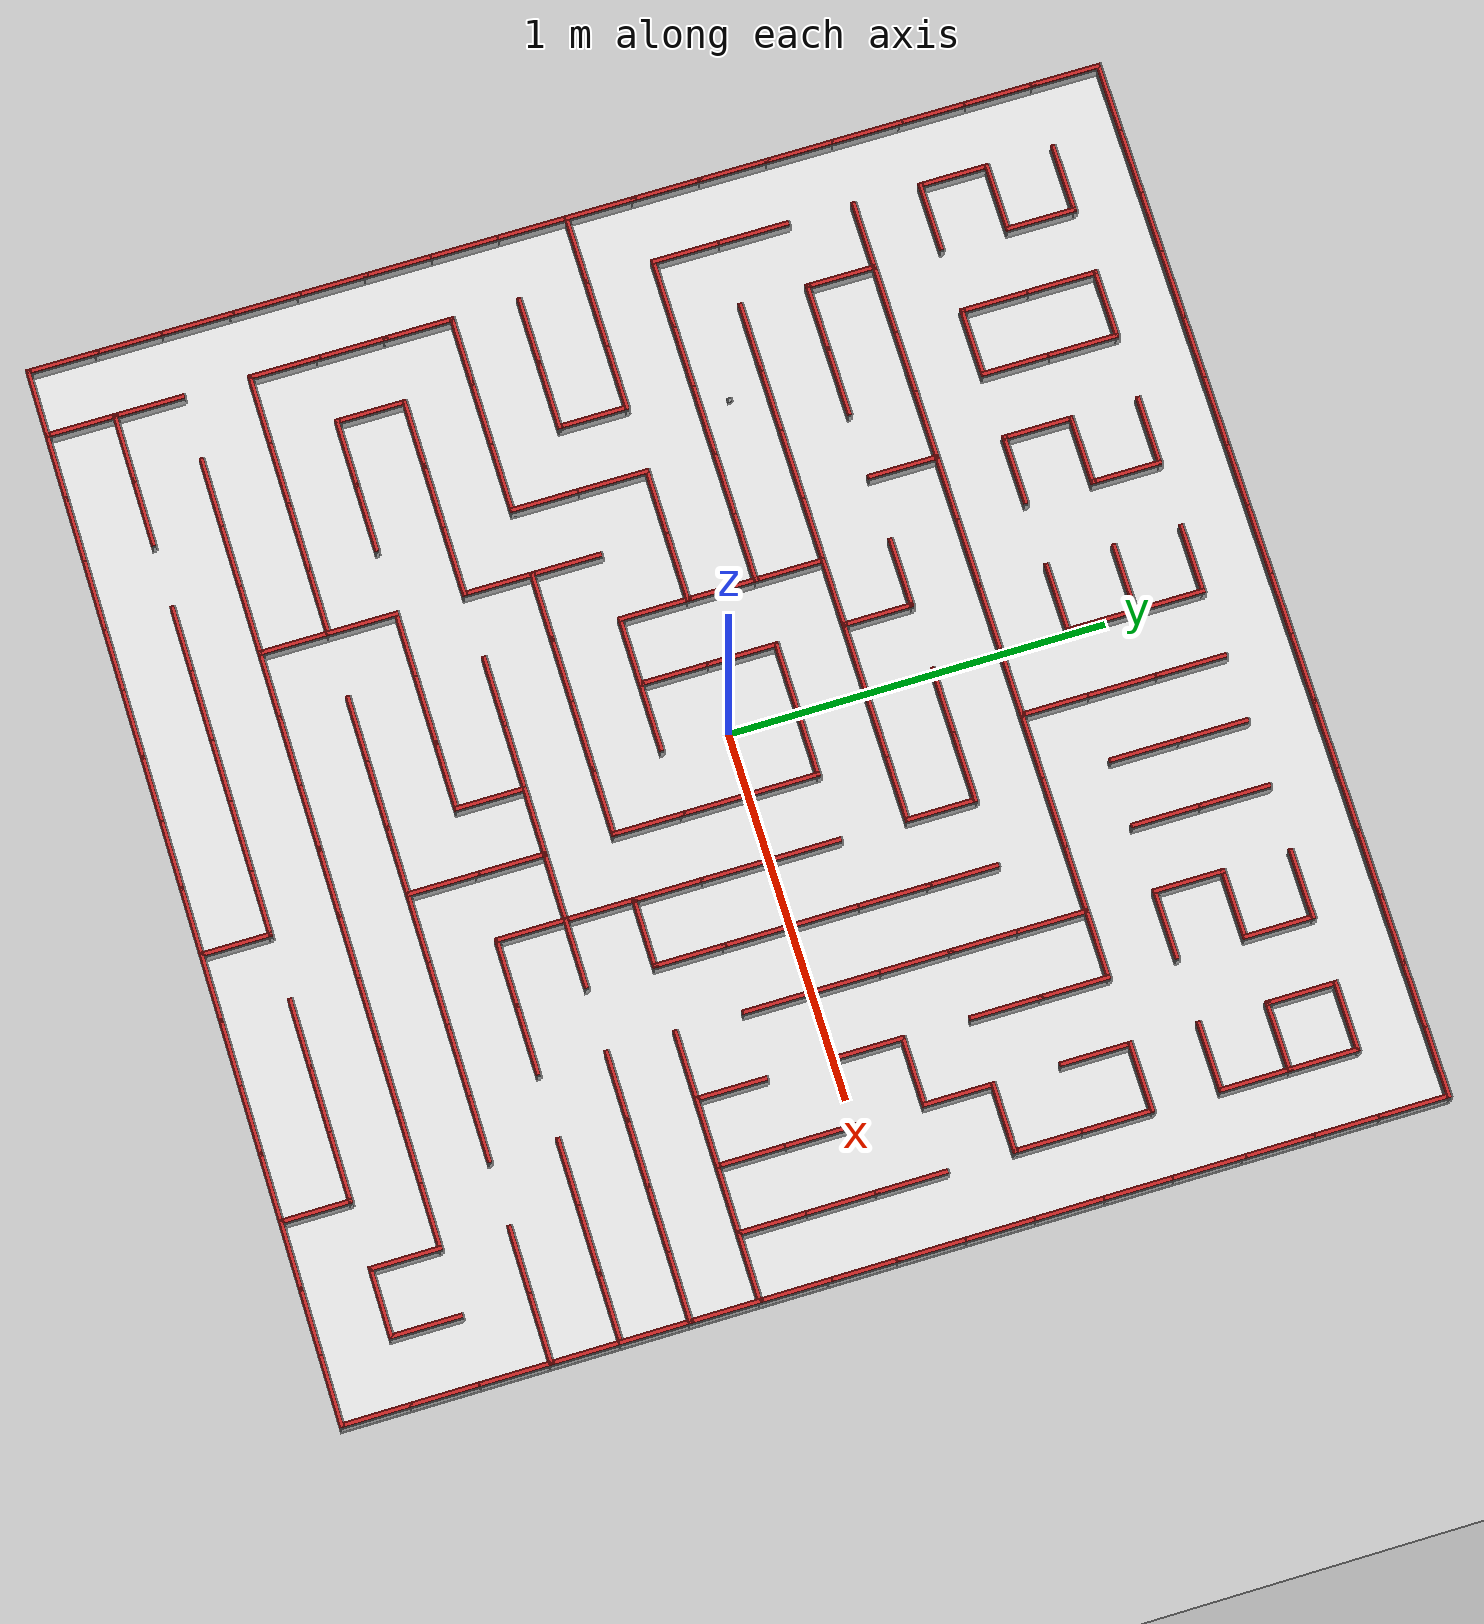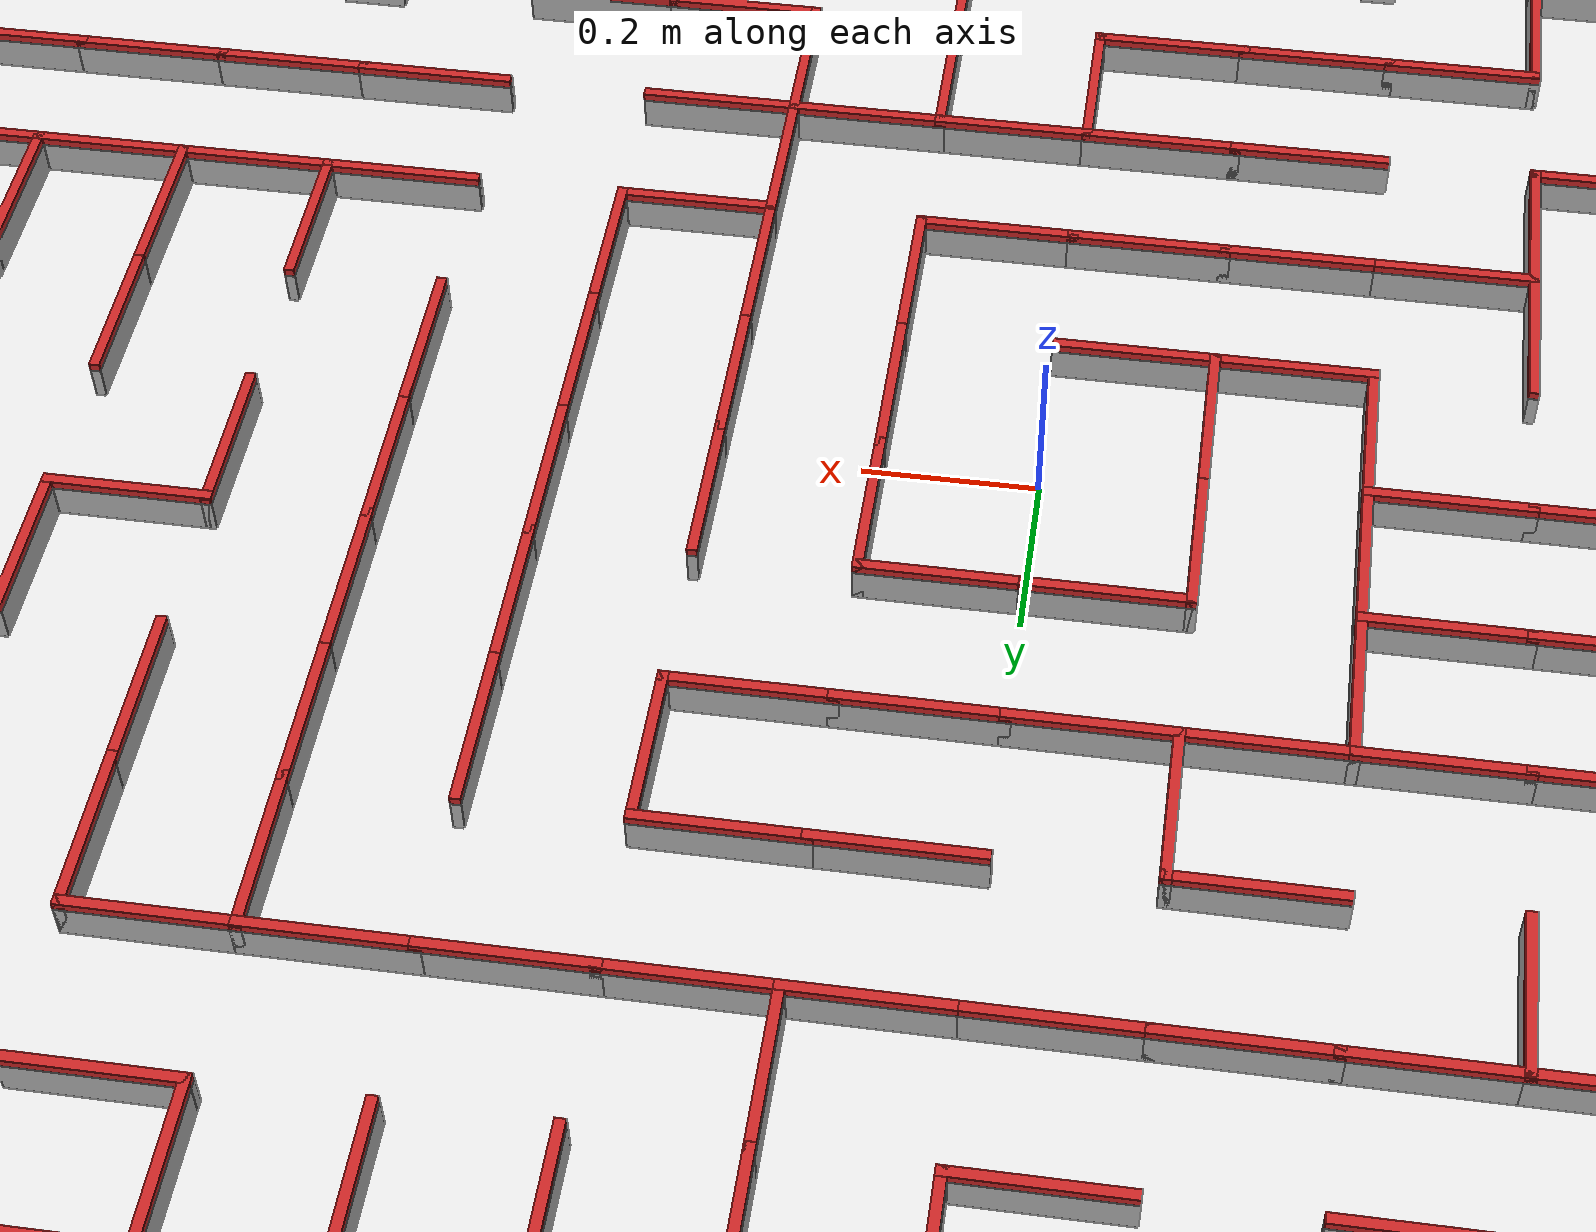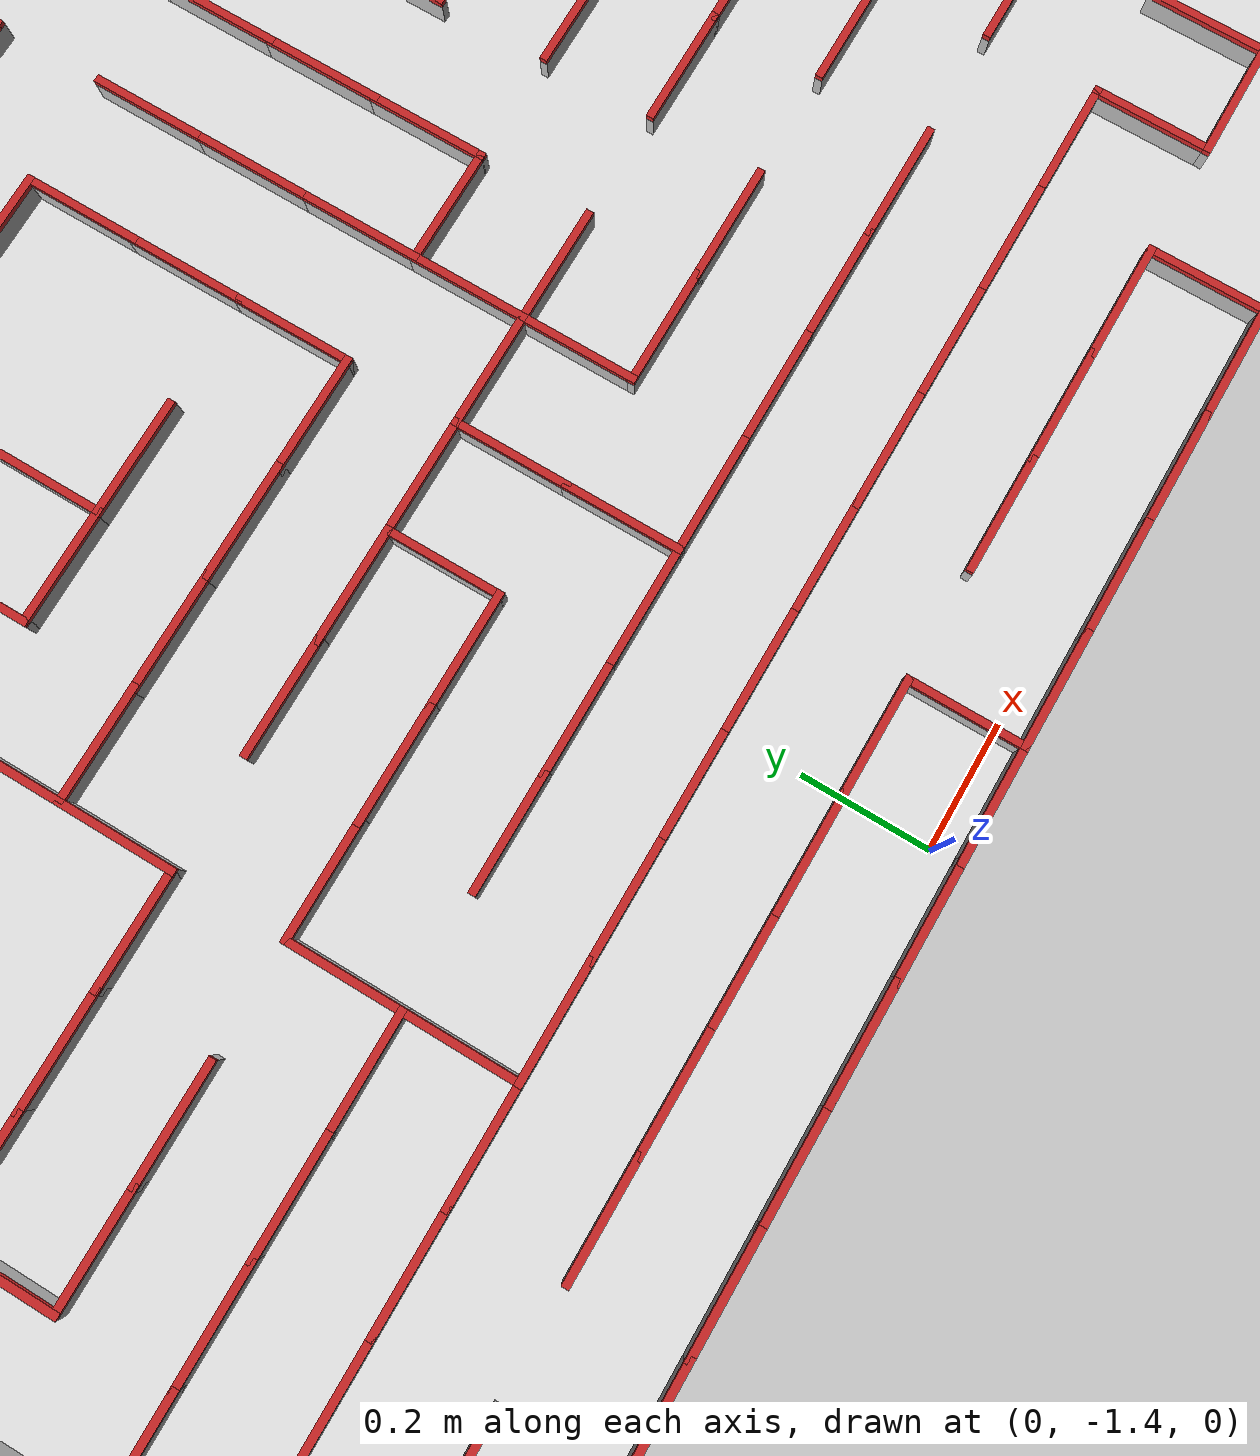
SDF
<sdf version="1.6">
 <world name="default">
  <model name="ground_plane">
   <static>1</static>
   <link name="link">
    <collision name="collision">
     <geometry><plane><normal>0 0 1</normal><size>100 100</size></plane></geometry>
     <surface><friction><ode><mu>100</mu><mu2>50</mu2></ode></friction></surface>
    </collision>
    <visual name="visual">
     <cast_shadows>0</cast_shadows>
     <geometry><plane><normal>0 0 1</normal><size>100 100</size></plane></geometry>
     <material>
      <script><uri>file://media/materials/scripts/gazebo.material</uri><name>Gazebo/Grey</name></script>
     </material>
    </visual>
   </link>
  </model>
  <light name="sun" type="directional">
   <cast_shadows>0</cast_shadows>
   <pose>0 0 10 0 -0 0</pose>
   <diffuse>0.8 0.8 0.8 1</diffuse>
   <specular>0.2 0.2 0.2 1</specular>
   <attenuation>
    <range>1000</range>
    <constant>0.9</constant>
    <linear>0.01</linear>
    <quadratic>0.001</quadratic>
   </attenuation>
   <direction>-0.5 0.1 -0.9</direction>
  </light>
  <physics default="0" name="default_physics" type="ode">
   <real_time_update_rate>0</real_time_update_rate>
   <max_step_size>0.001</max_step_size>
   <real_time_factor>1</real_time_factor>
  </physics>
  <gravity>0 0 -9.8</gravity>
  <magnetic_field>6e-06 2.3e-05 -4.2e-05</magnetic_field>
  <atmosphere type="adiabatic"/>
  <scene><ambient>0.4 0.4 0.4 1</ambient><background>0.7 0.7 0.7 1</background><shadows>1</shadows></scene>
  <spherical_coordinates>
   <surface_model>EARTH_WGS84</surface_model>
   <latitude_deg>0</latitude_deg>
   <longitude_deg>0</longitude_deg>
   <elevation>0</elevation>
   <heading_deg>0</heading_deg>
  </spherical_coordinates>
  <model name="my_maze">
   <link name="base">
    <inertial>
     <mass>1</mass>
     <inertia>
      <ixx>1.39394</ixx>
      <ixy>0</ixy>
      <ixz>0</ixz>
      <iyy>0.696972</iyy>
      <iyz>0</iyz>
      <izz>0.696973</izz>
     </inertia>
     <pose>0 0 0.05 0 -0 0</pose>
    </inertial>
    <visual name="visual">
     <pose>0 0 0.0025 0 -0 0</pose>
     <geometry><box><size>2.892 2.892 0.005</size></box></geometry>
     <material>
      <script><uri>file://media/materials/scripts/gazebo.material</uri><name>Gazebo/White</name></script>
     </material>
    </visual>
    <collision name="collision">
     <pose>0 0 0.0025 0 -0 0</pose>
     <geometry><box><size>2.892 2.892 0.005</size></box></geometry>
     <surface><friction><ode><mu>1000</mu><mu2>1000</mu2></ode></friction></surface>
    </collision>
    <visual name="paint_v_0_0_N">
     <pose>-1.35 1.44 0.05 0 -0 0</pose>
     <geometry><box><size>0.192 0.012 0.01</size></box></geometry>
     <material>
      <script><name>Gazebo/Red</name><uri>file://media/materials/scripts/gazebo.material</uri></script>
     </material>
    </visual>
    <visual name="v_0_0_N">
     <pose>-1.35 1.44 0.025 0 -0 0</pose>
     <geometry><box><size>0.192 0.012 0.04</size></box></geometry>
    </visual>
    <collision name="p_0_0_N">
     <pose>-1.35 1.44 0.03 0 -0 0</pose>
     <geometry><box><size>0.192 0.012 0.05</size></box></geometry>
    </collision>
    <visual name="paint_v_0_1_N">
     <pose>-1.17 1.44 0.05 0 -0 0</pose>
     <geometry><box><size>0.192 0.012 0.01</size></box></geometry>
     <material>
      <script><name>Gazebo/Red</name><uri>file://media/materials/scripts/gazebo.material</uri></script>
     </material>
    </visual>
    <visual name="v_0_1_N">
     <pose>-1.17 1.44 0.025 0 -0 0</pose>
     <geometry><box><size>0.192 0.012 0.04</size></box></geometry>
    </visual>
    <collision name="p_0_1_N">
     <pose>-1.17 1.44 0.03 0 -0 0</pose>
     <geometry><box><size>0.192 0.012 0.05</size></box></geometry>
    </collision>
    <visual name="paint_v_0_2_N">
     <pose>-0.99 1.44 0.05 0 -0 0</pose>
     <geometry><box><size>0.192 0.012 0.01</size></box></geometry>
     <material>
      <script><name>Gazebo/Red</name><uri>file://media/materials/scripts/gazebo.material</uri></script>
     </material>
    </visual>
    <visual name="v_0_2_N">
     <pose>-0.99 1.44 0.025 0 -0 0</pose>
     <geometry><box><size>0.192 0.012 0.04</size></box></geometry>
    </visual>
    <collision name="p_0_2_N">
     <pose>-0.99 1.44 0.03 0 -0 0</pose>
     <geometry><box><size>0.192 0.012 0.05</size></box></geometry>
    </collision>
    <visual name="paint_v_0_3_N">
     <pose>-0.81 1.44 0.05 0 -0 0</pose>
     <geometry><box><size>0.192 0.012 0.01</size></box></geometry>
     <material>
      <script><name>Gazebo/Red</name><uri>file://media/materials/scripts/gazebo.material</uri></script>
     </material>
    </visual>
    <visual name="v_0_3_N">
     <pose>-0.81 1.44 0.025 0 -0 0</pose>
     <geometry><box><size>0.192 0.012 0.04</size></box></geometry>
    </visual>
    <collision name="p_0_3_N">
     <pose>-0.81 1.44 0.03 0 -0 0</pose>
     <geometry><box><size>0.192 0.012 0.05</size></box></geometry>
    </collision>
    <visual name="paint_v_0_4_N">
     <pose>-0.63 1.44 0.05 0 -0 0</pose>
     <geometry><box><size>0.192 0.012 0.01</size></box></geometry>
     <material>
      <script><name>Gazebo/Red</name><uri>file://media/materials/scripts/gazebo.material</uri></script>
     </material>
    </visual>
    <visual name="v_0_4_N">
     <pose>-0.63 1.44 0.025 0 -0 0</pose>
     <geometry><box><size>0.192 0.012 0.04</size></box></geometry>
    </visual>
    <collision name="p_0_4_N">
     <pose>-0.63 1.44 0.03 0 -0 0</pose>
     <geometry><box><size>0.192 0.012 0.05</size></box></geometry>
    </collision>
    <visual name="paint_v_0_5_N">
     <pose>-0.45 1.44 0.05 0 -0 0</pose>
     <geometry><box><size>0.192 0.012 0.01</size></box></geometry>
     <material>
      <script><name>Gazebo/Red</name><uri>file://media/materials/scripts/gazebo.material</uri></script>
     </material>
    </visual>
    <visual name="v_0_5_N">
     <pose>-0.45 1.44 0.025 0 -0 0</pose>
     <geometry><box><size>0.192 0.012 0.04</size></box></geometry>
    </visual>
    <collision name="p_0_5_N">
     <pose>-0.45 1.44 0.03 0 -0 0</pose>
     <geometry><box><size>0.192 0.012 0.05</size></box></geometry>
    </collision>
    <visual name="paint_v_0_6_N">
     <pose>-0.27 1.44 0.05 0 -0 0</pose>
     <geometry><box><size>0.192 0.012 0.01</size></box></geometry>
     <material>
      <script><name>Gazebo/Red</name><uri>file://media/materials/scripts/gazebo.material</uri></script>
     </material>
    </visual>
    <visual name="v_0_6_N">
     <pose>-0.27 1.44 0.025 0 -0 0</pose>
     <geometry><box><size>0.192 0.012 0.04</size></box></geometry>
    </visual>
    <collision name="p_0_6_N">
     <pose>-0.27 1.44 0.03 0 -0 0</pose>
     <geometry><box><size>0.192 0.012 0.05</size></box></geometry>
    </collision>
    <visual name="paint_v_0_7_N">
     <pose>-0.09 1.44 0.05 0 -0 0</pose>
     <geometry><box><size>0.192 0.012 0.01</size></box></geometry>
     <material>
      <script><name>Gazebo/Red</name><uri>file://media/materials/scripts/gazebo.material</uri></script>
     </material>
    </visual>
    <visual name="v_0_7_N">
     <pose>-0.09 1.44 0.025 0 -0 0</pose>
     <geometry><box><size>0.192 0.012 0.04</size></box></geometry>
    </visual>
    <collision name="p_0_7_N">
     <pose>-0.09 1.44 0.03 0 -0 0</pose>
     <geometry><box><size>0.192 0.012 0.05</size></box></geometry>
    </collision>
    <visual name="paint_v_0_8_N">
     <pose>0.09 1.44 0.05 0 -0 0</pose>
     <geometry><box><size>0.192 0.012 0.01</size></box></geometry>
     <material>
      <script><name>Gazebo/Red</name><uri>file://media/materials/scripts/gazebo.material</uri></script>
     </material>
    </visual>
    <visual name="v_0_8_N">
     <pose>0.09 1.44 0.025 0 -0 0</pose>
     <geometry><box><size>0.192 0.012 0.04</size></box></geometry>
    </visual>
    <collision name="p_0_8_N">
     <pose>0.09 1.44 0.03 0 -0 0</pose>
     <geometry><box><size>0.192 0.012 0.05</size></box></geometry>
    </collision>
    <visual name="paint_v_0_9_N">
     <pose>0.27 1.44 0.05 0 -0 0</pose>
     <geometry><box><size>0.192 0.012 0.01</size></box></geometry>
     <material>
      <script><name>Gazebo/Red</name><uri>file://media/materials/scripts/gazebo.material</uri></script>
     </material>
    </visual>
    <visual name="v_0_9_N">
     <pose>0.27 1.44 0.025 0 -0 0</pose>
     <geometry><box><size>0.192 0.012 0.04</size></box></geometry>
    </visual>
    <collision name="p_0_9_N">
     <pose>0.27 1.44 0.03 0 -0 0</pose>
     <geometry><box><size>0.192 0.012 0.05</size></box></geometry>
    </collision>
    <visual name="paint_v_0_10_N">
     <pose>0.45 1.44 0.05 0 -0 0</pose>
     <geometry><box><size>0.192 0.012 0.01</size></box></geometry>
     <material>
      <script><name>Gazebo/Red</name><uri>file://media/materials/scripts/gazebo.material</uri></script>
     </material>
    </visual>
    <visual name="v_0_10_N">
     <pose>0.45 1.44 0.025 0 -0 0</pose>
     <geometry><box><size>0.192 0.012 0.04</size></box></geometry>
    </visual>
    <collision name="p_0_10_N">
     <pose>0.45 1.44 0.03 0 -0 0</pose>
     <geometry><box><size>0.192 0.012 0.05</size></box></geometry>
    </collision>
    <visual name="paint_v_0_11_N">
     <pose>0.63 1.44 0.05 0 -0 0</pose>
     <geometry><box><size>0.192 0.012 0.01</size></box></geometry>
     <material>
      <script><name>Gazebo/Red</name><uri>file://media/materials/scripts/gazebo.material</uri></script>
     </material>
    </visual>
    <visual name="v_0_11_N">
     <pose>0.63 1.44 0.025 0 -0 0</pose>
     <geometry><box><size>0.192 0.012 0.04</size></box></geometry>
    </visual>
    <collision name="p_0_11_N">
     <pose>0.63 1.44 0.03 0 -0 0</pose>
     <geometry><box><size>0.192 0.012 0.05</size></box></geometry>
    </collision>
    <visual name="paint_v_0_12_N">
     <pose>0.81 1.44 0.05 0 -0 0</pose>
     <geometry><box><size>0.192 0.012 0.01</size></box></geometry>
     <material>
      <script><name>Gazebo/Red</name><uri>file://media/materials/scripts/gazebo.material</uri></script>
     </material>
    </visual>
    <visual name="v_0_12_N">
     <pose>0.81 1.44 0.025 0 -0 0</pose>
     <geometry><box><size>0.192 0.012 0.04</size></box></geometry>
    </visual>
    <collision name="p_0_12_N">
     <pose>0.81 1.44 0.03 0 -0 0</pose>
     <geometry><box><size>0.192 0.012 0.05</size></box></geometry>
    </collision>
    <visual name="paint_v_0_13_N">
     <pose>0.99 1.44 0.05 0 -0 0</pose>
     <geometry><box><size>0.192 0.012 0.01</size></box></geometry>
     <material>
      <script><name>Gazebo/Red</name><uri>file://media/materials/scripts/gazebo.material</uri></script>
     </material>
    </visual>
    <visual name="v_0_13_N">
     <pose>0.99 1.44 0.025 0 -0 0</pose>
     <geometry><box><size>0.192 0.012 0.04</size></box></geometry>
    </visual>
    <collision name="p_0_13_N">
     <pose>0.99 1.44 0.03 0 -0 0</pose>
     <geometry><box><size>0.192 0.012 0.05</size></box></geometry>
    </collision>
    <visual name="paint_v_0_14_N">
     <pose>1.17 1.44 0.05 0 -0 0</pose>
     <geometry><box><size>0.192 0.012 0.01</size></box></geometry>
     <material>
      <script><name>Gazebo/Red</name><uri>file://media/materials/scripts/gazebo.material</uri></script>
     </material>
    </visual>
    <visual name="v_0_14_N">
     <pose>1.17 1.44 0.025 0 -0 0</pose>
     <geometry><box><size>0.192 0.012 0.04</size></box></geometry>
    </visual>
    <collision name="p_0_14_N">
     <pose>1.17 1.44 0.03 0 -0 0</pose>
     <geometry><box><size>0.192 0.012 0.05</size></box></geometry>
    </collision>
    <visual name="paint_v_0_15_N">
     <pose>1.35 1.44 0.05 0 -0 0</pose>
     <geometry><box><size>0.192 0.012 0.01</size></box></geometry>
     <material>
      <script><name>Gazebo/Red</name><uri>file://media/materials/scripts/gazebo.material</uri></script>
     </material>
    </visual>
    <visual name="v_0_15_N">
     <pose>1.35 1.44 0.025 0 -0 0</pose>
     <geometry><box><size>0.192 0.012 0.04</size></box></geometry>
    </visual>
    <collision name="p_0_15_N">
     <pose>1.35 1.44 0.03 0 -0 0</pose>
     <geometry><box><size>0.192 0.012 0.05</size></box></geometry>
    </collision>
    <visual name="paint_v_0_15_E">
     <pose>1.44 1.35 0.05 0 -0 1.5708</pose>
     <geometry><box><size>0.192 0.012 0.01</size></box></geometry>
     <material>
      <script><name>Gazebo/Red</name><uri>file://media/materials/scripts/gazebo.material</uri></script>
     </material>
    </visual>
    <visual name="v_0_15_E">
     <pose>1.44 1.35 0.025 0 -0 1.5708</pose>
     <geometry><box><size>0.192 0.012 0.04</size></box></geometry>
    </visual>
    <collision name="p_0_15_E">
     <pose>1.44 1.35 0.03 0 -0 1.5708</pose>
     <geometry><box><size>0.192 0.012 0.05</size></box></geometry>
    </collision>
    <visual name="paint_v_1_15_E">
     <pose>1.44 1.17 0.05 0 -0 1.5708</pose>
     <geometry><box><size>0.192 0.012 0.01</size></box></geometry>
     <material>
      <script><name>Gazebo/Red</name><uri>file://media/materials/scripts/gazebo.material</uri></script>
     </material>
    </visual>
    <visual name="v_1_15_E">
     <pose>1.44 1.17 0.025 0 -0 1.5708</pose>
     <geometry><box><size>0.192 0.012 0.04</size></box></geometry>
    </visual>
    <collision name="p_1_15_E">
     <pose>1.44 1.17 0.03 0 -0 1.5708</pose>
     <geometry><box><size>0.192 0.012 0.05</size></box></geometry>
    </collision>
    <visual name="paint_v_2_15_E">
     <pose>1.44 0.99 0.05 0 -0 1.5708</pose>
     <geometry><box><size>0.192 0.012 0.01</size></box></geometry>
     <material>
      <script><name>Gazebo/Red</name><uri>file://media/materials/scripts/gazebo.material</uri></script>
     </material>
    </visual>
    <visual name="v_2_15_E">
     <pose>1.44 0.99 0.025 0 -0 1.5708</pose>
     <geometry><box><size>0.192 0.012 0.04</size></box></geometry>
    </visual>
    <collision name="p_2_15_E">
     <pose>1.44 0.99 0.03 0 -0 1.5708</pose>
     <geometry><box><size>0.192 0.012 0.05</size></box></geometry>
    </collision>
    <visual name="paint_v_3_15_E">
     <pose>1.44 0.81 0.05 0 -0 1.5708</pose>
     <geometry><box><size>0.192 0.012 0.01</size></box></geometry>
     <material>
      <script><name>Gazebo/Red</name><uri>file://media/materials/scripts/gazebo.material</uri></script>
     </material>
    </visual>
    <visual name="v_3_15_E">
     <pose>1.44 0.81 0.025 0 -0 1.5708</pose>
     <geometry><box><size>0.192 0.012 0.04</size></box></geometry>
    </visual>
    <collision name="p_3_15_E">
     <pose>1.44 0.81 0.03 0 -0 1.5708</pose>
     <geometry><box><size>0.192 0.012 0.05</size></box></geometry>
    </collision>
    <visual name="paint_v_4_15_E">
     <pose>1.44 0.63 0.05 0 -0 1.5708</pose>
     <geometry><box><size>0.192 0.012 0.01</size></box></geometry>
     <material>
      <script><name>Gazebo/Red</name><uri>file://media/materials/scripts/gazebo.material</uri></script>
     </material>
    </visual>
    <visual name="v_4_15_E">
     <pose>1.44 0.63 0.025 0 -0 1.5708</pose>
     <geometry><box><size>0.192 0.012 0.04</size></box></geometry>
    </visual>
    <collision name="p_4_15_E">
     <pose>1.44 0.63 0.03 0 -0 1.5708</pose>
     <geometry><box><size>0.192 0.012 0.05</size></box></geometry>
    </collision>
    <visual name="paint_v_5_15_E">
     <pose>1.44 0.45 0.05 0 -0 1.5708</pose>
     <geometry><box><size>0.192 0.012 0.01</size></box></geometry>
     <material>
      <script><name>Gazebo/Red</name><uri>file://media/materials/scripts/gazebo.material</uri></script>
     </material>
    </visual>
    <visual name="v_5_15_E">
     <pose>1.44 0.45 0.025 0 -0 1.5708</pose>
     <geometry><box><size>0.192 0.012 0.04</size></box></geometry>
    </visual>
    <collision name="p_5_15_E">
     <pose>1.44 0.45 0.03 0 -0 1.5708</pose>
     <geometry><box><size>0.192 0.012 0.05</size></box></geometry>
    </collision>
    <visual name="paint_v_6_15_E">
     <pose>1.44 0.27 0.05 0 -0 1.5708</pose>
     <geometry><box><size>0.192 0.012 0.01</size></box></geometry>
     <material>
      <script><name>Gazebo/Red</name><uri>file://media/materials/scripts/gazebo.material</uri></script>
     </material>
    </visual>
    <visual name="v_6_15_E">
     <pose>1.44 0.27 0.025 0 -0 1.5708</pose>
     <geometry><box><size>0.192 0.012 0.04</size></box></geometry>
    </visual>
    <collision name="p_6_15_E">
     <pose>1.44 0.27 0.03 0 -0 1.5708</pose>
     <geometry><box><size>0.192 0.012 0.05</size></box></geometry>
    </collision>
    <visual name="paint_v_7_15_E">
     <pose>1.44 0.09 0.05 0 -0 1.5708</pose>
     <geometry><box><size>0.192 0.012 0.01</size></box></geometry>
     <material>
      <script><name>Gazebo/Red</name><uri>file://media/materials/scripts/gazebo.material</uri></script>
     </material>
    </visual>
    <visual name="v_7_15_E">
     <pose>1.44 0.09 0.025 0 -0 1.5708</pose>
     <geometry><box><size>0.192 0.012 0.04</size></box></geometry>
    </visual>
    <collision name="p_7_15_E">
     <pose>1.44 0.09 0.03 0 -0 1.5708</pose>
     <geometry><box><size>0.192 0.012 0.05</size></box></geometry>
    </collision>
    <visual name="paint_v_8_15_E">
     <pose>1.44 -0.09 0.05 0 -0 1.5708</pose>
     <geometry><box><size>0.192 0.012 0.01</size></box></geometry>
     <material>
      <script><name>Gazebo/Red</name><uri>file://media/materials/scripts/gazebo.material</uri></script>
     </material>
    </visual>
    <visual name="v_8_15_E">
     <pose>1.44 -0.09 0.025 0 -0 1.5708</pose>
     <geometry><box><size>0.192 0.012 0.04</size></box></geometry>
    </visual>
    <collision name="p_8_15_E">
     <pose>1.44 -0.09 0.03 0 -0 1.5708</pose>
     <geometry><box><size>0.192 0.012 0.05</size></box></geometry>
    </collision>
    <visual name="paint_v_9_15_E">
     <pose>1.44 -0.27 0.05 0 -0 1.5708</pose>
     <geometry><box><size>0.192 0.012 0.01</size></box></geometry>
     <material>
      <script><name>Gazebo/Red</name><uri>file://media/materials/scripts/gazebo.material</uri></script>
     </material>
    </visual>
    <visual name="v_9_15_E">
     <pose>1.44 -0.27 0.025 0 -0 1.5708</pose>
     <geometry><box><size>0.192 0.012 0.04</size></box></geometry>
    </visual>
    <collision name="p_9_15_E">
     <pose>1.44 -0.27 0.03 0 -0 1.5708</pose>
     <geometry><box><size>0.192 0.012 0.05</size></box></geometry>
    </collision>
    <visual name="paint_v_10_15_E">
     <pose>1.44 -0.45 0.05 0 -0 1.5708</pose>
     <geometry><box><size>0.192 0.012 0.01</size></box></geometry>
     <material>
      <script><name>Gazebo/Red</name><uri>file://media/materials/scripts/gazebo.material</uri></script>
     </material>
    </visual>
    <visual name="v_10_15_E">
     <pose>1.44 -0.45 0.025 0 -0 1.5708</pose>
     <geometry><box><size>0.192 0.012 0.04</size></box></geometry>
    </visual>
    <collision name="p_10_15_E">
     <pose>1.44 -0.45 0.03 0 -0 1.5708</pose>
     <geometry><box><size>0.192 0.012 0.05</size></box></geometry>
    </collision>
    <visual name="paint_v_11_15_E">
     <pose>1.44 -0.63 0.05 0 -0 1.5708</pose>
     <geometry><box><size>0.192 0.012 0.01</size></box></geometry>
     <material>
      <script><name>Gazebo/Red</name><uri>file://media/materials/scripts/gazebo.material</uri></script>
     </material>
    </visual>
    <visual name="v_11_15_E">
     <pose>1.44 -0.63 0.025 0 -0 1.5708</pose>
     <geometry><box><size>0.192 0.012 0.04</size></box></geometry>
    </visual>
    <collision name="p_11_15_E">
     <pose>1.44 -0.63 0.03 0 -0 1.5708</pose>
     <geometry><box><size>0.192 0.012 0.05</size></box></geometry>
    </collision>
    <visual name="paint_v_12_15_E">
     <pose>1.44 -0.81 0.05 0 -0 1.5708</pose>
     <geometry><box><size>0.192 0.012 0.01</size></box></geometry>
     <material>
      <script><name>Gazebo/Red</name><uri>file://media/materials/scripts/gazebo.material</uri></script>
     </material>
    </visual>
    <visual name="v_12_15_E">
     <pose>1.44 -0.81 0.025 0 -0 1.5708</pose>
     <geometry><box><size>0.192 0.012 0.04</size></box></geometry>
    </visual>
    <collision name="p_12_15_E">
     <pose>1.44 -0.81 0.03 0 -0 1.5708</pose>
     <geometry><box><size>0.192 0.012 0.05</size></box></geometry>
    </collision>
    <visual name="paint_v_13_15_E">
     <pose>1.44 -0.99 0.05 0 -0 1.5708</pose>
     <geometry><box><size>0.192 0.012 0.01</size></box></geometry>
     <material>
      <script><name>Gazebo/Red</name><uri>file://media/materials/scripts/gazebo.material</uri></script>
     </material>
    </visual>
    <visual name="v_13_15_E">
     <pose>1.44 -0.99 0.025 0 -0 1.5708</pose>
     <geometry><box><size>0.192 0.012 0.04</size></box></geometry>
    </visual>
    <collision name="p_13_15_E">
     <pose>1.44 -0.99 0.03 0 -0 1.5708</pose>
     <geometry><box><size>0.192 0.012 0.05</size></box></geometry>
    </collision>
    <visual name="paint_v_14_15_E">
     <pose>1.44 -1.17 0.05 0 -0 1.5708</pose>
     <geometry><box><size>0.192 0.012 0.01</size></box></geometry>
     <material>
      <script><name>Gazebo/Red</name><uri>file://media/materials/scripts/gazebo.material</uri></script>
     </material>
    </visual>
    <visual name="v_14_15_E">
     <pose>1.44 -1.17 0.025 0 -0 1.5708</pose>
     <geometry><box><size>0.192 0.012 0.04</size></box></geometry>
    </visual>
    <collision name="p_14_15_E">
     <pose>1.44 -1.17 0.03 0 -0 1.5708</pose>
     <geometry><box><size>0.192 0.012 0.05</size></box></geometry>
    </collision>
    <visual name="paint_v_15_15_E">
     <pose>1.44 -1.35 0.05 0 -0 1.5708</pose>
     <geometry><box><size>0.192 0.012 0.01</size></box></geometry>
     <material>
      <script><name>Gazebo/Red</name><uri>file://media/materials/scripts/gazebo.material</uri></script>
     </material>
    </visual>
    <visual name="v_15_15_E">
     <pose>1.44 -1.35 0.025 0 -0 1.5708</pose>
     <geometry><box><size>0.192 0.012 0.04</size></box></geometry>
    </visual>
    <collision name="p_15_15_E">
     <pose>1.44 -1.35 0.03 0 -0 1.5708</pose>
     <geometry><box><size>0.192 0.012 0.05</size></box></geometry>
    </collision>
    <visual name="paint_v_0_0_W">
     <pose>-1.44 1.35 0.05 0 -0 1.5708</pose>
     <geometry><box><size>0.192 0.012 0.01</size></box></geometry>
     <material>
      <script><name>Gazebo/Red</name><uri>file://media/materials/scripts/gazebo.material</uri></script>
     </material>
    </visual>
    <visual name="v_0_0_W">
     <pose>-1.44 1.35 0.025 0 -0 1.5708</pose>
     <geometry><box><size>0.192 0.012 0.04</size></box></geometry>
    </visual>
    <collision name="p_0_0_W">
     <pose>-1.44 1.35 0.03 0 -0 1.5708</pose>
     <geometry><box><size>0.192 0.012 0.05</size></box></geometry>
    </collision>
    <visual name="paint_v_0_1_S">
     <pose>-1.17 1.26 0.05 0 -0 0</pose>
     <geometry><box><size>0.192 0.012 0.01</size></box></geometry>
     <material>
      <script><name>Gazebo/Red</name><uri>file://media/materials/scripts/gazebo.material</uri></script>
     </material>
    </visual>
    <visual name="v_0_1_S">
     <pose>-1.17 1.26 0.025 0 -0 0</pose>
     <geometry><box><size>0.192 0.012 0.04</size></box></geometry>
    </visual>
    <collision name="p_0_1_S">
     <pose>-1.17 1.26 0.03 0 -0 0</pose>
     <geometry><box><size>0.192 0.012 0.05</size></box></geometry>
    </collision>
    <visual name="paint_v_0_3_S">
     <pose>-0.81 1.26 0.05 0 -0 0</pose>
     <geometry><box><size>0.192 0.012 0.01</size></box></geometry>
     <material>
      <script><name>Gazebo/Red</name><uri>file://media/materials/scripts/gazebo.material</uri></script>
     </material>
    </visual>
    <visual name="v_0_3_S">
     <pose>-0.81 1.26 0.025 0 -0 0</pose>
     <geometry><box><size>0.192 0.012 0.04</size></box></geometry>
    </visual>
    <collision name="p_0_3_S">
     <pose>-0.81 1.26 0.03 0 -0 0</pose>
     <geometry><box><size>0.192 0.012 0.05</size></box></geometry>
    </collision>
    <visual name="paint_v_0_5_S">
     <pose>-0.45 1.26 0.05 0 -0 0</pose>
     <geometry><box><size>0.192 0.012 0.01</size></box></geometry>
     <material>
      <script><name>Gazebo/Red</name><uri>file://media/materials/scripts/gazebo.material</uri></script>
     </material>
    </visual>
    <visual name="v_0_5_S">
     <pose>-0.45 1.26 0.025 0 -0 0</pose>
     <geometry><box><size>0.192 0.012 0.04</size></box></geometry>
    </visual>
    <collision name="p_0_5_S">
     <pose>-0.45 1.26 0.03 0 -0 0</pose>
     <geometry><box><size>0.192 0.012 0.05</size></box></geometry>
    </collision>
    <visual name="paint_v_0_7_S">
     <pose>-0.09 1.26 0.05 0 -0 0</pose>
     <geometry><box><size>0.192 0.012 0.01</size></box></geometry>
     <material>
      <script><name>Gazebo/Red</name><uri>file://media/materials/scripts/gazebo.material</uri></script>
     </material>
    </visual>
    <visual name="v_0_7_S">
     <pose>-0.09 1.26 0.025 0 -0 0</pose>
     <geometry><box><size>0.192 0.012 0.04</size></box></geometry>
    </visual>
    <collision name="p_0_7_S">
     <pose>-0.09 1.26 0.03 0 -0 0</pose>
     <geometry><box><size>0.192 0.012 0.05</size></box></geometry>
    </collision>
    <visual name="paint_v_0_12_S">
     <pose>0.81 1.26 0.05 0 -0 0</pose>
     <geometry><box><size>0.192 0.012 0.01</size></box></geometry>
     <material>
      <script><name>Gazebo/Red</name><uri>file://media/materials/scripts/gazebo.material</uri></script>
     </material>
    </visual>
    <visual name="v_0_12_S">
     <pose>0.81 1.26 0.025 0 -0 0</pose>
     <geometry><box><size>0.192 0.012 0.04</size></box></geometry>
    </visual>
    <collision name="p_0_12_S">
     <pose>0.81 1.26 0.03 0 -0 0</pose>
     <geometry><box><size>0.192 0.012 0.05</size></box></geometry>
    </collision>
    <visual name="paint_v_0_14_S">
     <pose>1.17 1.26 0.05 0 -0 0</pose>
     <geometry><box><size>0.192 0.012 0.01</size></box></geometry>
     <material>
      <script><name>Gazebo/Red</name><uri>file://media/materials/scripts/gazebo.material</uri></script>
     </material>
    </visual>
    <visual name="v_0_14_S">
     <pose>1.17 1.26 0.025 0 -0 0</pose>
     <geometry><box><size>0.192 0.012 0.04</size></box></geometry>
    </visual>
    <collision name="p_0_14_S">
     <pose>1.17 1.26 0.03 0 -0 0</pose>
     <geometry><box><size>0.192 0.012 0.05</size></box></geometry>
    </collision>
    <visual name="paint_v_1_0_W">
     <pose>-1.44 1.17 0.05 0 -0 1.5708</pose>
     <geometry><box><size>0.192 0.012 0.01</size></box></geometry>
     <material>
      <script><name>Gazebo/Red</name><uri>file://media/materials/scripts/gazebo.material</uri></script>
     </material>
    </visual>
    <visual name="v_1_0_W">
     <pose>-1.44 1.17 0.025 0 -0 1.5708</pose>
     <geometry><box><size>0.192 0.012 0.04</size></box></geometry>
    </visual>
    <collision name="p_1_0_W">
     <pose>-1.44 1.17 0.03 0 -0 1.5708</pose>
     <geometry><box><size>0.192 0.012 0.05</size></box></geometry>
    </collision>
    <visual name="paint_v_1_1_S">
     <pose>-1.17 1.08 0.05 0 -0 0</pose>
     <geometry><box><size>0.192 0.012 0.01</size></box></geometry>
     <material>
      <script><name>Gazebo/Red</name><uri>file://media/materials/scripts/gazebo.material</uri></script>
     </material>
    </visual>
    <visual name="v_1_1_S">
     <pose>-1.17 1.08 0.025 0 -0 0</pose>
     <geometry><box><size>0.192 0.012 0.04</size></box></geometry>
    </visual>
    <collision name="p_1_1_S">
     <pose>-1.17 1.08 0.03 0 -0 0</pose>
     <geometry><box><size>0.192 0.012 0.05</size></box></geometry>
    </collision>
    <visual name="paint_v_1_2_W">
     <pose>-1.08 1.17 0.05 0 -0 1.5708</pose>
     <geometry><box><size>0.192 0.012 0.01</size></box></geometry>
     <material>
      <script><name>Gazebo/Red</name><uri>file://media/materials/scripts/gazebo.material</uri></script>
     </material>
    </visual>
    <visual name="v_1_2_W">
     <pose>-1.08 1.17 0.025 0 -0 1.5708</pose>
     <geometry><box><size>0.192 0.012 0.04</size></box></geometry>
    </visual>
    <collision name="p_1_2_W">
     <pose>-1.08 1.17 0.03 0 -0 1.5708</pose>
     <geometry><box><size>0.192 0.012 0.05</size></box></geometry>
    </collision>
    <visual name="paint_v_1_3_W">
     <pose>-0.9 1.17 0.05 0 -0 1.5708</pose>
     <geometry><box><size>0.192 0.012 0.01</size></box></geometry>
     <material>
      <script><name>Gazebo/Red</name><uri>file://media/materials/scripts/gazebo.material</uri></script>
     </material>
    </visual>
    <visual name="v_1_3_W">
     <pose>-0.9 1.17 0.025 0 -0 1.5708</pose>
     <geometry><box><size>0.192 0.012 0.04</size></box></geometry>
    </visual>
    <collision name="p_1_3_W">
     <pose>-0.9 1.17 0.03 0 -0 1.5708</pose>
     <geometry><box><size>0.192 0.012 0.05</size></box></geometry>
    </collision>
    <visual name="paint_v_1_4_W">
     <pose>-0.72 1.17 0.05 0 -0 1.5708</pose>
     <geometry><box><size>0.192 0.012 0.01</size></box></geometry>
     <material>
      <script><name>Gazebo/Red</name><uri>file://media/materials/scripts/gazebo.material</uri></script>
     </material>
    </visual>
    <visual name="v_1_4_W">
     <pose>-0.72 1.17 0.025 0 -0 1.5708</pose>
     <geometry><box><size>0.192 0.012 0.04</size></box></geometry>
    </visual>
    <collision name="p_1_4_W">
     <pose>-0.72 1.17 0.03 0 -0 1.5708</pose>
     <geometry><box><size>0.192 0.012 0.05</size></box></geometry>
    </collision>
    <visual name="paint_v_1_5_S">
     <pose>-0.45 1.08 0.05 0 -0 0</pose>
     <geometry><box><size>0.192 0.012 0.01</size></box></geometry>
     <material>
      <script><name>Gazebo/Red</name><uri>file://media/materials/scripts/gazebo.material</uri></script>
     </material>
    </visual>
    <visual name="v_1_5_S">
     <pose>-0.45 1.08 0.025 0 -0 0</pose>
     <geometry><box><size>0.192 0.012 0.04</size></box></geometry>
    </visual>
    <collision name="p_1_5_S">
     <pose>-0.45 1.08 0.03 0 -0 0</pose>
     <geometry><box><size>0.192 0.012 0.05</size></box></geometry>
    </collision>
    <visual name="paint_v_1_6_W">
     <pose>-0.36 1.17 0.05 0 -0 1.5708</pose>
     <geometry><box><size>0.192 0.012 0.01</size></box></geometry>
     <material>
      <script><name>Gazebo/Red</name><uri>file://media/materials/scripts/gazebo.material</uri></script>
     </material>
    </visual>
    <visual name="v_1_6_W">
     <pose>-0.36 1.17 0.025 0 -0 1.5708</pose>
     <geometry><box><size>0.192 0.012 0.04</size></box></geometry>
    </visual>
    <collision name="p_1_6_W">
     <pose>-0.36 1.17 0.03 0 -0 1.5708</pose>
     <geometry><box><size>0.192 0.012 0.05</size></box></geometry>
    </collision>
    <visual name="paint_v_1_7_S">
     <pose>-0.09 1.08 0.05 0 -0 0</pose>
     <geometry><box><size>0.192 0.012 0.01</size></box></geometry>
     <material>
      <script><name>Gazebo/Red</name><uri>file://media/materials/scripts/gazebo.material</uri></script>
     </material>
    </visual>
    <visual name="v_1_7_S">
     <pose>-0.09 1.08 0.025 0 -0 0</pose>
     <geometry><box><size>0.192 0.012 0.04</size></box></geometry>
    </visual>
    <collision name="p_1_7_S">
     <pose>-0.09 1.08 0.03 0 -0 0</pose>
     <geometry><box><size>0.192 0.012 0.05</size></box></geometry>
    </collision>
    <visual name="paint_v_1_8_W">
     <pose>-0.0 1.17 0.05 0 -0 1.5708</pose>
     <geometry><box><size>0.192 0.012 0.01</size></box></geometry>
     <material>
      <script><name>Gazebo/Red</name><uri>file://media/materials/scripts/gazebo.material</uri></script>
     </material>
    </visual>
    <visual name="v_1_8_W">
     <pose>-0.0 1.17 0.025 0 -0 1.5708</pose>
     <geometry><box><size>0.192 0.012 0.04</size></box></geometry>
    </visual>
    <collision name="p_1_8_W">
     <pose>-0.0 1.17 0.03 0 -0 1.5708</pose>
     <geometry><box><size>0.192 0.012 0.05</size></box></geometry>
    </collision>
    <visual name="paint_v_1_9_W">
     <pose>0.18 1.17 0.05 0 -0 1.5708</pose>
     <geometry><box><size>0.192 0.012 0.01</size></box></geometry>
     <material>
      <script><name>Gazebo/Red</name><uri>file://media/materials/scripts/gazebo.material</uri></script>
     </material>
    </visual>
    <visual name="v_1_9_W">
     <pose>0.18 1.17 0.025 0 -0 1.5708</pose>
     <geometry><box><size>0.192 0.012 0.04</size></box></geometry>
    </visual>
    <collision name="p_1_9_W">
     <pose>0.18 1.17 0.03 0 -0 1.5708</pose>
     <geometry><box><size>0.192 0.012 0.05</size></box></geometry>
    </collision>
    <visual name="paint_v_1_10_W">
     <pose>0.36 1.17 0.05 0 -0 1.5708</pose>
     <geometry><box><size>0.192 0.012 0.01</size></box></geometry>
     <material>
      <script><name>Gazebo/Red</name><uri>file://media/materials/scripts/gazebo.material</uri></script>
     </material>
    </visual>
    <visual name="v_1_10_W">
     <pose>0.36 1.17 0.025 0 -0 1.5708</pose>
     <geometry><box><size>0.192 0.012 0.04</size></box></geometry>
    </visual>
    <collision name="p_1_10_W">
     <pose>0.36 1.17 0.03 0 -0 1.5708</pose>
     <geometry><box><size>0.192 0.012 0.05</size></box></geometry>
    </collision>
    <visual name="paint_v_1_11_W">
     <pose>0.54 1.17 0.05 0 -0 1.5708</pose>
     <geometry><box><size>0.192 0.012 0.01</size></box></geometry>
     <material>
      <script><name>Gazebo/Red</name><uri>file://media/materials/scripts/gazebo.material</uri></script>
     </material>
    </visual>
    <visual name="v_1_11_W">
     <pose>0.54 1.17 0.025 0 -0 1.5708</pose>
     <geometry><box><size>0.192 0.012 0.04</size></box></geometry>
    </visual>
    <collision name="p_1_11_W">
     <pose>0.54 1.17 0.03 0 -0 1.5708</pose>
     <geometry><box><size>0.192 0.012 0.05</size></box></geometry>
    </collision>
    <visual name="paint_v_1_12_S">
     <pose>0.81 1.08 0.05 0 -0 0</pose>
     <geometry><box><size>0.192 0.012 0.01</size></box></geometry>
     <material>
      <script><name>Gazebo/Red</name><uri>file://media/materials/scripts/gazebo.material</uri></script>
     </material>
    </visual>
    <visual name="v_1_12_S">
     <pose>0.81 1.08 0.025 0 -0 0</pose>
     <geometry><box><size>0.192 0.012 0.04</size></box></geometry>
    </visual>
    <collision name="p_1_12_S">
     <pose>0.81 1.08 0.03 0 -0 0</pose>
     <geometry><box><size>0.192 0.012 0.05</size></box></geometry>
    </collision>
    <visual name="paint_v_1_13_W">
     <pose>0.9 1.17 0.05 0 -0 1.5708</pose>
     <geometry><box><size>0.192 0.012 0.01</size></box></geometry>
     <material>
      <script><name>Gazebo/Red</name><uri>file://media/materials/scripts/gazebo.material</uri></script>
     </material>
    </visual>
    <visual name="v_1_13_W">
     <pose>0.9 1.17 0.025 0 -0 1.5708</pose>
     <geometry><box><size>0.192 0.012 0.04</size></box></geometry>
    </visual>
    <collision name="p_1_13_W">
     <pose>0.9 1.17 0.03 0 -0 1.5708</pose>
     <geometry><box><size>0.192 0.012 0.05</size></box></geometry>
    </collision>
    <visual name="paint_v_1_14_W">
     <pose>1.08 1.17 0.05 0 -0 1.5708</pose>
     <geometry><box><size>0.192 0.012 0.01</size></box></geometry>
     <material>
      <script><name>Gazebo/Red</name><uri>file://media/materials/scripts/gazebo.material</uri></script>
     </material>
    </visual>
    <visual name="v_1_14_W">
     <pose>1.08 1.17 0.025 0 -0 1.5708</pose>
     <geometry><box><size>0.192 0.012 0.04</size></box></geometry>
    </visual>
    <collision name="p_1_14_W">
     <pose>1.08 1.17 0.03 0 -0 1.5708</pose>
     <geometry><box><size>0.192 0.012 0.05</size></box></geometry>
    </collision>
    <visual name="paint_v_1_14_S">
     <pose>1.17 1.08 0.05 0 -0 0</pose>
     <geometry><box><size>0.192 0.012 0.01</size></box></geometry>
     <material>
      <script><name>Gazebo/Red</name><uri>file://media/materials/scripts/gazebo.material</uri></script>
     </material>
    </visual>
    <visual name="v_1_14_S">
     <pose>1.17 1.08 0.025 0 -0 0</pose>
     <geometry><box><size>0.192 0.012 0.04</size></box></geometry>
    </visual>
    <collision name="p_1_14_S">
     <pose>1.17 1.08 0.03 0 -0 0</pose>
     <geometry><box><size>0.192 0.012 0.05</size></box></geometry>
    </collision>
    <visual name="paint_v_1_15_W">
     <pose>1.26 1.17 0.05 0 -0 1.5708</pose>
     <geometry><box><size>0.192 0.012 0.01</size></box></geometry>
     <material>
      <script><name>Gazebo/Red</name><uri>file://media/materials/scripts/gazebo.material</uri></script>
     </material>
    </visual>
    <visual name="v_1_15_W">
     <pose>1.26 1.17 0.025 0 -0 1.5708</pose>
     <geometry><box><size>0.192 0.012 0.04</size></box></geometry>
    </visual>
    <collision name="p_1_15_W">
     <pose>1.26 1.17 0.03 0 -0 1.5708</pose>
     <geometry><box><size>0.192 0.012 0.05</size></box></geometry>
    </collision>
    <visual name="paint_v_2_0_W">
     <pose>-1.44 0.99 0.05 0 -0 1.5708</pose>
     <geometry><box><size>0.192 0.012 0.01</size></box></geometry>
     <material>
      <script><name>Gazebo/Red</name><uri>file://media/materials/scripts/gazebo.material</uri></script>
     </material>
    </visual>
    <visual name="v_2_0_W">
     <pose>-1.44 0.99 0.025 0 -0 1.5708</pose>
     <geometry><box><size>0.192 0.012 0.04</size></box></geometry>
    </visual>
    <collision name="p_2_0_W">
     <pose>-1.44 0.99 0.03 0 -0 1.5708</pose>
     <geometry><box><size>0.192 0.012 0.05</size></box></geometry>
    </collision>
    <visual name="paint_v_2_1_W">
     <pose>-1.26 0.99 0.05 0 -0 1.5708</pose>
     <geometry><box><size>0.192 0.012 0.01</size></box></geometry>
     <material>
      <script><name>Gazebo/Red</name><uri>file://media/materials/scripts/gazebo.material</uri></script>
     </material>
    </visual>
    <visual name="v_2_1_W">
     <pose>-1.26 0.99 0.025 0 -0 1.5708</pose>
     <geometry><box><size>0.192 0.012 0.04</size></box></geometry>
    </visual>
    <collision name="p_2_1_W">
     <pose>-1.26 0.99 0.03 0 -0 1.5708</pose>
     <geometry><box><size>0.192 0.012 0.05</size></box></geometry>
    </collision>
    <visual name="paint_v_2_1_S">
     <pose>-1.17 0.9 0.05 0 -0 0</pose>
     <geometry><box><size>0.192 0.012 0.01</size></box></geometry>
     <material>
      <script><name>Gazebo/Red</name><uri>file://media/materials/scripts/gazebo.material</uri></script>
     </material>
    </visual>
    <visual name="v_2_1_S">
     <pose>-1.17 0.9 0.025 0 -0 0</pose>
     <geometry><box><size>0.192 0.012 0.04</size></box></geometry>
    </visual>
    <collision name="p_2_1_S">
     <pose>-1.17 0.9 0.03 0 -0 0</pose>
     <geometry><box><size>0.192 0.012 0.05</size></box></geometry>
    </collision>
    <visual name="paint_v_2_3_W">
     <pose>-0.9 0.99 0.05 0 -0 1.5708</pose>
     <geometry><box><size>0.192 0.012 0.01</size></box></geometry>
     <material>
      <script><name>Gazebo/Red</name><uri>file://media/materials/scripts/gazebo.material</uri></script>
     </material>
    </visual>
    <visual name="v_2_3_W">
     <pose>-0.9 0.99 0.025 0 -0 1.5708</pose>
     <geometry><box><size>0.192 0.012 0.04</size></box></geometry>
    </visual>
    <collision name="p_2_3_W">
     <pose>-0.9 0.99 0.03 0 -0 1.5708</pose>
     <geometry><box><size>0.192 0.012 0.05</size></box></geometry>
    </collision>
    <visual name="paint_v_2_3_S">
     <pose>-0.81 0.9 0.05 0 -0 0</pose>
     <geometry><box><size>0.192 0.012 0.01</size></box></geometry>
     <material>
      <script><name>Gazebo/Red</name><uri>file://media/materials/scripts/gazebo.material</uri></script>
     </material>
    </visual>
    <visual name="v_2_3_S">
     <pose>-0.81 0.9 0.025 0 -0 0</pose>
     <geometry><box><size>0.192 0.012 0.04</size></box></geometry>
    </visual>
    <collision name="p_2_3_S">
     <pose>-0.81 0.9 0.03 0 -0 0</pose>
     <geometry><box><size>0.192 0.012 0.05</size></box></geometry>
    </collision>
    <visual name="paint_v_2_4_W">
     <pose>-0.72 0.99 0.05 0 -0 1.5708</pose>
     <geometry><box><size>0.192 0.012 0.01</size></box></geometry>
     <material>
      <script><name>Gazebo/Red</name><uri>file://media/materials/scripts/gazebo.material</uri></script>
     </material>
    </visual>
    <visual name="v_2_4_W">
     <pose>-0.72 0.99 0.025 0 -0 1.5708</pose>
     <geometry><box><size>0.192 0.012 0.04</size></box></geometry>
    </visual>
    <collision name="p_2_4_W">
     <pose>-0.72 0.99 0.03 0 -0 1.5708</pose>
     <geometry><box><size>0.192 0.012 0.05</size></box></geometry>
    </collision>
    <visual name="paint_v_2_5_W">
     <pose>-0.54 0.99 0.05 0 -0 1.5708</pose>
     <geometry><box><size>0.192 0.012 0.01</size></box></geometry>
     <material>
      <script><name>Gazebo/Red</name><uri>file://media/materials/scripts/gazebo.material</uri></script>
     </material>
    </visual>
    <visual name="v_2_5_W">
     <pose>-0.54 0.99 0.025 0 -0 1.5708</pose>
     <geometry><box><size>0.192 0.012 0.04</size></box></geometry>
    </visual>
    <collision name="p_2_5_W">
     <pose>-0.54 0.99 0.03 0 -0 1.5708</pose>
     <geometry><box><size>0.192 0.012 0.05</size></box></geometry>
    </collision>
    <visual name="paint_v_2_5_S">
     <pose>-0.45 0.9 0.05 0 -0 0</pose>
     <geometry><box><size>0.192 0.012 0.01</size></box></geometry>
     <material>
      <script><name>Gazebo/Red</name><uri>file://media/materials/scripts/gazebo.material</uri></script>
     </material>
    </visual>
    <visual name="v_2_5_S">
     <pose>-0.45 0.9 0.025 0 -0 0</pose>
     <geometry><box><size>0.192 0.012 0.04</size></box></geometry>
    </visual>
    <collision name="p_2_5_S">
     <pose>-0.45 0.9 0.03 0 -0 0</pose>
     <geometry><box><size>0.192 0.012 0.05</size></box></geometry>
    </collision>
    <visual name="paint_v_2_7_S">
     <pose>-0.09 0.9 0.05 0 -0 0</pose>
     <geometry><box><size>0.192 0.012 0.01</size></box></geometry>
     <material>
      <script><name>Gazebo/Red</name><uri>file://media/materials/scripts/gazebo.material</uri></script>
     </material>
    </visual>
    <visual name="v_2_7_S">
     <pose>-0.09 0.9 0.025 0 -0 0</pose>
     <geometry><box><size>0.192 0.012 0.04</size></box></geometry>
    </visual>
    <collision name="p_2_7_S">
     <pose>-0.09 0.9 0.03 0 -0 0</pose>
     <geometry><box><size>0.192 0.012 0.05</size></box></geometry>
    </collision>
    <visual name="paint_v_2_8_W">
     <pose>-0.0 0.99 0.05 0 -0 1.5708</pose>
     <geometry><box><size>0.192 0.012 0.01</size></box></geometry>
     <material>
      <script><name>Gazebo/Red</name><uri>file://media/materials/scripts/gazebo.material</uri></script>
     </material>
    </visual>
    <visual name="v_2_8_W">
     <pose>-0.0 0.99 0.025 0 -0 1.5708</pose>
     <geometry><box><size>0.192 0.012 0.04</size></box></geometry>
    </visual>
    <collision name="p_2_8_W">
     <pose>-0.0 0.99 0.03 0 -0 1.5708</pose>
     <geometry><box><size>0.192 0.012 0.05</size></box></geometry>
    </collision>
    <visual name="paint_v_2_9_W">
     <pose>0.18 0.99 0.05 0 -0 1.5708</pose>
     <geometry><box><size>0.192 0.012 0.01</size></box></geometry>
     <material>
      <script><name>Gazebo/Red</name><uri>file://media/materials/scripts/gazebo.material</uri></script>
     </material>
    </visual>
    <visual name="v_2_9_W">
     <pose>0.18 0.99 0.025 0 -0 1.5708</pose>
     <geometry><box><size>0.192 0.012 0.04</size></box></geometry>
    </visual>
    <collision name="p_2_9_W">
     <pose>0.18 0.99 0.03 0 -0 1.5708</pose>
     <geometry><box><size>0.192 0.012 0.05</size></box></geometry>
    </collision>
    <visual name="paint_v_2_10_W">
     <pose>0.36 0.99 0.05 0 -0 1.5708</pose>
     <geometry><box><size>0.192 0.012 0.01</size></box></geometry>
     <material>
      <script><name>Gazebo/Red</name><uri>file://media/materials/scripts/gazebo.material</uri></script>
     </material>
    </visual>
    <visual name="v_2_10_W">
     <pose>0.36 0.99 0.025 0 -0 1.5708</pose>
     <geometry><box><size>0.192 0.012 0.04</size></box></geometry>
    </visual>
    <collision name="p_2_10_W">
     <pose>0.36 0.99 0.03 0 -0 1.5708</pose>
     <geometry><box><size>0.192 0.012 0.05</size></box></geometry>
    </collision>
    <visual name="paint_v_2_11_W">
     <pose>0.54 0.99 0.05 0 -0 1.5708</pose>
     <geometry><box><size>0.192 0.012 0.01</size></box></geometry>
     <material>
      <script><name>Gazebo/Red</name><uri>file://media/materials/scripts/gazebo.material</uri></script>
     </material>
    </visual>
    <visual name="v_2_11_W">
     <pose>0.54 0.99 0.025 0 -0 1.5708</pose>
     <geometry><box><size>0.192 0.012 0.04</size></box></geometry>
    </visual>
    <collision name="p_2_11_W">
     <pose>0.54 0.99 0.03 0 -0 1.5708</pose>
     <geometry><box><size>0.192 0.012 0.05</size></box></geometry>
    </collision>
    <visual name="paint_v_2_12_W">
     <pose>0.72 0.99 0.05 0 -0 1.5708</pose>
     <geometry><box><size>0.192 0.012 0.01</size></box></geometry>
     <material>
      <script><name>Gazebo/Red</name><uri>file://media/materials/scripts/gazebo.material</uri></script>
     </material>
    </visual>
    <visual name="v_2_12_W">
     <pose>0.72 0.99 0.025 0 -0 1.5708</pose>
     <geometry><box><size>0.192 0.012 0.04</size></box></geometry>
    </visual>
    <collision name="p_2_12_W">
     <pose>0.72 0.99 0.03 0 -0 1.5708</pose>
     <geometry><box><size>0.192 0.012 0.05</size></box></geometry>
    </collision>
    <visual name="paint_v_2_12_S">
     <pose>0.81 0.9 0.05 0 -0 0</pose>
     <geometry><box><size>0.192 0.012 0.01</size></box></geometry>
     <material>
      <script><name>Gazebo/Red</name><uri>file://media/materials/scripts/gazebo.material</uri></script>
     </material>
    </visual>
    <visual name="v_2_12_S">
     <pose>0.81 0.9 0.025 0 -0 0</pose>
     <geometry><box><size>0.192 0.012 0.04</size></box></geometry>
    </visual>
    <collision name="p_2_12_S">
     <pose>0.81 0.9 0.03 0 -0 0</pose>
     <geometry><box><size>0.192 0.012 0.05</size></box></geometry>
    </collision>
    <visual name="paint_v_2_14_S">
     <pose>1.17 0.9 0.05 0 -0 0</pose>
     <geometry><box><size>0.192 0.012 0.01</size></box></geometry>
     <material>
      <script><name>Gazebo/Red</name><uri>file://media/materials/scripts/gazebo.material</uri></script>
     </material>
    </visual>
    <visual name="v_2_14_S">
     <pose>1.17 0.9 0.025 0 -0 0</pose>
     <geometry><box><size>0.192 0.012 0.04</size></box></geometry>
    </visual>
    <collision name="p_2_14_S">
     <pose>1.17 0.9 0.03 0 -0 0</pose>
     <geometry><box><size>0.192 0.012 0.05</size></box></geometry>
    </collision>
    <visual name="paint_v_2_15_W">
     <pose>1.26 0.99 0.05 0 -0 1.5708</pose>
     <geometry><box><size>0.192 0.012 0.01</size></box></geometry>
     <material>
      <script><name>Gazebo/Red</name><uri>file://media/materials/scripts/gazebo.material</uri></script>
     </material>
    </visual>
    <visual name="v_2_15_W">
     <pose>1.26 0.99 0.025 0 -0 1.5708</pose>
     <geometry><box><size>0.192 0.012 0.04</size></box></geometry>
    </visual>
    <collision name="p_2_15_W">
     <pose>1.26 0.99 0.03 0 -0 1.5708</pose>
     <geometry><box><size>0.192 0.012 0.05</size></box></geometry>
    </collision>
    <visual name="paint_v_3_0_W">
     <pose>-1.44 0.81 0.05 0 -0 1.5708</pose>
     <geometry><box><size>0.192 0.012 0.01</size></box></geometry>
     <material>
      <script><name>Gazebo/Red</name><uri>file://media/materials/scripts/gazebo.material</uri></script>
     </material>
    </visual>
    <visual name="v_3_0_W">
     <pose>-1.44 0.81 0.025 0 -0 1.5708</pose>
     <geometry><box><size>0.192 0.012 0.04</size></box></geometry>
    </visual>
    <collision name="p_3_0_W">
     <pose>-1.44 0.81 0.03 0 -0 1.5708</pose>
     <geometry><box><size>0.192 0.012 0.05</size></box></geometry>
    </collision>
    <visual name="paint_v_3_1_S">
     <pose>-1.17 0.72 0.05 0 -0 0</pose>
     <geometry><box><size>0.192 0.012 0.01</size></box></geometry>
     <material>
      <script><name>Gazebo/Red</name><uri>file://media/materials/scripts/gazebo.material</uri></script>
     </material>
    </visual>
    <visual name="v_3_1_S">
     <pose>-1.17 0.72 0.025 0 -0 0</pose>
     <geometry><box><size>0.192 0.012 0.04</size></box></geometry>
    </visual>
    <collision name="p_3_1_S">
     <pose>-1.17 0.72 0.03 0 -0 0</pose>
     <geometry><box><size>0.192 0.012 0.05</size></box></geometry>
    </collision>
    <visual name="paint_v_3_2_S">
     <pose>-0.99 0.72 0.05 0 -0 0</pose>
     <geometry><box><size>0.192 0.012 0.01</size></box></geometry>
     <material>
      <script><name>Gazebo/Red</name><uri>file://media/materials/scripts/gazebo.material</uri></script>
     </material>
    </visual>
    <visual name="v_3_2_S">
     <pose>-0.99 0.72 0.025 0 -0 0</pose>
     <geometry><box><size>0.192 0.012 0.04</size></box></geometry>
    </visual>
    <collision name="p_3_2_S">
     <pose>-0.99 0.72 0.03 0 -0 0</pose>
     <geometry><box><size>0.192 0.012 0.05</size></box></geometry>
    </collision>
    <visual name="paint_v_3_3_S">
     <pose>-0.81 0.72 0.05 0 -0 0</pose>
     <geometry><box><size>0.192 0.012 0.01</size></box></geometry>
     <material>
      <script><name>Gazebo/Red</name><uri>file://media/materials/scripts/gazebo.material</uri></script>
     </material>
    </visual>
    <visual name="v_3_3_S">
     <pose>-0.81 0.72 0.025 0 -0 0</pose>
     <geometry><box><size>0.192 0.012 0.04</size></box></geometry>
    </visual>
    <collision name="p_3_3_S">
     <pose>-0.81 0.72 0.03 0 -0 0</pose>
     <geometry><box><size>0.192 0.012 0.05</size></box></geometry>
    </collision>
    <visual name="paint_v_3_4_S">
     <pose>-0.63 0.72 0.05 0 -0 0</pose>
     <geometry><box><size>0.192 0.012 0.01</size></box></geometry>
     <material>
      <script><name>Gazebo/Red</name><uri>file://media/materials/scripts/gazebo.material</uri></script>
     </material>
    </visual>
    <visual name="v_3_4_S">
     <pose>-0.63 0.72 0.025 0 -0 0</pose>
     <geometry><box><size>0.192 0.012 0.04</size></box></geometry>
    </visual>
    <collision name="p_3_4_S">
     <pose>-0.63 0.72 0.03 0 -0 0</pose>
     <geometry><box><size>0.192 0.012 0.05</size></box></geometry>
    </collision>
    <visual name="paint_v_3_5_S">
     <pose>-0.45 0.72 0.05 0 -0 0</pose>
     <geometry><box><size>0.192 0.012 0.01</size></box></geometry>
     <material>
      <script><name>Gazebo/Red</name><uri>file://media/materials/scripts/gazebo.material</uri></script>
     </material>
    </visual>
    <visual name="v_3_5_S">
     <pose>-0.45 0.72 0.025 0 -0 0</pose>
     <geometry><box><size>0.192 0.012 0.04</size></box></geometry>
    </visual>
    <collision name="p_3_5_S">
     <pose>-0.45 0.72 0.03 0 -0 0</pose>
     <geometry><box><size>0.192 0.012 0.05</size></box></geometry>
    </collision>
    <visual name="paint_v_3_6_S">
     <pose>-0.27 0.72 0.05 0 -0 0</pose>
     <geometry><box><size>0.192 0.012 0.01</size></box></geometry>
     <material>
      <script><name>Gazebo/Red</name><uri>file://media/materials/scripts/gazebo.material</uri></script>
     </material>
    </visual>
    <visual name="v_3_6_S">
     <pose>-0.27 0.72 0.025 0 -0 0</pose>
     <geometry><box><size>0.192 0.012 0.04</size></box></geometry>
    </visual>
    <collision name="p_3_6_S">
     <pose>-0.27 0.72 0.03 0 -0 0</pose>
     <geometry><box><size>0.192 0.012 0.05</size></box></geometry>
    </collision>
    <visual name="paint_v_3_7_S">
     <pose>-0.09 0.72 0.05 0 -0 0</pose>
     <geometry><box><size>0.192 0.012 0.01</size></box></geometry>
     <material>
      <script><name>Gazebo/Red</name><uri>file://media/materials/scripts/gazebo.material</uri></script>
     </material>
    </visual>
    <visual name="v_3_7_S">
     <pose>-0.09 0.72 0.025 0 -0 0</pose>
     <geometry><box><size>0.192 0.012 0.04</size></box></geometry>
    </visual>
    <collision name="p_3_7_S">
     <pose>-0.09 0.72 0.03 0 -0 0</pose>
     <geometry><box><size>0.192 0.012 0.05</size></box></geometry>
    </collision>
    <visual name="paint_v_3_8_S">
     <pose>0.09 0.72 0.05 0 -0 0</pose>
     <geometry><box><size>0.192 0.012 0.01</size></box></geometry>
     <material>
      <script><name>Gazebo/Red</name><uri>file://media/materials/scripts/gazebo.material</uri></script>
     </material>
    </visual>
    <visual name="v_3_8_S">
     <pose>0.09 0.72 0.025 0 -0 0</pose>
     <geometry><box><size>0.192 0.012 0.04</size></box></geometry>
    </visual>
    <collision name="p_3_8_S">
     <pose>0.09 0.72 0.03 0 -0 0</pose>
     <geometry><box><size>0.192 0.012 0.05</size></box></geometry>
    </collision>
    <visual name="paint_v_3_9_W">
     <pose>0.18 0.81 0.05 0 -0 1.5708</pose>
     <geometry><box><size>0.192 0.012 0.01</size></box></geometry>
     <material>
      <script><name>Gazebo/Red</name><uri>file://media/materials/scripts/gazebo.material</uri></script>
     </material>
    </visual>
    <visual name="v_3_9_W">
     <pose>0.18 0.81 0.025 0 -0 1.5708</pose>
     <geometry><box><size>0.192 0.012 0.04</size></box></geometry>
    </visual>
    <collision name="p_3_9_W">
     <pose>0.18 0.81 0.03 0 -0 1.5708</pose>
     <geometry><box><size>0.192 0.012 0.05</size></box></geometry>
    </collision>
    <visual name="paint_v_3_9_S">
     <pose>0.27 0.72 0.05 0 -0 0</pose>
     <geometry><box><size>0.192 0.012 0.01</size></box></geometry>
     <material>
      <script><name>Gazebo/Red</name><uri>file://media/materials/scripts/gazebo.material</uri></script>
     </material>
    </visual>
    <visual name="v_3_9_S">
     <pose>0.27 0.72 0.025 0 -0 0</pose>
     <geometry><box><size>0.192 0.012 0.04</size></box></geometry>
    </visual>
    <collision name="p_3_9_S">
     <pose>0.27 0.72 0.03 0 -0 0</pose>
     <geometry><box><size>0.192 0.012 0.05</size></box></geometry>
    </collision>
    <visual name="paint_v_3_10_S">
     <pose>0.45 0.72 0.05 0 -0 0</pose>
     <geometry><box><size>0.192 0.012 0.01</size></box></geometry>
     <material>
      <script><name>Gazebo/Red</name><uri>file://media/materials/scripts/gazebo.material</uri></script>
     </material>
    </visual>
    <visual name="v_3_10_S">
     <pose>0.45 0.72 0.025 0 -0 0</pose>
     <geometry><box><size>0.192 0.012 0.04</size></box></geometry>
    </visual>
    <collision name="p_3_10_S">
     <pose>0.45 0.72 0.03 0 -0 0</pose>
     <geometry><box><size>0.192 0.012 0.05</size></box></geometry>
    </collision>
    <visual name="paint_v_3_11_S">
     <pose>0.63 0.72 0.05 0 -0 0</pose>
     <geometry><box><size>0.192 0.012 0.01</size></box></geometry>
     <material>
      <script><name>Gazebo/Red</name><uri>file://media/materials/scripts/gazebo.material</uri></script>
     </material>
    </visual>
    <visual name="v_3_11_S">
     <pose>0.63 0.72 0.025 0 -0 0</pose>
     <geometry><box><size>0.192 0.012 0.04</size></box></geometry>
    </visual>
    <collision name="p_3_11_S">
     <pose>0.63 0.72 0.03 0 -0 0</pose>
     <geometry><box><size>0.192 0.012 0.05</size></box></geometry>
    </collision>
    <visual name="paint_v_3_12_S">
     <pose>0.81 0.72 0.05 0 -0 0</pose>
     <geometry><box><size>0.192 0.012 0.01</size></box></geometry>
     <material>
      <script><name>Gazebo/Red</name><uri>file://media/materials/scripts/gazebo.material</uri></script>
     </material>
    </visual>
    <visual name="v_3_12_S">
     <pose>0.81 0.72 0.025 0 -0 0</pose>
     <geometry><box><size>0.192 0.012 0.04</size></box></geometry>
    </visual>
    <collision name="p_3_12_S">
     <pose>0.81 0.72 0.03 0 -0 0</pose>
     <geometry><box><size>0.192 0.012 0.05</size></box></geometry>
    </collision>
    <visual name="paint_v_3_14_S">
     <pose>1.17 0.72 0.05 0 -0 0</pose>
     <geometry><box><size>0.192 0.012 0.01</size></box></geometry>
     <material>
      <script><name>Gazebo/Red</name><uri>file://media/materials/scripts/gazebo.material</uri></script>
     </material>
    </visual>
    <visual name="v_3_14_S">
     <pose>1.17 0.72 0.025 0 -0 0</pose>
     <geometry><box><size>0.192 0.012 0.04</size></box></geometry>
    </visual>
    <collision name="p_3_14_S">
     <pose>1.17 0.72 0.03 0 -0 0</pose>
     <geometry><box><size>0.192 0.012 0.05</size></box></geometry>
    </collision>
    <visual name="paint_v_4_0_W">
     <pose>-1.44 0.63 0.05 0 -0 1.5708</pose>
     <geometry><box><size>0.192 0.012 0.01</size></box></geometry>
     <material>
      <script><name>Gazebo/Red</name><uri>file://media/materials/scripts/gazebo.material</uri></script>
     </material>
    </visual>
    <visual name="v_4_0_W">
     <pose>-1.44 0.63 0.025 0 -0 1.5708</pose>
     <geometry><box><size>0.192 0.012 0.04</size></box></geometry>
    </visual>
    <collision name="p_4_0_W">
     <pose>-1.44 0.63 0.03 0 -0 1.5708</pose>
     <geometry><box><size>0.192 0.012 0.05</size></box></geometry>
    </collision>
    <visual name="paint_v_4_2_W">
     <pose>-1.08 0.63 0.05 0 -0 1.5708</pose>
     <geometry><box><size>0.192 0.012 0.01</size></box></geometry>
     <material>
      <script><name>Gazebo/Red</name><uri>file://media/materials/scripts/gazebo.material</uri></script>
     </material>
    </visual>
    <visual name="v_4_2_W">
     <pose>-1.08 0.63 0.025 0 -0 1.5708</pose>
     <geometry><box><size>0.192 0.012 0.04</size></box></geometry>
    </visual>
    <collision name="p_4_2_W">
     <pose>-1.08 0.63 0.03 0 -0 1.5708</pose>
     <geometry><box><size>0.192 0.012 0.05</size></box></geometry>
    </collision>
    <visual name="paint_v_4_2_S">
     <pose>-0.99 0.54 0.05 0 -0 0</pose>
     <geometry><box><size>0.192 0.012 0.01</size></box></geometry>
     <material>
      <script><name>Gazebo/Red</name><uri>file://media/materials/scripts/gazebo.material</uri></script>
     </material>
    </visual>
    <visual name="v_4_2_S">
     <pose>-0.99 0.54 0.025 0 -0 0</pose>
     <geometry><box><size>0.192 0.012 0.04</size></box></geometry>
    </visual>
    <collision name="p_4_2_S">
     <pose>-0.99 0.54 0.03 0 -0 0</pose>
     <geometry><box><size>0.192 0.012 0.05</size></box></geometry>
    </collision>
    <visual name="paint_v_4_3_S">
     <pose>-0.81 0.54 0.05 0 -0 0</pose>
     <geometry><box><size>0.192 0.012 0.01</size></box></geometry>
     <material>
      <script><name>Gazebo/Red</name><uri>file://media/materials/scripts/gazebo.material</uri></script>
     </material>
    </visual>
    <visual name="v_4_3_S">
     <pose>-0.81 0.54 0.025 0 -0 0</pose>
     <geometry><box><size>0.192 0.012 0.04</size></box></geometry>
    </visual>
    <collision name="p_4_3_S">
     <pose>-0.81 0.54 0.03 0 -0 0</pose>
     <geometry><box><size>0.192 0.012 0.05</size></box></geometry>
    </collision>
    <visual name="paint_v_4_5_W">
     <pose>-0.54 0.63 0.05 0 -0 1.5708</pose>
     <geometry><box><size>0.192 0.012 0.01</size></box></geometry>
     <material>
      <script><name>Gazebo/Red</name><uri>file://media/materials/scripts/gazebo.material</uri></script>
     </material>
    </visual>
    <visual name="v_4_5_W">
     <pose>-0.54 0.63 0.025 0 -0 1.5708</pose>
     <geometry><box><size>0.192 0.012 0.04</size></box></geometry>
    </visual>
    <collision name="p_4_5_W">
     <pose>-0.54 0.63 0.03 0 -0 1.5708</pose>
     <geometry><box><size>0.192 0.012 0.05</size></box></geometry>
    </collision>
    <visual name="paint_v_4_6_S">
     <pose>-0.27 0.54 0.05 0 -0 0</pose>
     <geometry><box><size>0.192 0.012 0.01</size></box></geometry>
     <material>
      <script><name>Gazebo/Red</name><uri>file://media/materials/scripts/gazebo.material</uri></script>
     </material>
    </visual>
    <visual name="v_4_6_S">
     <pose>-0.27 0.54 0.025 0 -0 0</pose>
     <geometry><box><size>0.192 0.012 0.04</size></box></geometry>
    </visual>
    <collision name="p_4_6_S">
     <pose>-0.27 0.54 0.03 0 -0 0</pose>
     <geometry><box><size>0.192 0.012 0.05</size></box></geometry>
    </collision>
    <visual name="paint_v_4_8_S">
     <pose>0.09 0.54 0.05 0 -0 0</pose>
     <geometry><box><size>0.192 0.012 0.01</size></box></geometry>
     <material>
      <script><name>Gazebo/Red</name><uri>file://media/materials/scripts/gazebo.material</uri></script>
     </material>
    </visual>
    <visual name="v_4_8_S">
     <pose>0.09 0.54 0.025 0 -0 0</pose>
     <geometry><box><size>0.192 0.012 0.04</size></box></geometry>
    </visual>
    <collision name="p_4_8_S">
     <pose>0.09 0.54 0.03 0 -0 0</pose>
     <geometry><box><size>0.192 0.012 0.05</size></box></geometry>
    </collision>
    <visual name="paint_v_4_9_S">
     <pose>0.27 0.54 0.05 0 -0 0</pose>
     <geometry><box><size>0.192 0.012 0.01</size></box></geometry>
     <material>
      <script><name>Gazebo/Red</name><uri>file://media/materials/scripts/gazebo.material</uri></script>
     </material>
    </visual>
    <visual name="v_4_9_S">
     <pose>0.27 0.54 0.025 0 -0 0</pose>
     <geometry><box><size>0.192 0.012 0.04</size></box></geometry>
    </visual>
    <collision name="p_4_9_S">
     <pose>0.27 0.54 0.03 0 -0 0</pose>
     <geometry><box><size>0.192 0.012 0.05</size></box></geometry>
    </collision>
    <visual name="paint_v_4_12_W">
     <pose>0.72 0.63 0.05 0 -0 1.5708</pose>
     <geometry><box><size>0.192 0.012 0.01</size></box></geometry>
     <material>
      <script><name>Gazebo/Red</name><uri>file://media/materials/scripts/gazebo.material</uri></script>
     </material>
    </visual>
    <visual name="v_4_12_W">
     <pose>0.72 0.63 0.025 0 -0 1.5708</pose>
     <geometry><box><size>0.192 0.012 0.04</size></box></geometry>
    </visual>
    <collision name="p_4_12_W">
     <pose>0.72 0.63 0.03 0 -0 1.5708</pose>
     <geometry><box><size>0.192 0.012 0.05</size></box></geometry>
    </collision>
    <visual name="paint_v_4_13_W">
     <pose>0.9 0.63 0.05 0 -0 1.5708</pose>
     <geometry><box><size>0.192 0.012 0.01</size></box></geometry>
     <material>
      <script><name>Gazebo/Red</name><uri>file://media/materials/scripts/gazebo.material</uri></script>
     </material>
    </visual>
    <visual name="v_4_13_W">
     <pose>0.9 0.63 0.025 0 -0 1.5708</pose>
     <geometry><box><size>0.192 0.012 0.04</size></box></geometry>
    </visual>
    <collision name="p_4_13_W">
     <pose>0.9 0.63 0.03 0 -0 1.5708</pose>
     <geometry><box><size>0.192 0.012 0.05</size></box></geometry>
    </collision>
    <visual name="paint_v_4_14_W">
     <pose>1.08 0.63 0.05 0 -0 1.5708</pose>
     <geometry><box><size>0.192 0.012 0.01</size></box></geometry>
     <material>
      <script><name>Gazebo/Red</name><uri>file://media/materials/scripts/gazebo.material</uri></script>
     </material>
    </visual>
    <visual name="v_4_14_W">
     <pose>1.08 0.63 0.025 0 -0 1.5708</pose>
     <geometry><box><size>0.192 0.012 0.04</size></box></geometry>
    </visual>
    <collision name="p_4_14_W">
     <pose>1.08 0.63 0.03 0 -0 1.5708</pose>
     <geometry><box><size>0.192 0.012 0.05</size></box></geometry>
    </collision>
    <visual name="paint_v_4_15_W">
     <pose>1.26 0.63 0.05 0 -0 1.5708</pose>
     <geometry><box><size>0.192 0.012 0.01</size></box></geometry>
     <material>
      <script><name>Gazebo/Red</name><uri>file://media/materials/scripts/gazebo.material</uri></script>
     </material>
    </visual>
    <visual name="v_4_15_W">
     <pose>1.26 0.63 0.025 0 -0 1.5708</pose>
     <geometry><box><size>0.192 0.012 0.04</size></box></geometry>
    </visual>
    <collision name="p_4_15_W">
     <pose>1.26 0.63 0.03 0 -0 1.5708</pose>
     <geometry><box><size>0.192 0.012 0.05</size></box></geometry>
    </collision>
    <visual name="paint_v_5_0_W">
     <pose>-1.44 0.45 0.05 0 -0 1.5708</pose>
     <geometry><box><size>0.192 0.012 0.01</size></box></geometry>
     <material>
      <script><name>Gazebo/Red</name><uri>file://media/materials/scripts/gazebo.material</uri></script>
     </material>
    </visual>
    <visual name="v_5_0_W">
     <pose>-1.44 0.45 0.025 0 -0 1.5708</pose>
     <geometry><box><size>0.192 0.012 0.04</size></box></geometry>
    </visual>
    <collision name="p_5_0_W">
     <pose>-1.44 0.45 0.03 0 -0 1.5708</pose>
     <geometry><box><size>0.192 0.012 0.05</size></box></geometry>
    </collision>
    <visual name="paint_v_5_1_W">
     <pose>-1.26 0.45 0.05 0 -0 1.5708</pose>
     <geometry><box><size>0.192 0.012 0.01</size></box></geometry>
     <material>
      <script><name>Gazebo/Red</name><uri>file://media/materials/scripts/gazebo.material</uri></script>
     </material>
    </visual>
    <visual name="v_5_1_W">
     <pose>-1.26 0.45 0.025 0 -0 1.5708</pose>
     <geometry><box><size>0.192 0.012 0.04</size></box></geometry>
    </visual>
    <collision name="p_5_1_W">
     <pose>-1.26 0.45 0.03 0 -0 1.5708</pose>
     <geometry><box><size>0.192 0.012 0.05</size></box></geometry>
    </collision>
    <visual name="paint_v_5_2_S">
     <pose>-0.99 0.36 0.05 0 -0 0</pose>
     <geometry><box><size>0.192 0.012 0.01</size></box></geometry>
     <material>
      <script><name>Gazebo/Red</name><uri>file://media/materials/scripts/gazebo.material</uri></script>
     </material>
    </visual>
    <visual name="v_5_2_S">
     <pose>-0.99 0.36 0.025 0 -0 0</pose>
     <geometry><box><size>0.192 0.012 0.04</size></box></geometry>
    </visual>
    <collision name="p_5_2_S">
     <pose>-0.99 0.36 0.03 0 -0 0</pose>
     <geometry><box><size>0.192 0.012 0.05</size></box></geometry>
    </collision>
    <visual name="paint_v_5_3_S">
     <pose>-0.81 0.36 0.05 0 -0 0</pose>
     <geometry><box><size>0.192 0.012 0.01</size></box></geometry>
     <material>
      <script><name>Gazebo/Red</name><uri>file://media/materials/scripts/gazebo.material</uri></script>
     </material>
    </visual>
    <visual name="v_5_3_S">
     <pose>-0.81 0.36 0.025 0 -0 0</pose>
     <geometry><box><size>0.192 0.012 0.04</size></box></geometry>
    </visual>
    <collision name="p_5_3_S">
     <pose>-0.81 0.36 0.03 0 -0 0</pose>
     <geometry><box><size>0.192 0.012 0.05</size></box></geometry>
    </collision>
    <visual name="paint_v_5_4_S">
     <pose>-0.63 0.36 0.05 0 -0 0</pose>
     <geometry><box><size>0.192 0.012 0.01</size></box></geometry>
     <material>
      <script><name>Gazebo/Red</name><uri>file://media/materials/scripts/gazebo.material</uri></script>
     </material>
    </visual>
    <visual name="v_5_4_S">
     <pose>-0.63 0.36 0.025 0 -0 0</pose>
     <geometry><box><size>0.192 0.012 0.04</size></box></geometry>
    </visual>
    <collision name="p_5_4_S">
     <pose>-0.63 0.36 0.03 0 -0 0</pose>
     <geometry><box><size>0.192 0.012 0.05</size></box></geometry>
    </collision>
    <visual name="paint_v_5_5_S">
     <pose>-0.45 0.36 0.05 0 -0 0</pose>
     <geometry><box><size>0.192 0.012 0.01</size></box></geometry>
     <material>
      <script><name>Gazebo/Red</name><uri>file://media/materials/scripts/gazebo.material</uri></script>
     </material>
    </visual>
    <visual name="v_5_5_S">
     <pose>-0.45 0.36 0.025 0 -0 0</pose>
     <geometry><box><size>0.192 0.012 0.04</size></box></geometry>
    </visual>
    <collision name="p_5_5_S">
     <pose>-0.45 0.36 0.03 0 -0 0</pose>
     <geometry><box><size>0.192 0.012 0.05</size></box></geometry>
    </collision>
    <visual name="paint_v_5_6_S">
     <pose>-0.27 0.36 0.05 0 -0 0</pose>
     <geometry><box><size>0.192 0.012 0.01</size></box></geometry>
     <material>
      <script><name>Gazebo/Red</name><uri>file://media/materials/scripts/gazebo.material</uri></script>
     </material>
    </visual>
    <visual name="v_5_6_S">
     <pose>-0.27 0.36 0.025 0 -0 0</pose>
     <geometry><box><size>0.192 0.012 0.04</size></box></geometry>
    </visual>
    <collision name="p_5_6_S">
     <pose>-0.27 0.36 0.03 0 -0 0</pose>
     <geometry><box><size>0.192 0.012 0.05</size></box></geometry>
    </collision>
    <visual name="paint_v_5_7_W">
     <pose>-0.18 0.45 0.05 0 -0 1.5708</pose>
     <geometry><box><size>0.192 0.012 0.01</size></box></geometry>
     <material>
      <script><name>Gazebo/Red</name><uri>file://media/materials/scripts/gazebo.material</uri></script>
     </material>
    </visual>
    <visual name="v_5_7_W">
     <pose>-0.18 0.45 0.025 0 -0 1.5708</pose>
     <geometry><box><size>0.192 0.012 0.04</size></box></geometry>
    </visual>
    <collision name="p_5_7_W">
     <pose>-0.18 0.45 0.03 0 -0 1.5708</pose>
     <geometry><box><size>0.192 0.012 0.05</size></box></geometry>
    </collision>
    <visual name="paint_v_5_7_S">
     <pose>-0.09 0.36 0.05 0 -0 0</pose>
     <geometry><box><size>0.192 0.012 0.01</size></box></geometry>
     <material>
      <script><name>Gazebo/Red</name><uri>file://media/materials/scripts/gazebo.material</uri></script>
     </material>
    </visual>
    <visual name="v_5_7_S">
     <pose>-0.09 0.36 0.025 0 -0 0</pose>
     <geometry><box><size>0.192 0.012 0.04</size></box></geometry>
    </visual>
    <collision name="p_5_7_S">
     <pose>-0.09 0.36 0.03 0 -0 0</pose>
     <geometry><box><size>0.192 0.012 0.05</size></box></geometry>
    </collision>
    <visual name="paint_v_5_8_S">
     <pose>0.09 0.36 0.05 0 -0 0</pose>
     <geometry><box><size>0.192 0.012 0.01</size></box></geometry>
     <material>
      <script><name>Gazebo/Red</name><uri>file://media/materials/scripts/gazebo.material</uri></script>
     </material>
    </visual>
    <visual name="v_5_8_S">
     <pose>0.09 0.36 0.025 0 -0 0</pose>
     <geometry><box><size>0.192 0.012 0.04</size></box></geometry>
    </visual>
    <collision name="p_5_8_S">
     <pose>0.09 0.36 0.03 0 -0 0</pose>
     <geometry><box><size>0.192 0.012 0.05</size></box></geometry>
    </collision>
    <visual name="paint_v_5_9_S">
     <pose>0.27 0.36 0.05 0 -0 0</pose>
     <geometry><box><size>0.192 0.012 0.01</size></box></geometry>
     <material>
      <script><name>Gazebo/Red</name><uri>file://media/materials/scripts/gazebo.material</uri></script>
     </material>
    </visual>
    <visual name="v_5_9_S">
     <pose>0.27 0.36 0.025 0 -0 0</pose>
     <geometry><box><size>0.192 0.012 0.04</size></box></geometry>
    </visual>
    <collision name="p_5_9_S">
     <pose>0.27 0.36 0.03 0 -0 0</pose>
     <geometry><box><size>0.192 0.012 0.05</size></box></geometry>
    </collision>
    <visual name="paint_v_5_10_W">
     <pose>0.36 0.45 0.05 0 -0 1.5708</pose>
     <geometry><box><size>0.192 0.012 0.01</size></box></geometry>
     <material>
      <script><name>Gazebo/Red</name><uri>file://media/materials/scripts/gazebo.material</uri></script>
     </material>
    </visual>
    <visual name="v_5_10_W">
     <pose>0.36 0.45 0.025 0 -0 1.5708</pose>
     <geometry><box><size>0.192 0.012 0.04</size></box></geometry>
    </visual>
    <collision name="p_5_10_W">
     <pose>0.36 0.45 0.03 0 -0 1.5708</pose>
     <geometry><box><size>0.192 0.012 0.05</size></box></geometry>
    </collision>
    <visual name="paint_v_5_11_W">
     <pose>0.54 0.45 0.05 0 -0 1.5708</pose>
     <geometry><box><size>0.192 0.012 0.01</size></box></geometry>
     <material>
      <script><name>Gazebo/Red</name><uri>file://media/materials/scripts/gazebo.material</uri></script>
     </material>
    </visual>
    <visual name="v_5_11_W">
     <pose>0.54 0.45 0.025 0 -0 1.5708</pose>
     <geometry><box><size>0.192 0.012 0.04</size></box></geometry>
    </visual>
    <collision name="p_5_11_W">
     <pose>0.54 0.45 0.03 0 -0 1.5708</pose>
     <geometry><box><size>0.192 0.012 0.05</size></box></geometry>
    </collision>
    <visual name="paint_v_5_12_W">
     <pose>0.72 0.45 0.05 0 -0 1.5708</pose>
     <geometry><box><size>0.192 0.012 0.01</size></box></geometry>
     <material>
      <script><name>Gazebo/Red</name><uri>file://media/materials/scripts/gazebo.material</uri></script>
     </material>
    </visual>
    <visual name="v_5_12_W">
     <pose>0.72 0.45 0.025 0 -0 1.5708</pose>
     <geometry><box><size>0.192 0.012 0.04</size></box></geometry>
    </visual>
    <collision name="p_5_12_W">
     <pose>0.72 0.45 0.03 0 -0 1.5708</pose>
     <geometry><box><size>0.192 0.012 0.05</size></box></geometry>
    </collision>
    <visual name="paint_v_5_13_W">
     <pose>0.9 0.45 0.05 0 -0 1.5708</pose>
     <geometry><box><size>0.192 0.012 0.01</size></box></geometry>
     <material>
      <script><name>Gazebo/Red</name><uri>file://media/materials/scripts/gazebo.material</uri></script>
     </material>
    </visual>
    <visual name="v_5_13_W">
     <pose>0.9 0.45 0.025 0 -0 1.5708</pose>
     <geometry><box><size>0.192 0.012 0.04</size></box></geometry>
    </visual>
    <collision name="p_5_13_W">
     <pose>0.9 0.45 0.03 0 -0 1.5708</pose>
     <geometry><box><size>0.192 0.012 0.05</size></box></geometry>
    </collision>
    <visual name="paint_v_5_14_S">
     <pose>1.17 0.36 0.05 0 -0 0</pose>
     <geometry><box><size>0.192 0.012 0.01</size></box></geometry>
     <material>
      <script><name>Gazebo/Red</name><uri>file://media/materials/scripts/gazebo.material</uri></script>
     </material>
    </visual>
    <visual name="v_5_14_S">
     <pose>1.17 0.36 0.025 0 -0 0</pose>
     <geometry><box><size>0.192 0.012 0.04</size></box></geometry>
    </visual>
    <collision name="p_5_14_S">
     <pose>1.17 0.36 0.03 0 -0 0</pose>
     <geometry><box><size>0.192 0.012 0.05</size></box></geometry>
    </collision>
    <visual name="paint_v_5_15_W">
     <pose>1.26 0.45 0.05 0 -0 1.5708</pose>
     <geometry><box><size>0.192 0.012 0.01</size></box></geometry>
     <material>
      <script><name>Gazebo/Red</name><uri>file://media/materials/scripts/gazebo.material</uri></script>
     </material>
    </visual>
    <visual name="v_5_15_W">
     <pose>1.26 0.45 0.025 0 -0 1.5708</pose>
     <geometry><box><size>0.192 0.012 0.04</size></box></geometry>
    </visual>
    <collision name="p_5_15_W">
     <pose>1.26 0.45 0.03 0 -0 1.5708</pose>
     <geometry><box><size>0.192 0.012 0.05</size></box></geometry>
    </collision>
    <visual name="paint_v_6_0_W">
     <pose>-1.44 0.27 0.05 0 -0 1.5708</pose>
     <geometry><box><size>0.192 0.012 0.01</size></box></geometry>
     <material>
      <script><name>Gazebo/Red</name><uri>file://media/materials/scripts/gazebo.material</uri></script>
     </material>
    </visual>
    <visual name="v_6_0_W">
     <pose>-1.44 0.27 0.025 0 -0 1.5708</pose>
     <geometry><box><size>0.192 0.012 0.04</size></box></geometry>
    </visual>
    <collision name="p_6_0_W">
     <pose>-1.44 0.27 0.03 0 -0 1.5708</pose>
     <geometry><box><size>0.192 0.012 0.05</size></box></geometry>
    </collision>
    <visual name="paint_v_6_1_W">
     <pose>-1.26 0.27 0.05 0 -0 1.5708</pose>
     <geometry><box><size>0.192 0.012 0.01</size></box></geometry>
     <material>
      <script><name>Gazebo/Red</name><uri>file://media/materials/scripts/gazebo.material</uri></script>
     </material>
    </visual>
    <visual name="v_6_1_W">
     <pose>-1.26 0.27 0.025 0 -0 1.5708</pose>
     <geometry><box><size>0.192 0.012 0.04</size></box></geometry>
    </visual>
    <collision name="p_6_1_W">
     <pose>-1.26 0.27 0.03 0 -0 1.5708</pose>
     <geometry><box><size>0.192 0.012 0.05</size></box></geometry>
    </collision>
    <visual name="paint_v_6_1_S">
     <pose>-1.17 0.18 0.05 0 -0 0</pose>
     <geometry><box><size>0.192 0.012 0.01</size></box></geometry>
     <material>
      <script><name>Gazebo/Red</name><uri>file://media/materials/scripts/gazebo.material</uri></script>
     </material>
    </visual>
    <visual name="v_6_1_S">
     <pose>-1.17 0.18 0.025 0 -0 0</pose>
     <geometry><box><size>0.192 0.012 0.04</size></box></geometry>
    </visual>
    <collision name="p_6_1_S">
     <pose>-1.17 0.18 0.03 0 -0 0</pose>
     <geometry><box><size>0.192 0.012 0.05</size></box></geometry>
    </collision>
    <visual name="paint_v_6_2_S">
     <pose>-0.99 0.18 0.05 0 -0 0</pose>
     <geometry><box><size>0.192 0.012 0.01</size></box></geometry>
     <material>
      <script><name>Gazebo/Red</name><uri>file://media/materials/scripts/gazebo.material</uri></script>
     </material>
    </visual>
    <visual name="v_6_2_S">
     <pose>-0.99 0.18 0.025 0 -0 0</pose>
     <geometry><box><size>0.192 0.012 0.04</size></box></geometry>
    </visual>
    <collision name="p_6_2_S">
     <pose>-0.99 0.18 0.03 0 -0 0</pose>
     <geometry><box><size>0.192 0.012 0.05</size></box></geometry>
    </collision>
    <visual name="paint_v_6_3_S">
     <pose>-0.81 0.18 0.05 0 -0 0</pose>
     <geometry><box><size>0.192 0.012 0.01</size></box></geometry>
     <material>
      <script><name>Gazebo/Red</name><uri>file://media/materials/scripts/gazebo.material</uri></script>
     </material>
    </visual>
    <visual name="v_6_3_S">
     <pose>-0.81 0.18 0.025 0 -0 0</pose>
     <geometry><box><size>0.192 0.012 0.04</size></box></geometry>
    </visual>
    <collision name="p_6_3_S">
     <pose>-0.81 0.18 0.03 0 -0 0</pose>
     <geometry><box><size>0.192 0.012 0.05</size></box></geometry>
    </collision>
    <visual name="paint_v_6_4_S">
     <pose>-0.63 0.18 0.05 0 -0 0</pose>
     <geometry><box><size>0.192 0.012 0.01</size></box></geometry>
     <material>
      <script><name>Gazebo/Red</name><uri>file://media/materials/scripts/gazebo.material</uri></script>
     </material>
    </visual>
    <visual name="v_6_4_S">
     <pose>-0.63 0.18 0.025 0 -0 0</pose>
     <geometry><box><size>0.192 0.012 0.04</size></box></geometry>
    </visual>
    <collision name="p_6_4_S">
     <pose>-0.63 0.18 0.03 0 -0 0</pose>
     <geometry><box><size>0.192 0.012 0.05</size></box></geometry>
    </collision>
    <visual name="paint_v_6_5_S">
     <pose>-0.45 0.18 0.05 0 -0 0</pose>
     <geometry><box><size>0.192 0.012 0.01</size></box></geometry>
     <material>
      <script><name>Gazebo/Red</name><uri>file://media/materials/scripts/gazebo.material</uri></script>
     </material>
    </visual>
    <visual name="v_6_5_S">
     <pose>-0.45 0.18 0.025 0 -0 0</pose>
     <geometry><box><size>0.192 0.012 0.04</size></box></geometry>
    </visual>
    <collision name="p_6_5_S">
     <pose>-0.45 0.18 0.03 0 -0 0</pose>
     <geometry><box><size>0.192 0.012 0.05</size></box></geometry>
    </collision>
    <visual name="paint_v_6_6_W">
     <pose>-0.36 0.27 0.05 0 -0 1.5708</pose>
     <geometry><box><size>0.192 0.012 0.01</size></box></geometry>
     <material>
      <script><name>Gazebo/Red</name><uri>file://media/materials/scripts/gazebo.material</uri></script>
     </material>
    </visual>
    <visual name="v_6_6_W">
     <pose>-0.36 0.27 0.025 0 -0 1.5708</pose>
     <geometry><box><size>0.192 0.012 0.04</size></box></geometry>
    </visual>
    <collision name="p_6_6_W">
     <pose>-0.36 0.27 0.03 0 -0 1.5708</pose>
     <geometry><box><size>0.192 0.012 0.05</size></box></geometry>
    </collision>
    <visual name="paint_v_6_7_S">
     <pose>-0.09 0.18 0.05 0 -0 0</pose>
     <geometry><box><size>0.192 0.012 0.01</size></box></geometry>
     <material>
      <script><name>Gazebo/Red</name><uri>file://media/materials/scripts/gazebo.material</uri></script>
     </material>
    </visual>
    <visual name="v_6_7_S">
     <pose>-0.09 0.18 0.025 0 -0 0</pose>
     <geometry><box><size>0.192 0.012 0.04</size></box></geometry>
    </visual>
    <collision name="p_6_7_S">
     <pose>-0.09 0.18 0.03 0 -0 0</pose>
     <geometry><box><size>0.192 0.012 0.05</size></box></geometry>
    </collision>
    <visual name="paint_v_6_8_S">
     <pose>0.09 0.18 0.05 0 -0 0</pose>
     <geometry><box><size>0.192 0.012 0.01</size></box></geometry>
     <material>
      <script><name>Gazebo/Red</name><uri>file://media/materials/scripts/gazebo.material</uri></script>
     </material>
    </visual>
    <visual name="v_6_8_S">
     <pose>0.09 0.18 0.025 0 -0 0</pose>
     <geometry><box><size>0.192 0.012 0.04</size></box></geometry>
    </visual>
    <collision name="p_6_8_S">
     <pose>0.09 0.18 0.03 0 -0 0</pose>
     <geometry><box><size>0.192 0.012 0.05</size></box></geometry>
    </collision>
    <visual name="paint_v_6_11_W">
     <pose>0.54 0.27 0.05 0 -0 1.5708</pose>
     <geometry><box><size>0.192 0.012 0.01</size></box></geometry>
     <material>
      <script><name>Gazebo/Red</name><uri>file://media/materials/scripts/gazebo.material</uri></script>
     </material>
    </visual>
    <visual name="v_6_11_W">
     <pose>0.54 0.27 0.025 0 -0 1.5708</pose>
     <geometry><box><size>0.192 0.012 0.04</size></box></geometry>
    </visual>
    <collision name="p_6_11_W">
     <pose>0.54 0.27 0.03 0 -0 1.5708</pose>
     <geometry><box><size>0.192 0.012 0.05</size></box></geometry>
    </collision>
    <visual name="paint_v_6_12_W">
     <pose>0.72 0.27 0.05 0 -0 1.5708</pose>
     <geometry><box><size>0.192 0.012 0.01</size></box></geometry>
     <material>
      <script><name>Gazebo/Red</name><uri>file://media/materials/scripts/gazebo.material</uri></script>
     </material>
    </visual>
    <visual name="v_6_12_W">
     <pose>0.72 0.27 0.025 0 -0 1.5708</pose>
     <geometry><box><size>0.192 0.012 0.04</size></box></geometry>
    </visual>
    <collision name="p_6_12_W">
     <pose>0.72 0.27 0.03 0 -0 1.5708</pose>
     <geometry><box><size>0.192 0.012 0.05</size></box></geometry>
    </collision>
    <visual name="paint_v_6_13_S">
     <pose>0.99 0.18 0.05 0 -0 0</pose>
     <geometry><box><size>0.192 0.012 0.01</size></box></geometry>
     <material>
      <script><name>Gazebo/Red</name><uri>file://media/materials/scripts/gazebo.material</uri></script>
     </material>
    </visual>
    <visual name="v_6_13_S">
     <pose>0.99 0.18 0.025 0 -0 0</pose>
     <geometry><box><size>0.192 0.012 0.04</size></box></geometry>
    </visual>
    <collision name="p_6_13_S">
     <pose>0.99 0.18 0.03 0 -0 0</pose>
     <geometry><box><size>0.192 0.012 0.05</size></box></geometry>
    </collision>
    <visual name="paint_v_6_14_W">
     <pose>1.08 0.27 0.05 0 -0 1.5708</pose>
     <geometry><box><size>0.192 0.012 0.01</size></box></geometry>
     <material>
      <script><name>Gazebo/Red</name><uri>file://media/materials/scripts/gazebo.material</uri></script>
     </material>
    </visual>
    <visual name="v_6_14_W">
     <pose>1.08 0.27 0.025 0 -0 1.5708</pose>
     <geometry><box><size>0.192 0.012 0.04</size></box></geometry>
    </visual>
    <collision name="p_6_14_W">
     <pose>1.08 0.27 0.03 0 -0 1.5708</pose>
     <geometry><box><size>0.192 0.012 0.05</size></box></geometry>
    </collision>
    <visual name="paint_v_7_0_W">
     <pose>-1.44 0.09 0.05 0 -0 1.5708</pose>
     <geometry><box><size>0.192 0.012 0.01</size></box></geometry>
     <material>
      <script><name>Gazebo/Red</name><uri>file://media/materials/scripts/gazebo.material</uri></script>
     </material>
    </visual>
    <visual name="v_7_0_W">
     <pose>-1.44 0.09 0.025 0 -0 1.5708</pose>
     <geometry><box><size>0.192 0.012 0.04</size></box></geometry>
    </visual>
    <collision name="p_7_0_W">
     <pose>-1.44 0.09 0.03 0 -0 1.5708</pose>
     <geometry><box><size>0.192 0.012 0.05</size></box></geometry>
    </collision>
    <visual name="paint_v_7_0_S">
     <pose>-1.35 0.0 0.05 0 -0 0</pose>
     <geometry><box><size>0.192 0.012 0.01</size></box></geometry>
     <material>
      <script><name>Gazebo/Red</name><uri>file://media/materials/scripts/gazebo.material</uri></script>
     </material>
    </visual>
    <visual name="v_7_0_S">
     <pose>-1.35 0.0 0.025 0 -0 0</pose>
     <geometry><box><size>0.192 0.012 0.04</size></box></geometry>
    </visual>
    <collision name="p_7_0_S">
     <pose>-1.35 0.0 0.03 0 -0 0</pose>
     <geometry><box><size>0.192 0.012 0.05</size></box></geometry>
    </collision>
    <visual name="paint_v_7_1_S">
     <pose>-1.17 0.0 0.05 0 -0 0</pose>
     <geometry><box><size>0.192 0.012 0.01</size></box></geometry>
     <material>
      <script><name>Gazebo/Red</name><uri>file://media/materials/scripts/gazebo.material</uri></script>
     </material>
    </visual>
    <visual name="v_7_1_S">
     <pose>-1.17 0.0 0.025 0 -0 0</pose>
     <geometry><box><size>0.192 0.012 0.04</size></box></geometry>
    </visual>
    <collision name="p_7_1_S">
     <pose>-1.17 0.0 0.03 0 -0 0</pose>
     <geometry><box><size>0.192 0.012 0.05</size></box></geometry>
    </collision>
    <visual name="paint_v_7_2_S">
     <pose>-0.99 0.0 0.05 0 -0 0</pose>
     <geometry><box><size>0.192 0.012 0.01</size></box></geometry>
     <material>
      <script><name>Gazebo/Red</name><uri>file://media/materials/scripts/gazebo.material</uri></script>
     </material>
    </visual>
    <visual name="v_7_2_S">
     <pose>-0.99 0.0 0.025 0 -0 0</pose>
     <geometry><box><size>0.192 0.012 0.04</size></box></geometry>
    </visual>
    <collision name="p_7_2_S">
     <pose>-0.99 0.0 0.03 0 -0 0</pose>
     <geometry><box><size>0.192 0.012 0.05</size></box></geometry>
    </collision>
    <visual name="paint_v_7_4_S">
     <pose>-0.63 0.0 0.05 0 -0 0</pose>
     <geometry><box><size>0.192 0.012 0.01</size></box></geometry>
     <material>
      <script><name>Gazebo/Red</name><uri>file://media/materials/scripts/gazebo.material</uri></script>
     </material>
    </visual>
    <visual name="v_7_4_S">
     <pose>-0.63 0.0 0.025 0 -0 0</pose>
     <geometry><box><size>0.192 0.012 0.04</size></box></geometry>
    </visual>
    <collision name="p_7_4_S">
     <pose>-0.63 0.0 0.03 0 -0 0</pose>
     <geometry><box><size>0.192 0.012 0.05</size></box></geometry>
    </collision>
    <visual name="paint_v_7_5_S">
     <pose>-0.45 0.0 0.05 0 -0 0</pose>
     <geometry><box><size>0.192 0.012 0.01</size></box></geometry>
     <material>
      <script><name>Gazebo/Red</name><uri>file://media/materials/scripts/gazebo.material</uri></script>
     </material>
    </visual>
    <visual name="v_7_5_S">
     <pose>-0.45 0.0 0.025 0 -0 0</pose>
     <geometry><box><size>0.192 0.012 0.04</size></box></geometry>
    </visual>
    <collision name="p_7_5_S">
     <pose>-0.45 0.0 0.03 0 -0 0</pose>
     <geometry><box><size>0.192 0.012 0.05</size></box></geometry>
    </collision>
    <visual name="paint_v_7_6_W">
     <pose>-0.36 0.09 0.05 0 -0 1.5708</pose>
     <geometry><box><size>0.192 0.012 0.01</size></box></geometry>
     <material>
      <script><name>Gazebo/Red</name><uri>file://media/materials/scripts/gazebo.material</uri></script>
     </material>
    </visual>
    <visual name="v_7_6_W">
     <pose>-0.36 0.09 0.025 0 -0 1.5708</pose>
     <geometry><box><size>0.192 0.012 0.04</size></box></geometry>
    </visual>
    <collision name="p_7_6_W">
     <pose>-0.36 0.09 0.03 0 -0 1.5708</pose>
     <geometry><box><size>0.192 0.012 0.05</size></box></geometry>
    </collision>
    <visual name="paint_v_7_7_W">
     <pose>-0.18 0.09 0.05 0 -0 1.5708</pose>
     <geometry><box><size>0.192 0.012 0.01</size></box></geometry>
     <material>
      <script><name>Gazebo/Red</name><uri>file://media/materials/scripts/gazebo.material</uri></script>
     </material>
    </visual>
    <visual name="v_7_7_W">
     <pose>-0.18 0.09 0.025 0 -0 1.5708</pose>
     <geometry><box><size>0.192 0.012 0.04</size></box></geometry>
    </visual>
    <collision name="p_7_7_W">
     <pose>-0.18 0.09 0.03 0 -0 1.5708</pose>
     <geometry><box><size>0.192 0.012 0.05</size></box></geometry>
    </collision>
    <visual name="paint_v_7_9_W">
     <pose>0.18 0.09 0.05 0 -0 1.5708</pose>
     <geometry><box><size>0.192 0.012 0.01</size></box></geometry>
     <material>
      <script><name>Gazebo/Red</name><uri>file://media/materials/scripts/gazebo.material</uri></script>
     </material>
    </visual>
    <visual name="v_7_9_W">
     <pose>0.18 0.09 0.025 0 -0 1.5708</pose>
     <geometry><box><size>0.192 0.012 0.04</size></box></geometry>
    </visual>
    <collision name="p_7_9_W">
     <pose>0.18 0.09 0.03 0 -0 1.5708</pose>
     <geometry><box><size>0.192 0.012 0.05</size></box></geometry>
    </collision>
    <visual name="paint_v_7_10_W">
     <pose>0.36 0.09 0.05 0 -0 1.5708</pose>
     <geometry><box><size>0.192 0.012 0.01</size></box></geometry>
     <material>
      <script><name>Gazebo/Red</name><uri>file://media/materials/scripts/gazebo.material</uri></script>
     </material>
    </visual>
    <visual name="v_7_10_W">
     <pose>0.36 0.09 0.025 0 -0 1.5708</pose>
     <geometry><box><size>0.192 0.012 0.04</size></box></geometry>
    </visual>
    <collision name="p_7_10_W">
     <pose>0.36 0.09 0.03 0 -0 1.5708</pose>
     <geometry><box><size>0.192 0.012 0.05</size></box></geometry>
    </collision>
    <visual name="paint_v_7_11_W">
     <pose>0.54 0.09 0.05 0 -0 1.5708</pose>
     <geometry><box><size>0.192 0.012 0.01</size></box></geometry>
     <material>
      <script><name>Gazebo/Red</name><uri>file://media/materials/scripts/gazebo.material</uri></script>
     </material>
    </visual>
    <visual name="v_7_11_W">
     <pose>0.54 0.09 0.025 0 -0 1.5708</pose>
     <geometry><box><size>0.192 0.012 0.04</size></box></geometry>
    </visual>
    <collision name="p_7_11_W">
     <pose>0.54 0.09 0.03 0 -0 1.5708</pose>
     <geometry><box><size>0.192 0.012 0.05</size></box></geometry>
    </collision>
    <visual name="paint_v_7_12_W">
     <pose>0.72 0.09 0.05 0 -0 1.5708</pose>
     <geometry><box><size>0.192 0.012 0.01</size></box></geometry>
     <material>
      <script><name>Gazebo/Red</name><uri>file://media/materials/scripts/gazebo.material</uri></script>
     </material>
    </visual>
    <visual name="v_7_12_W">
     <pose>0.72 0.09 0.025 0 -0 1.5708</pose>
     <geometry><box><size>0.192 0.012 0.04</size></box></geometry>
    </visual>
    <collision name="p_7_12_W">
     <pose>0.72 0.09 0.03 0 -0 1.5708</pose>
     <geometry><box><size>0.192 0.012 0.05</size></box></geometry>
    </collision>
    <visual name="paint_v_7_13_W">
     <pose>0.9 0.09 0.05 0 -0 1.5708</pose>
     <geometry><box><size>0.192 0.012 0.01</size></box></geometry>
     <material>
      <script><name>Gazebo/Red</name><uri>file://media/materials/scripts/gazebo.material</uri></script>
     </material>
    </visual>
    <visual name="v_7_13_W">
     <pose>0.9 0.09 0.025 0 -0 1.5708</pose>
     <geometry><box><size>0.192 0.012 0.04</size></box></geometry>
    </visual>
    <collision name="p_7_13_W">
     <pose>0.9 0.09 0.03 0 -0 1.5708</pose>
     <geometry><box><size>0.192 0.012 0.05</size></box></geometry>
    </collision>
    <visual name="paint_v_7_15_W">
     <pose>1.26 0.09 0.05 0 -0 1.5708</pose>
     <geometry><box><size>0.192 0.012 0.01</size></box></geometry>
     <material>
      <script><name>Gazebo/Red</name><uri>file://media/materials/scripts/gazebo.material</uri></script>
     </material>
    </visual>
    <visual name="v_7_15_W">
     <pose>1.26 0.09 0.025 0 -0 1.5708</pose>
     <geometry><box><size>0.192 0.012 0.04</size></box></geometry>
    </visual>
    <collision name="p_7_15_W">
     <pose>1.26 0.09 0.03 0 -0 1.5708</pose>
     <geometry><box><size>0.192 0.012 0.05</size></box></geometry>
    </collision>
    <visual name="paint_v_8_0_W">
     <pose>-1.44 -0.09 0.05 0 -0 1.5708</pose>
     <geometry><box><size>0.192 0.012 0.01</size></box></geometry>
     <material>
      <script><name>Gazebo/Red</name><uri>file://media/materials/scripts/gazebo.material</uri></script>
     </material>
    </visual>
    <visual name="v_8_0_W">
     <pose>-1.44 -0.09 0.025 0 -0 1.5708</pose>
     <geometry><box><size>0.192 0.012 0.04</size></box></geometry>
    </visual>
    <collision name="p_8_0_W">
     <pose>-1.44 -0.09 0.03 0 -0 1.5708</pose>
     <geometry><box><size>0.192 0.012 0.05</size></box></geometry>
    </collision>
    <visual name="paint_v_8_1_S">
     <pose>-1.17 -0.18 0.05 0 -0 0</pose>
     <geometry><box><size>0.192 0.012 0.01</size></box></geometry>
     <material>
      <script><name>Gazebo/Red</name><uri>file://media/materials/scripts/gazebo.material</uri></script>
     </material>
    </visual>
    <visual name="v_8_1_S">
     <pose>-1.17 -0.18 0.025 0 -0 0</pose>
     <geometry><box><size>0.192 0.012 0.04</size></box></geometry>
    </visual>
    <collision name="p_8_1_S">
     <pose>-1.17 -0.18 0.03 0 -0 0</pose>
     <geometry><box><size>0.192 0.012 0.05</size></box></geometry>
    </collision>
    <visual name="paint_v_8_2_S">
     <pose>-0.99 -0.18 0.05 0 -0 0</pose>
     <geometry><box><size>0.192 0.012 0.01</size></box></geometry>
     <material>
      <script><name>Gazebo/Red</name><uri>file://media/materials/scripts/gazebo.material</uri></script>
     </material>
    </visual>
    <visual name="v_8_2_S">
     <pose>-0.99 -0.18 0.025 0 -0 0</pose>
     <geometry><box><size>0.192 0.012 0.04</size></box></geometry>
    </visual>
    <collision name="p_8_2_S">
     <pose>-0.99 -0.18 0.03 0 -0 0</pose>
     <geometry><box><size>0.192 0.012 0.05</size></box></geometry>
    </collision>
    <visual name="paint_v_8_3_W">
     <pose>-0.9 -0.09 0.05 0 -0 1.5708</pose>
     <geometry><box><size>0.192 0.012 0.01</size></box></geometry>
     <material>
      <script><name>Gazebo/Red</name><uri>file://media/materials/scripts/gazebo.material</uri></script>
     </material>
    </visual>
    <visual name="v_8_3_W">
     <pose>-0.9 -0.09 0.025 0 -0 1.5708</pose>
     <geometry><box><size>0.192 0.012 0.04</size></box></geometry>
    </visual>
    <collision name="p_8_3_W">
     <pose>-0.9 -0.09 0.03 0 -0 1.5708</pose>
     <geometry><box><size>0.192 0.012 0.05</size></box></geometry>
    </collision>
    <visual name="paint_v_8_4_W">
     <pose>-0.72 -0.09 0.05 0 -0 1.5708</pose>
     <geometry><box><size>0.192 0.012 0.01</size></box></geometry>
     <material>
      <script><name>Gazebo/Red</name><uri>file://media/materials/scripts/gazebo.material</uri></script>
     </material>
    </visual>
    <visual name="v_8_4_W">
     <pose>-0.72 -0.09 0.025 0 -0 1.5708</pose>
     <geometry><box><size>0.192 0.012 0.04</size></box></geometry>
    </visual>
    <collision name="p_8_4_W">
     <pose>-0.72 -0.09 0.03 0 -0 1.5708</pose>
     <geometry><box><size>0.192 0.012 0.05</size></box></geometry>
    </collision>
    <visual name="paint_v_8_6_W">
     <pose>-0.36 -0.09 0.05 0 -0 1.5708</pose>
     <geometry><box><size>0.192 0.012 0.01</size></box></geometry>
     <material>
      <script><name>Gazebo/Red</name><uri>file://media/materials/scripts/gazebo.material</uri></script>
     </material>
    </visual>
    <visual name="v_8_6_W">
     <pose>-0.36 -0.09 0.025 0 -0 1.5708</pose>
     <geometry><box><size>0.192 0.012 0.04</size></box></geometry>
    </visual>
    <collision name="p_8_6_W">
     <pose>-0.36 -0.09 0.03 0 -0 1.5708</pose>
     <geometry><box><size>0.192 0.012 0.05</size></box></geometry>
    </collision>
    <visual name="paint_v_8_6_S">
     <pose>-0.27 -0.18 0.05 0 -0 0</pose>
     <geometry><box><size>0.192 0.012 0.01</size></box></geometry>
     <material>
      <script><name>Gazebo/Red</name><uri>file://media/materials/scripts/gazebo.material</uri></script>
     </material>
    </visual>
    <visual name="v_8_6_S">
     <pose>-0.27 -0.18 0.025 0 -0 0</pose>
     <geometry><box><size>0.192 0.012 0.04</size></box></geometry>
    </visual>
    <collision name="p_8_6_S">
     <pose>-0.27 -0.18 0.03 0 -0 0</pose>
     <geometry><box><size>0.192 0.012 0.05</size></box></geometry>
    </collision>
    <visual name="paint_v_8_7_W">
     <pose>-0.18 -0.09 0.05 0 -0 1.5708</pose>
     <geometry><box><size>0.192 0.012 0.01</size></box></geometry>
     <material>
      <script><name>Gazebo/Red</name><uri>file://media/materials/scripts/gazebo.material</uri></script>
     </material>
    </visual>
    <visual name="v_8_7_W">
     <pose>-0.18 -0.09 0.025 0 -0 1.5708</pose>
     <geometry><box><size>0.192 0.012 0.04</size></box></geometry>
    </visual>
    <collision name="p_8_7_W">
     <pose>-0.18 -0.09 0.03 0 -0 1.5708</pose>
     <geometry><box><size>0.192 0.012 0.05</size></box></geometry>
    </collision>
    <visual name="paint_v_8_7_S">
     <pose>-0.09 -0.18 0.05 0 -0 0</pose>
     <geometry><box><size>0.192 0.012 0.01</size></box></geometry>
     <material>
      <script><name>Gazebo/Red</name><uri>file://media/materials/scripts/gazebo.material</uri></script>
     </material>
    </visual>
    <visual name="v_8_7_S">
     <pose>-0.09 -0.18 0.025 0 -0 0</pose>
     <geometry><box><size>0.192 0.012 0.04</size></box></geometry>
    </visual>
    <collision name="p_8_7_S">
     <pose>-0.09 -0.18 0.03 0 -0 0</pose>
     <geometry><box><size>0.192 0.012 0.05</size></box></geometry>
    </collision>
    <visual name="paint_v_8_9_W">
     <pose>0.18 -0.09 0.05 0 -0 1.5708</pose>
     <geometry><box><size>0.192 0.012 0.01</size></box></geometry>
     <material>
      <script><name>Gazebo/Red</name><uri>file://media/materials/scripts/gazebo.material</uri></script>
     </material>
    </visual>
    <visual name="v_8_9_W">
     <pose>0.18 -0.09 0.025 0 -0 1.5708</pose>
     <geometry><box><size>0.192 0.012 0.04</size></box></geometry>
    </visual>
    <collision name="p_8_9_W">
     <pose>0.18 -0.09 0.03 0 -0 1.5708</pose>
     <geometry><box><size>0.192 0.012 0.05</size></box></geometry>
    </collision>
    <visual name="paint_v_8_10_W">
     <pose>0.36 -0.09 0.05 0 -0 1.5708</pose>
     <geometry><box><size>0.192 0.012 0.01</size></box></geometry>
     <material>
      <script><name>Gazebo/Red</name><uri>file://media/materials/scripts/gazebo.material</uri></script>
     </material>
    </visual>
    <visual name="v_8_10_W">
     <pose>0.36 -0.09 0.025 0 -0 1.5708</pose>
     <geometry><box><size>0.192 0.012 0.04</size></box></geometry>
    </visual>
    <collision name="p_8_10_W">
     <pose>0.36 -0.09 0.03 0 -0 1.5708</pose>
     <geometry><box><size>0.192 0.012 0.05</size></box></geometry>
    </collision>
    <visual name="paint_v_8_11_W">
     <pose>0.54 -0.09 0.05 0 -0 1.5708</pose>
     <geometry><box><size>0.192 0.012 0.01</size></box></geometry>
     <material>
      <script><name>Gazebo/Red</name><uri>file://media/materials/scripts/gazebo.material</uri></script>
     </material>
    </visual>
    <visual name="v_8_11_W">
     <pose>0.54 -0.09 0.025 0 -0 1.5708</pose>
     <geometry><box><size>0.192 0.012 0.04</size></box></geometry>
    </visual>
    <collision name="p_8_11_W">
     <pose>0.54 -0.09 0.03 0 -0 1.5708</pose>
     <geometry><box><size>0.192 0.012 0.05</size></box></geometry>
    </collision>
    <visual name="paint_v_8_12_W">
     <pose>0.72 -0.09 0.05 0 -0 1.5708</pose>
     <geometry><box><size>0.192 0.012 0.01</size></box></geometry>
     <material>
      <script><name>Gazebo/Red</name><uri>file://media/materials/scripts/gazebo.material</uri></script>
     </material>
    </visual>
    <visual name="v_8_12_W">
     <pose>0.72 -0.09 0.025 0 -0 1.5708</pose>
     <geometry><box><size>0.192 0.012 0.04</size></box></geometry>
    </visual>
    <collision name="p_8_12_W">
     <pose>0.72 -0.09 0.03 0 -0 1.5708</pose>
     <geometry><box><size>0.192 0.012 0.05</size></box></geometry>
    </collision>
    <visual name="paint_v_8_14_W">
     <pose>1.08 -0.09 0.05 0 -0 1.5708</pose>
     <geometry><box><size>0.192 0.012 0.01</size></box></geometry>
     <material>
      <script><name>Gazebo/Red</name><uri>file://media/materials/scripts/gazebo.material</uri></script>
     </material>
    </visual>
    <visual name="v_8_14_W">
     <pose>1.08 -0.09 0.025 0 -0 1.5708</pose>
     <geometry><box><size>0.192 0.012 0.04</size></box></geometry>
    </visual>
    <collision name="p_8_14_W">
     <pose>1.08 -0.09 0.03 0 -0 1.5708</pose>
     <geometry><box><size>0.192 0.012 0.05</size></box></geometry>
    </collision>
    <visual name="paint_v_8_15_W">
     <pose>1.26 -0.09 0.05 0 -0 1.5708</pose>
     <geometry><box><size>0.192 0.012 0.01</size></box></geometry>
     <material>
      <script><name>Gazebo/Red</name><uri>file://media/materials/scripts/gazebo.material</uri></script>
     </material>
    </visual>
    <visual name="v_8_15_W">
     <pose>1.26 -0.09 0.025 0 -0 1.5708</pose>
     <geometry><box><size>0.192 0.012 0.04</size></box></geometry>
    </visual>
    <collision name="p_8_15_W">
     <pose>1.26 -0.09 0.03 0 -0 1.5708</pose>
     <geometry><box><size>0.192 0.012 0.05</size></box></geometry>
    </collision>
    <visual name="paint_v_9_0_W">
     <pose>-1.44 -0.27 0.05 0 -0 1.5708</pose>
     <geometry><box><size>0.192 0.012 0.01</size></box></geometry>
     <material>
      <script><name>Gazebo/Red</name><uri>file://media/materials/scripts/gazebo.material</uri></script>
     </material>
    </visual>
    <visual name="v_9_0_W">
     <pose>-1.44 -0.27 0.025 0 -0 1.5708</pose>
     <geometry><box><size>0.192 0.012 0.04</size></box></geometry>
    </visual>
    <collision name="p_9_0_W">
     <pose>-1.44 -0.27 0.03 0 -0 1.5708</pose>
     <geometry><box><size>0.192 0.012 0.05</size></box></geometry>
    </collision>
    <visual name="paint_v_9_1_S">
     <pose>-1.17 -0.36 0.05 0 -0 0</pose>
     <geometry><box><size>0.192 0.012 0.01</size></box></geometry>
     <material>
      <script><name>Gazebo/Red</name><uri>file://media/materials/scripts/gazebo.material</uri></script>
     </material>
    </visual>
    <visual name="v_9_1_S">
     <pose>-1.17 -0.36 0.025 0 -0 0</pose>
     <geometry><box><size>0.192 0.012 0.04</size></box></geometry>
    </visual>
    <collision name="p_9_1_S">
     <pose>-1.17 -0.36 0.03 0 -0 0</pose>
     <geometry><box><size>0.192 0.012 0.05</size></box></geometry>
    </collision>
    <visual name="paint_v_9_2_S">
     <pose>-0.99 -0.36 0.05 0 -0 0</pose>
     <geometry><box><size>0.192 0.012 0.01</size></box></geometry>
     <material>
      <script><name>Gazebo/Red</name><uri>file://media/materials/scripts/gazebo.material</uri></script>
     </material>
    </visual>
    <visual name="v_9_2_S">
     <pose>-0.99 -0.36 0.025 0 -0 0</pose>
     <geometry><box><size>0.192 0.012 0.04</size></box></geometry>
    </visual>
    <collision name="p_9_2_S">
     <pose>-0.99 -0.36 0.03 0 -0 0</pose>
     <geometry><box><size>0.192 0.012 0.05</size></box></geometry>
    </collision>
    <visual name="paint_v_9_3_S">
     <pose>-0.81 -0.36 0.05 0 -0 0</pose>
     <geometry><box><size>0.192 0.012 0.01</size></box></geometry>
     <material>
      <script><name>Gazebo/Red</name><uri>file://media/materials/scripts/gazebo.material</uri></script>
     </material>
    </visual>
    <visual name="v_9_3_S">
     <pose>-0.81 -0.36 0.025 0 -0 0</pose>
     <geometry><box><size>0.192 0.012 0.04</size></box></geometry>
    </visual>
    <collision name="p_9_3_S">
     <pose>-0.81 -0.36 0.03 0 -0 0</pose>
     <geometry><box><size>0.192 0.012 0.05</size></box></geometry>
    </collision>
    <visual name="paint_v_9_4_W">
     <pose>-0.72 -0.27 0.05 0 -0 1.5708</pose>
     <geometry><box><size>0.192 0.012 0.01</size></box></geometry>
     <material>
      <script><name>Gazebo/Red</name><uri>file://media/materials/scripts/gazebo.material</uri></script>
     </material>
    </visual>
    <visual name="v_9_4_W">
     <pose>-0.72 -0.27 0.025 0 -0 1.5708</pose>
     <geometry><box><size>0.192 0.012 0.04</size></box></geometry>
    </visual>
    <collision name="p_9_4_W">
     <pose>-0.72 -0.27 0.03 0 -0 1.5708</pose>
     <geometry><box><size>0.192 0.012 0.05</size></box></geometry>
    </collision>
    <visual name="paint_v_9_5_W">
     <pose>-0.54 -0.27 0.05 0 -0 1.5708</pose>
     <geometry><box><size>0.192 0.012 0.01</size></box></geometry>
     <material>
      <script><name>Gazebo/Red</name><uri>file://media/materials/scripts/gazebo.material</uri></script>
     </material>
    </visual>
    <visual name="v_9_5_W">
     <pose>-0.54 -0.27 0.025 0 -0 1.5708</pose>
     <geometry><box><size>0.192 0.012 0.04</size></box></geometry>
    </visual>
    <collision name="p_9_5_W">
     <pose>-0.54 -0.27 0.03 0 -0 1.5708</pose>
     <geometry><box><size>0.192 0.012 0.05</size></box></geometry>
    </collision>
    <visual name="paint_v_9_5_S">
     <pose>-0.45 -0.36 0.05 0 -0 0</pose>
     <geometry><box><size>0.192 0.012 0.01</size></box></geometry>
     <material>
      <script><name>Gazebo/Red</name><uri>file://media/materials/scripts/gazebo.material</uri></script>
     </material>
    </visual>
    <visual name="v_9_5_S">
     <pose>-0.45 -0.36 0.025 0 -0 0</pose>
     <geometry><box><size>0.192 0.012 0.04</size></box></geometry>
    </visual>
    <collision name="p_9_5_S">
     <pose>-0.45 -0.36 0.03 0 -0 0</pose>
     <geometry><box><size>0.192 0.012 0.05</size></box></geometry>
    </collision>
    <visual name="paint_v_9_6_S">
     <pose>-0.27 -0.36 0.05 0 -0 0</pose>
     <geometry><box><size>0.192 0.012 0.01</size></box></geometry>
     <material>
      <script><name>Gazebo/Red</name><uri>file://media/materials/scripts/gazebo.material</uri></script>
     </material>
    </visual>
    <visual name="v_9_6_S">
     <pose>-0.27 -0.36 0.025 0 -0 0</pose>
     <geometry><box><size>0.192 0.012 0.04</size></box></geometry>
    </visual>
    <collision name="p_9_6_S">
     <pose>-0.27 -0.36 0.03 0 -0 0</pose>
     <geometry><box><size>0.192 0.012 0.05</size></box></geometry>
    </collision>
    <visual name="paint_v_9_7_S">
     <pose>-0.09 -0.36 0.05 0 -0 0</pose>
     <geometry><box><size>0.192 0.012 0.01</size></box></geometry>
     <material>
      <script><name>Gazebo/Red</name><uri>file://media/materials/scripts/gazebo.material</uri></script>
     </material>
    </visual>
    <visual name="v_9_7_S">
     <pose>-0.09 -0.36 0.025 0 -0 0</pose>
     <geometry><box><size>0.192 0.012 0.04</size></box></geometry>
    </visual>
    <collision name="p_9_7_S">
     <pose>-0.09 -0.36 0.03 0 -0 0</pose>
     <geometry><box><size>0.192 0.012 0.05</size></box></geometry>
    </collision>
    <visual name="paint_v_9_8_S">
     <pose>0.09 -0.36 0.05 0 -0 0</pose>
     <geometry><box><size>0.192 0.012 0.01</size></box></geometry>
     <material>
      <script><name>Gazebo/Red</name><uri>file://media/materials/scripts/gazebo.material</uri></script>
     </material>
    </visual>
    <visual name="v_9_8_S">
     <pose>0.09 -0.36 0.025 0 -0 0</pose>
     <geometry><box><size>0.192 0.012 0.04</size></box></geometry>
    </visual>
    <collision name="p_9_8_S">
     <pose>0.09 -0.36 0.03 0 -0 0</pose>
     <geometry><box><size>0.192 0.012 0.05</size></box></geometry>
    </collision>
    <visual name="paint_v_9_9_W">
     <pose>0.18 -0.27 0.05 0 -0 1.5708</pose>
     <geometry><box><size>0.192 0.012 0.01</size></box></geometry>
     <material>
      <script><name>Gazebo/Red</name><uri>file://media/materials/scripts/gazebo.material</uri></script>
     </material>
    </visual>
    <visual name="v_9_9_W">
     <pose>0.18 -0.27 0.025 0 -0 1.5708</pose>
     <geometry><box><size>0.192 0.012 0.04</size></box></geometry>
    </visual>
    <collision name="p_9_9_W">
     <pose>0.18 -0.27 0.03 0 -0 1.5708</pose>
     <geometry><box><size>0.192 0.012 0.05</size></box></geometry>
    </collision>
    <visual name="paint_v_9_10_W">
     <pose>0.36 -0.27 0.05 0 -0 1.5708</pose>
     <geometry><box><size>0.192 0.012 0.01</size></box></geometry>
     <material>
      <script><name>Gazebo/Red</name><uri>file://media/materials/scripts/gazebo.material</uri></script>
     </material>
    </visual>
    <visual name="v_9_10_W">
     <pose>0.36 -0.27 0.025 0 -0 1.5708</pose>
     <geometry><box><size>0.192 0.012 0.04</size></box></geometry>
    </visual>
    <collision name="p_9_10_W">
     <pose>0.36 -0.27 0.03 0 -0 1.5708</pose>
     <geometry><box><size>0.192 0.012 0.05</size></box></geometry>
    </collision>
    <visual name="paint_v_9_10_S">
     <pose>0.45 -0.36 0.05 0 -0 0</pose>
     <geometry><box><size>0.192 0.012 0.01</size></box></geometry>
     <material>
      <script><name>Gazebo/Red</name><uri>file://media/materials/scripts/gazebo.material</uri></script>
     </material>
    </visual>
    <visual name="v_9_10_S">
     <pose>0.45 -0.36 0.025 0 -0 0</pose>
     <geometry><box><size>0.192 0.012 0.04</size></box></geometry>
    </visual>
    <collision name="p_9_10_S">
     <pose>0.45 -0.36 0.03 0 -0 0</pose>
     <geometry><box><size>0.192 0.012 0.05</size></box></geometry>
    </collision>
    <visual name="paint_v_9_11_W">
     <pose>0.54 -0.27 0.05 0 -0 1.5708</pose>
     <geometry><box><size>0.192 0.012 0.01</size></box></geometry>
     <material>
      <script><name>Gazebo/Red</name><uri>file://media/materials/scripts/gazebo.material</uri></script>
     </material>
    </visual>
    <visual name="v_9_11_W">
     <pose>0.54 -0.27 0.025 0 -0 1.5708</pose>
     <geometry><box><size>0.192 0.012 0.04</size></box></geometry>
    </visual>
    <collision name="p_9_11_W">
     <pose>0.54 -0.27 0.03 0 -0 1.5708</pose>
     <geometry><box><size>0.192 0.012 0.05</size></box></geometry>
    </collision>
    <visual name="paint_v_9_12_S">
     <pose>0.81 -0.36 0.05 0 -0 0</pose>
     <geometry><box><size>0.192 0.012 0.01</size></box></geometry>
     <material>
      <script><name>Gazebo/Red</name><uri>file://media/materials/scripts/gazebo.material</uri></script>
     </material>
    </visual>
    <visual name="v_9_12_S">
     <pose>0.81 -0.36 0.025 0 -0 0</pose>
     <geometry><box><size>0.192 0.012 0.04</size></box></geometry>
    </visual>
    <collision name="p_9_12_S">
     <pose>0.81 -0.36 0.03 0 -0 0</pose>
     <geometry><box><size>0.192 0.012 0.05</size></box></geometry>
    </collision>
    <visual name="paint_v_9_13_W">
     <pose>0.9 -0.27 0.05 0 -0 1.5708</pose>
     <geometry><box><size>0.192 0.012 0.01</size></box></geometry>
     <material>
      <script><name>Gazebo/Red</name><uri>file://media/materials/scripts/gazebo.material</uri></script>
     </material>
    </visual>
    <visual name="v_9_13_W">
     <pose>0.9 -0.27 0.025 0 -0 1.5708</pose>
     <geometry><box><size>0.192 0.012 0.04</size></box></geometry>
    </visual>
    <collision name="p_9_13_W">
     <pose>0.9 -0.27 0.03 0 -0 1.5708</pose>
     <geometry><box><size>0.192 0.012 0.05</size></box></geometry>
    </collision>
    <visual name="paint_v_9_13_S">
     <pose>0.99 -0.36 0.05 0 -0 0</pose>
     <geometry><box><size>0.192 0.012 0.01</size></box></geometry>
     <material>
      <script><name>Gazebo/Red</name><uri>file://media/materials/scripts/gazebo.material</uri></script>
     </material>
    </visual>
    <visual name="v_9_13_S">
     <pose>0.99 -0.36 0.025 0 -0 0</pose>
     <geometry><box><size>0.192 0.012 0.04</size></box></geometry>
    </visual>
    <collision name="p_9_13_S">
     <pose>0.99 -0.36 0.03 0 -0 0</pose>
     <geometry><box><size>0.192 0.012 0.05</size></box></geometry>
    </collision>
    <visual name="paint_v_9_14_W">
     <pose>1.08 -0.27 0.05 0 -0 1.5708</pose>
     <geometry><box><size>0.192 0.012 0.01</size></box></geometry>
     <material>
      <script><name>Gazebo/Red</name><uri>file://media/materials/scripts/gazebo.material</uri></script>
     </material>
    </visual>
    <visual name="v_9_14_W">
     <pose>1.08 -0.27 0.025 0 -0 1.5708</pose>
     <geometry><box><size>0.192 0.012 0.04</size></box></geometry>
    </visual>
    <collision name="p_9_14_W">
     <pose>1.08 -0.27 0.03 0 -0 1.5708</pose>
     <geometry><box><size>0.192 0.012 0.05</size></box></geometry>
    </collision>
    <visual name="paint_v_9_14_S">
     <pose>1.17 -0.36 0.05 0 -0 0</pose>
     <geometry><box><size>0.192 0.012 0.01</size></box></geometry>
     <material>
      <script><name>Gazebo/Red</name><uri>file://media/materials/scripts/gazebo.material</uri></script>
     </material>
    </visual>
    <visual name="v_9_14_S">
     <pose>1.17 -0.36 0.025 0 -0 0</pose>
     <geometry><box><size>0.192 0.012 0.04</size></box></geometry>
    </visual>
    <collision name="p_9_14_S">
     <pose>1.17 -0.36 0.03 0 -0 0</pose>
     <geometry><box><size>0.192 0.012 0.05</size></box></geometry>
    </collision>
    <visual name="paint_v_9_15_W">
     <pose>1.26 -0.27 0.05 0 -0 1.5708</pose>
     <geometry><box><size>0.192 0.012 0.01</size></box></geometry>
     <material>
      <script><name>Gazebo/Red</name><uri>file://media/materials/scripts/gazebo.material</uri></script>
     </material>
    </visual>
    <visual name="v_9_15_W">
     <pose>1.26 -0.27 0.025 0 -0 1.5708</pose>
     <geometry><box><size>0.192 0.012 0.04</size></box></geometry>
    </visual>
    <collision name="p_9_15_W">
     <pose>1.26 -0.27 0.03 0 -0 1.5708</pose>
     <geometry><box><size>0.192 0.012 0.05</size></box></geometry>
    </collision>
    <visual name="paint_v_9_15_S">
     <pose>1.35 -0.36 0.05 0 -0 0</pose>
     <geometry><box><size>0.192 0.012 0.01</size></box></geometry>
     <material>
      <script><name>Gazebo/Red</name><uri>file://media/materials/scripts/gazebo.material</uri></script>
     </material>
    </visual>
    <visual name="v_9_15_S">
     <pose>1.35 -0.36 0.025 0 -0 0</pose>
     <geometry><box><size>0.192 0.012 0.04</size></box></geometry>
    </visual>
    <collision name="p_9_15_S">
     <pose>1.35 -0.36 0.03 0 -0 0</pose>
     <geometry><box><size>0.192 0.012 0.05</size></box></geometry>
    </collision>
    <visual name="paint_v_10_0_W">
     <pose>-1.44 -0.45 0.05 0 -0 1.5708</pose>
     <geometry><box><size>0.192 0.012 0.01</size></box></geometry>
     <material>
      <script><name>Gazebo/Red</name><uri>file://media/materials/scripts/gazebo.material</uri></script>
     </material>
    </visual>
    <visual name="v_10_0_W">
     <pose>-1.44 -0.45 0.025 0 -0 1.5708</pose>
     <geometry><box><size>0.192 0.012 0.04</size></box></geometry>
    </visual>
    <collision name="p_10_0_W">
     <pose>-1.44 -0.45 0.03 0 -0 1.5708</pose>
     <geometry><box><size>0.192 0.012 0.05</size></box></geometry>
    </collision>
    <visual name="paint_v_10_1_W">
     <pose>-1.26 -0.45 0.05 0 -0 1.5708</pose>
     <geometry><box><size>0.192 0.012 0.01</size></box></geometry>
     <material>
      <script><name>Gazebo/Red</name><uri>file://media/materials/scripts/gazebo.material</uri></script>
     </material>
    </visual>
    <visual name="v_10_1_W">
     <pose>-1.26 -0.45 0.025 0 -0 1.5708</pose>
     <geometry><box><size>0.192 0.012 0.04</size></box></geometry>
    </visual>
    <collision name="p_10_1_W">
     <pose>-1.26 -0.45 0.03 0 -0 1.5708</pose>
     <geometry><box><size>0.192 0.012 0.05</size></box></geometry>
    </collision>
    <visual name="paint_v_10_2_S">
     <pose>-0.99 -0.54 0.05 0 -0 0</pose>
     <geometry><box><size>0.192 0.012 0.01</size></box></geometry>
     <material>
      <script><name>Gazebo/Red</name><uri>file://media/materials/scripts/gazebo.material</uri></script>
     </material>
    </visual>
    <visual name="v_10_2_S">
     <pose>-0.99 -0.54 0.025 0 -0 0</pose>
     <geometry><box><size>0.192 0.012 0.04</size></box></geometry>
    </visual>
    <collision name="p_10_2_S">
     <pose>-0.99 -0.54 0.03 0 -0 0</pose>
     <geometry><box><size>0.192 0.012 0.05</size></box></geometry>
    </collision>
    <visual name="paint_v_10_3_S">
     <pose>-0.81 -0.54 0.05 0 -0 0</pose>
     <geometry><box><size>0.192 0.012 0.01</size></box></geometry>
     <material>
      <script><name>Gazebo/Red</name><uri>file://media/materials/scripts/gazebo.material</uri></script>
     </material>
    </visual>
    <visual name="v_10_3_S">
     <pose>-0.81 -0.54 0.025 0 -0 0</pose>
     <geometry><box><size>0.192 0.012 0.04</size></box></geometry>
    </visual>
    <collision name="p_10_3_S">
     <pose>-0.81 -0.54 0.03 0 -0 0</pose>
     <geometry><box><size>0.192 0.012 0.05</size></box></geometry>
    </collision>
    <visual name="paint_v_10_4_S">
     <pose>-0.63 -0.54 0.05 0 -0 0</pose>
     <geometry><box><size>0.192 0.012 0.01</size></box></geometry>
     <material>
      <script><name>Gazebo/Red</name><uri>file://media/materials/scripts/gazebo.material</uri></script>
     </material>
    </visual>
    <visual name="v_10_4_S">
     <pose>-0.63 -0.54 0.025 0 -0 0</pose>
     <geometry><box><size>0.192 0.012 0.04</size></box></geometry>
    </visual>
    <collision name="p_10_4_S">
     <pose>-0.63 -0.54 0.03 0 -0 0</pose>
     <geometry><box><size>0.192 0.012 0.05</size></box></geometry>
    </collision>
    <visual name="paint_v_10_5_W">
     <pose>-0.54 -0.45 0.05 0 -0 1.5708</pose>
     <geometry><box><size>0.192 0.012 0.01</size></box></geometry>
     <material>
      <script><name>Gazebo/Red</name><uri>file://media/materials/scripts/gazebo.material</uri></script>
     </material>
    </visual>
    <visual name="v_10_5_W">
     <pose>-0.54 -0.45 0.025 0 -0 1.5708</pose>
     <geometry><box><size>0.192 0.012 0.04</size></box></geometry>
    </visual>
    <collision name="p_10_5_W">
     <pose>-0.54 -0.45 0.03 0 -0 1.5708</pose>
     <geometry><box><size>0.192 0.012 0.05</size></box></geometry>
    </collision>
    <visual name="paint_v_10_6_S">
     <pose>-0.27 -0.54 0.05 0 -0 0</pose>
     <geometry><box><size>0.192 0.012 0.01</size></box></geometry>
     <material>
      <script><name>Gazebo/Red</name><uri>file://media/materials/scripts/gazebo.material</uri></script>
     </material>
    </visual>
    <visual name="v_10_6_S">
     <pose>-0.27 -0.54 0.025 0 -0 0</pose>
     <geometry><box><size>0.192 0.012 0.04</size></box></geometry>
    </visual>
    <collision name="p_10_6_S">
     <pose>-0.27 -0.54 0.03 0 -0 0</pose>
     <geometry><box><size>0.192 0.012 0.05</size></box></geometry>
    </collision>
    <visual name="paint_v_10_7_S">
     <pose>-0.09 -0.54 0.05 0 -0 0</pose>
     <geometry><box><size>0.192 0.012 0.01</size></box></geometry>
     <material>
      <script><name>Gazebo/Red</name><uri>file://media/materials/scripts/gazebo.material</uri></script>
     </material>
    </visual>
    <visual name="v_10_7_S">
     <pose>-0.09 -0.54 0.025 0 -0 0</pose>
     <geometry><box><size>0.192 0.012 0.04</size></box></geometry>
    </visual>
    <collision name="p_10_7_S">
     <pose>-0.09 -0.54 0.03 0 -0 0</pose>
     <geometry><box><size>0.192 0.012 0.05</size></box></geometry>
    </collision>
    <visual name="paint_v_10_8_S">
     <pose>0.09 -0.54 0.05 0 -0 0</pose>
     <geometry><box><size>0.192 0.012 0.01</size></box></geometry>
     <material>
      <script><name>Gazebo/Red</name><uri>file://media/materials/scripts/gazebo.material</uri></script>
     </material>
    </visual>
    <visual name="v_10_8_S">
     <pose>0.09 -0.54 0.025 0 -0 0</pose>
     <geometry><box><size>0.192 0.012 0.04</size></box></geometry>
    </visual>
    <collision name="p_10_8_S">
     <pose>0.09 -0.54 0.03 0 -0 0</pose>
     <geometry><box><size>0.192 0.012 0.05</size></box></geometry>
    </collision>
    <visual name="paint_v_10_9_S">
     <pose>0.27 -0.54 0.05 0 -0 0</pose>
     <geometry><box><size>0.192 0.012 0.01</size></box></geometry>
     <material>
      <script><name>Gazebo/Red</name><uri>file://media/materials/scripts/gazebo.material</uri></script>
     </material>
    </visual>
    <visual name="v_10_9_S">
     <pose>0.27 -0.54 0.025 0 -0 0</pose>
     <geometry><box><size>0.192 0.012 0.04</size></box></geometry>
    </visual>
    <collision name="p_10_9_S">
     <pose>0.27 -0.54 0.03 0 -0 0</pose>
     <geometry><box><size>0.192 0.012 0.05</size></box></geometry>
    </collision>
    <visual name="paint_v_10_10_W">
     <pose>0.36 -0.45 0.05 0 -0 1.5708</pose>
     <geometry><box><size>0.192 0.012 0.01</size></box></geometry>
     <material>
      <script><name>Gazebo/Red</name><uri>file://media/materials/scripts/gazebo.material</uri></script>
     </material>
    </visual>
    <visual name="v_10_10_W">
     <pose>0.36 -0.45 0.025 0 -0 1.5708</pose>
     <geometry><box><size>0.192 0.012 0.04</size></box></geometry>
    </visual>
    <collision name="p_10_10_W">
     <pose>0.36 -0.45 0.03 0 -0 1.5708</pose>
     <geometry><box><size>0.192 0.012 0.05</size></box></geometry>
    </collision>
    <visual name="paint_v_10_10_S">
     <pose>0.45 -0.54 0.05 0 -0 0</pose>
     <geometry><box><size>0.192 0.012 0.01</size></box></geometry>
     <material>
      <script><name>Gazebo/Red</name><uri>file://media/materials/scripts/gazebo.material</uri></script>
     </material>
    </visual>
    <visual name="v_10_10_S">
     <pose>0.45 -0.54 0.025 0 -0 0</pose>
     <geometry><box><size>0.192 0.012 0.04</size></box></geometry>
    </visual>
    <collision name="p_10_10_S">
     <pose>0.45 -0.54 0.03 0 -0 0</pose>
     <geometry><box><size>0.192 0.012 0.05</size></box></geometry>
    </collision>
    <visual name="paint_v_10_12_S">
     <pose>0.81 -0.54 0.05 0 -0 0</pose>
     <geometry><box><size>0.192 0.012 0.01</size></box></geometry>
     <material>
      <script><name>Gazebo/Red</name><uri>file://media/materials/scripts/gazebo.material</uri></script>
     </material>
    </visual>
    <visual name="v_10_12_S">
     <pose>0.81 -0.54 0.025 0 -0 0</pose>
     <geometry><box><size>0.192 0.012 0.04</size></box></geometry>
    </visual>
    <collision name="p_10_12_S">
     <pose>0.81 -0.54 0.03 0 -0 0</pose>
     <geometry><box><size>0.192 0.012 0.05</size></box></geometry>
    </collision>
    <visual name="paint_v_10_13_S">
     <pose>0.99 -0.54 0.05 0 -0 0</pose>
     <geometry><box><size>0.192 0.012 0.01</size></box></geometry>
     <material>
      <script><name>Gazebo/Red</name><uri>file://media/materials/scripts/gazebo.material</uri></script>
     </material>
    </visual>
    <visual name="v_10_13_S">
     <pose>0.99 -0.54 0.025 0 -0 0</pose>
     <geometry><box><size>0.192 0.012 0.04</size></box></geometry>
    </visual>
    <collision name="p_10_13_S">
     <pose>0.99 -0.54 0.03 0 -0 0</pose>
     <geometry><box><size>0.192 0.012 0.05</size></box></geometry>
    </collision>
    <visual name="paint_v_10_14_S">
     <pose>1.17 -0.54 0.05 0 -0 0</pose>
     <geometry><box><size>0.192 0.012 0.01</size></box></geometry>
     <material>
      <script><name>Gazebo/Red</name><uri>file://media/materials/scripts/gazebo.material</uri></script>
     </material>
    </visual>
    <visual name="v_10_14_S">
     <pose>1.17 -0.54 0.025 0 -0 0</pose>
     <geometry><box><size>0.192 0.012 0.04</size></box></geometry>
    </visual>
    <collision name="p_10_14_S">
     <pose>1.17 -0.54 0.03 0 -0 0</pose>
     <geometry><box><size>0.192 0.012 0.05</size></box></geometry>
    </collision>
    <visual name="paint_v_10_15_S">
     <pose>1.35 -0.54 0.05 0 -0 0</pose>
     <geometry><box><size>0.192 0.012 0.01</size></box></geometry>
     <material>
      <script><name>Gazebo/Red</name><uri>file://media/materials/scripts/gazebo.material</uri></script>
     </material>
    </visual>
    <visual name="v_10_15_S">
     <pose>1.35 -0.54 0.025 0 -0 0</pose>
     <geometry><box><size>0.192 0.012 0.04</size></box></geometry>
    </visual>
    <collision name="p_10_15_S">
     <pose>1.35 -0.54 0.03 0 -0 0</pose>
     <geometry><box><size>0.192 0.012 0.05</size></box></geometry>
    </collision>
    <visual name="paint_v_11_0_W">
     <pose>-1.44 -0.63 0.05 0 -0 1.5708</pose>
     <geometry><box><size>0.192 0.012 0.01</size></box></geometry>
     <material>
      <script><name>Gazebo/Red</name><uri>file://media/materials/scripts/gazebo.material</uri></script>
     </material>
    </visual>
    <visual name="v_11_0_W">
     <pose>-1.44 -0.63 0.025 0 -0 1.5708</pose>
     <geometry><box><size>0.192 0.012 0.04</size></box></geometry>
    </visual>
    <collision name="p_11_0_W">
     <pose>-1.44 -0.63 0.03 0 -0 1.5708</pose>
     <geometry><box><size>0.192 0.012 0.05</size></box></geometry>
    </collision>
    <visual name="paint_v_11_1_W">
     <pose>-1.26 -0.63 0.05 0 -0 1.5708</pose>
     <geometry><box><size>0.192 0.012 0.01</size></box></geometry>
     <material>
      <script><name>Gazebo/Red</name><uri>file://media/materials/scripts/gazebo.material</uri></script>
     </material>
    </visual>
    <visual name="v_11_1_W">
     <pose>-1.26 -0.63 0.025 0 -0 1.5708</pose>
     <geometry><box><size>0.192 0.012 0.04</size></box></geometry>
    </visual>
    <collision name="p_11_1_W">
     <pose>-1.26 -0.63 0.03 0 -0 1.5708</pose>
     <geometry><box><size>0.192 0.012 0.05</size></box></geometry>
    </collision>
    <visual name="paint_v_11_2_W">
     <pose>-1.08 -0.63 0.05 0 -0 1.5708</pose>
     <geometry><box><size>0.192 0.012 0.01</size></box></geometry>
     <material>
      <script><name>Gazebo/Red</name><uri>file://media/materials/scripts/gazebo.material</uri></script>
     </material>
    </visual>
    <visual name="v_11_2_W">
     <pose>-1.08 -0.63 0.025 0 -0 1.5708</pose>
     <geometry><box><size>0.192 0.012 0.04</size></box></geometry>
    </visual>
    <collision name="p_11_2_W">
     <pose>-1.08 -0.63 0.03 0 -0 1.5708</pose>
     <geometry><box><size>0.192 0.012 0.05</size></box></geometry>
    </collision>
    <visual name="paint_v_11_2_S">
     <pose>-0.99 -0.72 0.05 0 -0 0</pose>
     <geometry><box><size>0.192 0.012 0.01</size></box></geometry>
     <material>
      <script><name>Gazebo/Red</name><uri>file://media/materials/scripts/gazebo.material</uri></script>
     </material>
    </visual>
    <visual name="v_11_2_S">
     <pose>-0.99 -0.72 0.025 0 -0 0</pose>
     <geometry><box><size>0.192 0.012 0.04</size></box></geometry>
    </visual>
    <collision name="p_11_2_S">
     <pose>-0.99 -0.72 0.03 0 -0 0</pose>
     <geometry><box><size>0.192 0.012 0.05</size></box></geometry>
    </collision>
    <visual name="paint_v_11_3_S">
     <pose>-0.81 -0.72 0.05 0 -0 0</pose>
     <geometry><box><size>0.192 0.012 0.01</size></box></geometry>
     <material>
      <script><name>Gazebo/Red</name><uri>file://media/materials/scripts/gazebo.material</uri></script>
     </material>
    </visual>
    <visual name="v_11_3_S">
     <pose>-0.81 -0.72 0.025 0 -0 0</pose>
     <geometry><box><size>0.192 0.012 0.04</size></box></geometry>
    </visual>
    <collision name="p_11_3_S">
     <pose>-0.81 -0.72 0.03 0 -0 0</pose>
     <geometry><box><size>0.192 0.012 0.05</size></box></geometry>
    </collision>
    <visual name="paint_v_11_5_S">
     <pose>-0.45 -0.72 0.05 0 -0 0</pose>
     <geometry><box><size>0.192 0.012 0.01</size></box></geometry>
     <material>
      <script><name>Gazebo/Red</name><uri>file://media/materials/scripts/gazebo.material</uri></script>
     </material>
    </visual>
    <visual name="v_11_5_S">
     <pose>-0.45 -0.72 0.025 0 -0 0</pose>
     <geometry><box><size>0.192 0.012 0.04</size></box></geometry>
    </visual>
    <collision name="p_11_5_S">
     <pose>-0.45 -0.72 0.03 0 -0 0</pose>
     <geometry><box><size>0.192 0.012 0.05</size></box></geometry>
    </collision>
    <visual name="paint_v_11_6_S">
     <pose>-0.27 -0.72 0.05 0 -0 0</pose>
     <geometry><box><size>0.192 0.012 0.01</size></box></geometry>
     <material>
      <script><name>Gazebo/Red</name><uri>file://media/materials/scripts/gazebo.material</uri></script>
     </material>
    </visual>
    <visual name="v_11_6_S">
     <pose>-0.27 -0.72 0.025 0 -0 0</pose>
     <geometry><box><size>0.192 0.012 0.04</size></box></geometry>
    </visual>
    <collision name="p_11_6_S">
     <pose>-0.27 -0.72 0.03 0 -0 0</pose>
     <geometry><box><size>0.192 0.012 0.05</size></box></geometry>
    </collision>
    <visual name="paint_v_11_7_S">
     <pose>-0.09 -0.72 0.05 0 -0 0</pose>
     <geometry><box><size>0.192 0.012 0.01</size></box></geometry>
     <material>
      <script><name>Gazebo/Red</name><uri>file://media/materials/scripts/gazebo.material</uri></script>
     </material>
    </visual>
    <visual name="v_11_7_S">
     <pose>-0.09 -0.72 0.025 0 -0 0</pose>
     <geometry><box><size>0.192 0.012 0.04</size></box></geometry>
    </visual>
    <collision name="p_11_7_S">
     <pose>-0.09 -0.72 0.03 0 -0 0</pose>
     <geometry><box><size>0.192 0.012 0.05</size></box></geometry>
    </collision>
    <visual name="paint_v_11_8_W">
     <pose>-0.0 -0.63 0.05 0 -0 1.5708</pose>
     <geometry><box><size>0.192 0.012 0.01</size></box></geometry>
     <material>
      <script><name>Gazebo/Red</name><uri>file://media/materials/scripts/gazebo.material</uri></script>
     </material>
    </visual>
    <visual name="v_11_8_W">
     <pose>-0.0 -0.63 0.025 0 -0 1.5708</pose>
     <geometry><box><size>0.192 0.012 0.04</size></box></geometry>
    </visual>
    <collision name="p_11_8_W">
     <pose>-0.0 -0.63 0.03 0 -0 1.5708</pose>
     <geometry><box><size>0.192 0.012 0.05</size></box></geometry>
    </collision>
    <visual name="paint_v_11_9_W">
     <pose>0.18 -0.63 0.05 0 -0 1.5708</pose>
     <geometry><box><size>0.192 0.012 0.01</size></box></geometry>
     <material>
      <script><name>Gazebo/Red</name><uri>file://media/materials/scripts/gazebo.material</uri></script>
     </material>
    </visual>
    <visual name="v_11_9_W">
     <pose>0.18 -0.63 0.025 0 -0 1.5708</pose>
     <geometry><box><size>0.192 0.012 0.04</size></box></geometry>
    </visual>
    <collision name="p_11_9_W">
     <pose>0.18 -0.63 0.03 0 -0 1.5708</pose>
     <geometry><box><size>0.192 0.012 0.05</size></box></geometry>
    </collision>
    <visual name="paint_v_11_10_W">
     <pose>0.36 -0.63 0.05 0 -0 1.5708</pose>
     <geometry><box><size>0.192 0.012 0.01</size></box></geometry>
     <material>
      <script><name>Gazebo/Red</name><uri>file://media/materials/scripts/gazebo.material</uri></script>
     </material>
    </visual>
    <visual name="v_11_10_W">
     <pose>0.36 -0.63 0.025 0 -0 1.5708</pose>
     <geometry><box><size>0.192 0.012 0.04</size></box></geometry>
    </visual>
    <collision name="p_11_10_W">
     <pose>0.36 -0.63 0.03 0 -0 1.5708</pose>
     <geometry><box><size>0.192 0.012 0.05</size></box></geometry>
    </collision>
    <visual name="paint_v_11_10_S">
     <pose>0.45 -0.72 0.05 0 -0 0</pose>
     <geometry><box><size>0.192 0.012 0.01</size></box></geometry>
     <material>
      <script><name>Gazebo/Red</name><uri>file://media/materials/scripts/gazebo.material</uri></script>
     </material>
    </visual>
    <visual name="v_11_10_S">
     <pose>0.45 -0.72 0.025 0 -0 0</pose>
     <geometry><box><size>0.192 0.012 0.04</size></box></geometry>
    </visual>
    <collision name="p_11_10_S">
     <pose>0.45 -0.72 0.03 0 -0 0</pose>
     <geometry><box><size>0.192 0.012 0.05</size></box></geometry>
    </collision>
    <visual name="paint_v_11_11_S">
     <pose>0.63 -0.72 0.05 0 -0 0</pose>
     <geometry><box><size>0.192 0.012 0.01</size></box></geometry>
     <material>
      <script><name>Gazebo/Red</name><uri>file://media/materials/scripts/gazebo.material</uri></script>
     </material>
    </visual>
    <visual name="v_11_11_S">
     <pose>0.63 -0.72 0.025 0 -0 0</pose>
     <geometry><box><size>0.192 0.012 0.04</size></box></geometry>
    </visual>
    <collision name="p_11_11_S">
     <pose>0.63 -0.72 0.03 0 -0 0</pose>
     <geometry><box><size>0.192 0.012 0.05</size></box></geometry>
    </collision>
    <visual name="paint_v_11_13_S">
     <pose>0.99 -0.72 0.05 0 -0 0</pose>
     <geometry><box><size>0.192 0.012 0.01</size></box></geometry>
     <material>
      <script><name>Gazebo/Red</name><uri>file://media/materials/scripts/gazebo.material</uri></script>
     </material>
    </visual>
    <visual name="v_11_13_S">
     <pose>0.99 -0.72 0.025 0 -0 0</pose>
     <geometry><box><size>0.192 0.012 0.04</size></box></geometry>
    </visual>
    <collision name="p_11_13_S">
     <pose>0.99 -0.72 0.03 0 -0 0</pose>
     <geometry><box><size>0.192 0.012 0.05</size></box></geometry>
    </collision>
    <visual name="paint_v_11_14_S">
     <pose>1.17 -0.72 0.05 0 -0 0</pose>
     <geometry><box><size>0.192 0.012 0.01</size></box></geometry>
     <material>
      <script><name>Gazebo/Red</name><uri>file://media/materials/scripts/gazebo.material</uri></script>
     </material>
    </visual>
    <visual name="v_11_14_S">
     <pose>1.17 -0.72 0.025 0 -0 0</pose>
     <geometry><box><size>0.192 0.012 0.04</size></box></geometry>
    </visual>
    <collision name="p_11_14_S">
     <pose>1.17 -0.72 0.03 0 -0 0</pose>
     <geometry><box><size>0.192 0.012 0.05</size></box></geometry>
    </collision>
    <visual name="paint_v_11_15_S">
     <pose>1.35 -0.72 0.05 0 -0 0</pose>
     <geometry><box><size>0.192 0.012 0.01</size></box></geometry>
     <material>
      <script><name>Gazebo/Red</name><uri>file://media/materials/scripts/gazebo.material</uri></script>
     </material>
    </visual>
    <visual name="v_11_15_S">
     <pose>1.35 -0.72 0.025 0 -0 0</pose>
     <geometry><box><size>0.192 0.012 0.04</size></box></geometry>
    </visual>
    <collision name="p_11_15_S">
     <pose>1.35 -0.72 0.03 0 -0 0</pose>
     <geometry><box><size>0.192 0.012 0.05</size></box></geometry>
    </collision>
    <visual name="paint_v_12_0_W">
     <pose>-1.44 -0.81 0.05 0 -0 1.5708</pose>
     <geometry><box><size>0.192 0.012 0.01</size></box></geometry>
     <material>
      <script><name>Gazebo/Red</name><uri>file://media/materials/scripts/gazebo.material</uri></script>
     </material>
    </visual>
    <visual name="v_12_0_W">
     <pose>-1.44 -0.81 0.025 0 -0 1.5708</pose>
     <geometry><box><size>0.192 0.012 0.04</size></box></geometry>
    </visual>
    <collision name="p_12_0_W">
     <pose>-1.44 -0.81 0.03 0 -0 1.5708</pose>
     <geometry><box><size>0.192 0.012 0.05</size></box></geometry>
    </collision>
    <visual name="paint_v_12_1_W">
     <pose>-1.26 -0.81 0.05 0 -0 1.5708</pose>
     <geometry><box><size>0.192 0.012 0.01</size></box></geometry>
     <material>
      <script><name>Gazebo/Red</name><uri>file://media/materials/scripts/gazebo.material</uri></script>
     </material>
    </visual>
    <visual name="v_12_1_W">
     <pose>-1.26 -0.81 0.025 0 -0 1.5708</pose>
     <geometry><box><size>0.192 0.012 0.04</size></box></geometry>
    </visual>
    <collision name="p_12_1_W">
     <pose>-1.26 -0.81 0.03 0 -0 1.5708</pose>
     <geometry><box><size>0.192 0.012 0.05</size></box></geometry>
    </collision>
    <visual name="paint_v_12_1_S">
     <pose>-1.17 -0.9 0.05 0 -0 0</pose>
     <geometry><box><size>0.192 0.012 0.01</size></box></geometry>
     <material>
      <script><name>Gazebo/Red</name><uri>file://media/materials/scripts/gazebo.material</uri></script>
     </material>
    </visual>
    <visual name="v_12_1_S">
     <pose>-1.17 -0.9 0.025 0 -0 0</pose>
     <geometry><box><size>0.192 0.012 0.04</size></box></geometry>
    </visual>
    <collision name="p_12_1_S">
     <pose>-1.17 -0.9 0.03 0 -0 0</pose>
     <geometry><box><size>0.192 0.012 0.05</size></box></geometry>
    </collision>
    <visual name="paint_v_12_2_S">
     <pose>-0.99 -0.9 0.05 0 -0 0</pose>
     <geometry><box><size>0.192 0.012 0.01</size></box></geometry>
     <material>
      <script><name>Gazebo/Red</name><uri>file://media/materials/scripts/gazebo.material</uri></script>
     </material>
    </visual>
    <visual name="v_12_2_S">
     <pose>-0.99 -0.9 0.025 0 -0 0</pose>
     <geometry><box><size>0.192 0.012 0.04</size></box></geometry>
    </visual>
    <collision name="p_12_2_S">
     <pose>-0.99 -0.9 0.03 0 -0 0</pose>
     <geometry><box><size>0.192 0.012 0.05</size></box></geometry>
    </collision>
    <visual name="paint_v_12_3_S">
     <pose>-0.81 -0.9 0.05 0 -0 0</pose>
     <geometry><box><size>0.192 0.012 0.01</size></box></geometry>
     <material>
      <script><name>Gazebo/Red</name><uri>file://media/materials/scripts/gazebo.material</uri></script>
     </material>
    </visual>
    <visual name="v_12_3_S">
     <pose>-0.81 -0.9 0.025 0 -0 0</pose>
     <geometry><box><size>0.192 0.012 0.04</size></box></geometry>
    </visual>
    <collision name="p_12_3_S">
     <pose>-0.81 -0.9 0.03 0 -0 0</pose>
     <geometry><box><size>0.192 0.012 0.05</size></box></geometry>
    </collision>
    <visual name="paint_v_12_4_S">
     <pose>-0.63 -0.9 0.05 0 -0 0</pose>
     <geometry><box><size>0.192 0.012 0.01</size></box></geometry>
     <material>
      <script><name>Gazebo/Red</name><uri>file://media/materials/scripts/gazebo.material</uri></script>
     </material>
    </visual>
    <visual name="v_12_4_S">
     <pose>-0.63 -0.9 0.025 0 -0 0</pose>
     <geometry><box><size>0.192 0.012 0.04</size></box></geometry>
    </visual>
    <collision name="p_12_4_S">
     <pose>-0.63 -0.9 0.03 0 -0 0</pose>
     <geometry><box><size>0.192 0.012 0.05</size></box></geometry>
    </collision>
    <visual name="paint_v_12_5_W">
     <pose>-0.54 -0.81 0.05 0 -0 1.5708</pose>
     <geometry><box><size>0.192 0.012 0.01</size></box></geometry>
     <material>
      <script><name>Gazebo/Red</name><uri>file://media/materials/scripts/gazebo.material</uri></script>
     </material>
    </visual>
    <visual name="v_12_5_W">
     <pose>-0.54 -0.81 0.025 0 -0 1.5708</pose>
     <geometry><box><size>0.192 0.012 0.04</size></box></geometry>
    </visual>
    <collision name="p_12_5_W">
     <pose>-0.54 -0.81 0.03 0 -0 1.5708</pose>
     <geometry><box><size>0.192 0.012 0.05</size></box></geometry>
    </collision>
    <visual name="paint_v_12_6_S">
     <pose>-0.27 -0.9 0.05 0 -0 0</pose>
     <geometry><box><size>0.192 0.012 0.01</size></box></geometry>
     <material>
      <script><name>Gazebo/Red</name><uri>file://media/materials/scripts/gazebo.material</uri></script>
     </material>
    </visual>
    <visual name="v_12_6_S">
     <pose>-0.27 -0.9 0.025 0 -0 0</pose>
     <geometry><box><size>0.192 0.012 0.04</size></box></geometry>
    </visual>
    <collision name="p_12_6_S">
     <pose>-0.27 -0.9 0.03 0 -0 0</pose>
     <geometry><box><size>0.192 0.012 0.05</size></box></geometry>
    </collision>
    <visual name="paint_v_12_7_S">
     <pose>-0.09 -0.9 0.05 0 -0 0</pose>
     <geometry><box><size>0.192 0.012 0.01</size></box></geometry>
     <material>
      <script><name>Gazebo/Red</name><uri>file://media/materials/scripts/gazebo.material</uri></script>
     </material>
    </visual>
    <visual name="v_12_7_S">
     <pose>-0.09 -0.9 0.025 0 -0 0</pose>
     <geometry><box><size>0.192 0.012 0.04</size></box></geometry>
    </visual>
    <collision name="p_12_7_S">
     <pose>-0.09 -0.9 0.03 0 -0 0</pose>
     <geometry><box><size>0.192 0.012 0.05</size></box></geometry>
    </collision>
    <visual name="paint_v_12_8_S">
     <pose>0.09 -0.9 0.05 0 -0 0</pose>
     <geometry><box><size>0.192 0.012 0.01</size></box></geometry>
     <material>
      <script><name>Gazebo/Red</name><uri>file://media/materials/scripts/gazebo.material</uri></script>
     </material>
    </visual>
    <visual name="v_12_8_S">
     <pose>0.09 -0.9 0.025 0 -0 0</pose>
     <geometry><box><size>0.192 0.012 0.04</size></box></geometry>
    </visual>
    <collision name="p_12_8_S">
     <pose>0.09 -0.9 0.03 0 -0 0</pose>
     <geometry><box><size>0.192 0.012 0.05</size></box></geometry>
    </collision>
    <visual name="paint_v_12_9_W">
     <pose>0.18 -0.81 0.05 0 -0 1.5708</pose>
     <geometry><box><size>0.192 0.012 0.01</size></box></geometry>
     <material>
      <script><name>Gazebo/Red</name><uri>file://media/materials/scripts/gazebo.material</uri></script>
     </material>
    </visual>
    <visual name="v_12_9_W">
     <pose>0.18 -0.81 0.025 0 -0 1.5708</pose>
     <geometry><box><size>0.192 0.012 0.04</size></box></geometry>
    </visual>
    <collision name="p_12_9_W">
     <pose>0.18 -0.81 0.03 0 -0 1.5708</pose>
     <geometry><box><size>0.192 0.012 0.05</size></box></geometry>
    </collision>
    <visual name="paint_v_12_9_S">
     <pose>0.27 -0.9 0.05 0 -0 0</pose>
     <geometry><box><size>0.192 0.012 0.01</size></box></geometry>
     <material>
      <script><name>Gazebo/Red</name><uri>file://media/materials/scripts/gazebo.material</uri></script>
     </material>
    </visual>
    <visual name="v_12_9_S">
     <pose>0.27 -0.9 0.025 0 -0 0</pose>
     <geometry><box><size>0.192 0.012 0.04</size></box></geometry>
    </visual>
    <collision name="p_12_9_S">
     <pose>0.27 -0.9 0.03 0 -0 0</pose>
     <geometry><box><size>0.192 0.012 0.05</size></box></geometry>
    </collision>
    <visual name="paint_v_12_10_S">
     <pose>0.45 -0.9 0.05 0 -0 0</pose>
     <geometry><box><size>0.192 0.012 0.01</size></box></geometry>
     <material>
      <script><name>Gazebo/Red</name><uri>file://media/materials/scripts/gazebo.material</uri></script>
     </material>
    </visual>
    <visual name="v_12_10_S">
     <pose>0.45 -0.9 0.025 0 -0 0</pose>
     <geometry><box><size>0.192 0.012 0.04</size></box></geometry>
    </visual>
    <collision name="p_12_10_S">
     <pose>0.45 -0.9 0.03 0 -0 0</pose>
     <geometry><box><size>0.192 0.012 0.05</size></box></geometry>
    </collision>
    <visual name="paint_v_12_11_S">
     <pose>0.63 -0.9 0.05 0 -0 0</pose>
     <geometry><box><size>0.192 0.012 0.01</size></box></geometry>
     <material>
      <script><name>Gazebo/Red</name><uri>file://media/materials/scripts/gazebo.material</uri></script>
     </material>
    </visual>
    <visual name="v_12_11_S">
     <pose>0.63 -0.9 0.025 0 -0 0</pose>
     <geometry><box><size>0.192 0.012 0.04</size></box></geometry>
    </visual>
    <collision name="p_12_11_S">
     <pose>0.63 -0.9 0.03 0 -0 0</pose>
     <geometry><box><size>0.192 0.012 0.05</size></box></geometry>
    </collision>
    <visual name="paint_v_12_12_S">
     <pose>0.81 -0.9 0.05 0 -0 0</pose>
     <geometry><box><size>0.192 0.012 0.01</size></box></geometry>
     <material>
      <script><name>Gazebo/Red</name><uri>file://media/materials/scripts/gazebo.material</uri></script>
     </material>
    </visual>
    <visual name="v_12_12_S">
     <pose>0.81 -0.9 0.025 0 -0 0</pose>
     <geometry><box><size>0.192 0.012 0.04</size></box></geometry>
    </visual>
    <collision name="p_12_12_S">
     <pose>0.81 -0.9 0.03 0 -0 0</pose>
     <geometry><box><size>0.192 0.012 0.05</size></box></geometry>
    </collision>
    <visual name="paint_v_12_14_S">
     <pose>1.17 -0.9 0.05 0 -0 0</pose>
     <geometry><box><size>0.192 0.012 0.01</size></box></geometry>
     <material>
      <script><name>Gazebo/Red</name><uri>file://media/materials/scripts/gazebo.material</uri></script>
     </material>
    </visual>
    <visual name="v_12_14_S">
     <pose>1.17 -0.9 0.025 0 -0 0</pose>
     <geometry><box><size>0.192 0.012 0.04</size></box></geometry>
    </visual>
    <collision name="p_12_14_S">
     <pose>1.17 -0.9 0.03 0 -0 0</pose>
     <geometry><box><size>0.192 0.012 0.05</size></box></geometry>
    </collision>
    <visual name="paint_v_12_15_S">
     <pose>1.35 -0.9 0.05 0 -0 0</pose>
     <geometry><box><size>0.192 0.012 0.01</size></box></geometry>
     <material>
      <script><name>Gazebo/Red</name><uri>file://media/materials/scripts/gazebo.material</uri></script>
     </material>
    </visual>
    <visual name="v_12_15_S">
     <pose>1.35 -0.9 0.025 0 -0 0</pose>
     <geometry><box><size>0.192 0.012 0.04</size></box></geometry>
    </visual>
    <collision name="p_12_15_S">
     <pose>1.35 -0.9 0.03 0 -0 0</pose>
     <geometry><box><size>0.192 0.012 0.05</size></box></geometry>
    </collision>
    <visual name="paint_v_13_0_W">
     <pose>-1.44 -0.99 0.05 0 -0 1.5708</pose>
     <geometry><box><size>0.192 0.012 0.01</size></box></geometry>
     <material>
      <script><name>Gazebo/Red</name><uri>file://media/materials/scripts/gazebo.material</uri></script>
     </material>
    </visual>
    <visual name="v_13_0_W">
     <pose>-1.44 -0.99 0.025 0 -0 1.5708</pose>
     <geometry><box><size>0.192 0.012 0.04</size></box></geometry>
     <material>
      <script>
       <name>Gazebo/MyMaterial</name>
       <uri>/home/roc/Public/software/TQD-Micromouse-OC v2.0/custom</uri>
      </script>
     </material>
    </visual>
    <collision name="p_13_0_W">
     <pose>-1.44 -0.99 0.03 0 -0 1.5708</pose>
     <geometry><box><size>0.192 0.012 0.05</size></box></geometry>
    </collision>
    <visual name="paint_v_13_2_S">
     <pose>-0.99 -1.08 0.05 0 -0 0</pose>
     <geometry><box><size>0.192 0.012 0.01</size></box></geometry>
     <material>
      <script><name>Gazebo/Red</name><uri>file://media/materials/scripts/gazebo.material</uri></script>
     </material>
    </visual>
    <visual name="v_13_2_S">
     <pose>-0.99 -1.08 0.025 0 -0 0</pose>
     <geometry><box><size>0.192 0.012 0.04</size></box></geometry>
    </visual>
    <collision name="p_13_2_S">
     <pose>-0.99 -1.08 0.03 0 -0 0</pose>
     <geometry><box><size>0.192 0.012 0.05</size></box></geometry>
    </collision>
    <visual name="paint_v_13_3_S">
     <pose>-0.81 -1.08 0.05 0 -0 0</pose>
     <geometry><box><size>0.192 0.012 0.01</size></box></geometry>
     <material>
      <script><name>Gazebo/Red</name><uri>file://media/materials/scripts/gazebo.material</uri></script>
     </material>
    </visual>
    <visual name="v_13_3_S">
     <pose>-0.81 -1.08 0.025 0 -0 0</pose>
     <geometry><box><size>0.192 0.012 0.04</size></box></geometry>
    </visual>
    <collision name="p_13_3_S">
     <pose>-0.81 -1.08 0.03 0 -0 0</pose>
     <geometry><box><size>0.192 0.012 0.05</size></box></geometry>
    </collision>
    <visual name="paint_v_13_4_S">
     <pose>-0.63 -1.08 0.05 0 -0 0</pose>
     <geometry><box><size>0.192 0.012 0.01</size></box></geometry>
     <material>
      <script><name>Gazebo/Red</name><uri>file://media/materials/scripts/gazebo.material</uri></script>
     </material>
    </visual>
    <visual name="v_13_4_S">
     <pose>-0.63 -1.08 0.025 0 -0 0</pose>
     <geometry><box><size>0.192 0.012 0.04</size></box></geometry>
    </visual>
    <collision name="p_13_4_S">
     <pose>-0.63 -1.08 0.03 0 -0 0</pose>
     <geometry><box><size>0.192 0.012 0.05</size></box></geometry>
    </collision>
    <visual name="paint_v_13_5_W">
     <pose>-0.54 -0.99 0.05 0 -0 1.5708</pose>
     <geometry><box><size>0.192 0.012 0.01</size></box></geometry>
     <material>
      <script><name>Gazebo/Red</name><uri>file://media/materials/scripts/gazebo.material</uri></script>
     </material>
    </visual>
    <visual name="v_13_5_W">
     <pose>-0.54 -0.99 0.025 0 -0 1.5708</pose>
     <geometry><box><size>0.192 0.012 0.04</size></box></geometry>
    </visual>
    <collision name="p_13_5_W">
     <pose>-0.54 -0.99 0.03 0 -0 1.5708</pose>
     <geometry><box><size>0.192 0.012 0.05</size></box></geometry>
    </collision>
    <visual name="paint_v_13_5_S">
     <pose>-0.45 -1.08 0.05 0 -0 0</pose>
     <geometry><box><size>0.192 0.012 0.01</size></box></geometry>
     <material>
      <script><name>Gazebo/Red</name><uri>file://media/materials/scripts/gazebo.material</uri></script>
     </material>
    </visual>
    <visual name="v_13_5_S">
     <pose>-0.45 -1.08 0.025 0 -0 0</pose>
     <geometry><box><size>0.192 0.012 0.04</size></box></geometry>
    </visual>
    <collision name="p_13_5_S">
     <pose>-0.45 -1.08 0.03 0 -0 0</pose>
     <geometry><box><size>0.192 0.012 0.05</size></box></geometry>
    </collision>
    <visual name="paint_v_13_6_S">
     <pose>-0.27 -1.08 0.05 0 -0 0</pose>
     <geometry><box><size>0.192 0.012 0.01</size></box></geometry>
     <material>
      <script><name>Gazebo/Red</name><uri>file://media/materials/scripts/gazebo.material</uri></script>
     </material>
    </visual>
    <visual name="v_13_6_S">
     <pose>-0.27 -1.08 0.025 0 -0 0</pose>
     <geometry><box><size>0.192 0.012 0.04</size></box></geometry>
    </visual>
    <collision name="p_13_6_S">
     <pose>-0.27 -1.08 0.03 0 -0 0</pose>
     <geometry><box><size>0.192 0.012 0.05</size></box></geometry>
    </collision>
    <visual name="paint_v_13_7_S">
     <pose>-0.09 -1.08 0.05 0 -0 0</pose>
     <geometry><box><size>0.192 0.012 0.01</size></box></geometry>
     <material>
      <script><name>Gazebo/Red</name><uri>file://media/materials/scripts/gazebo.material</uri></script>
     </material>
    </visual>
    <visual name="v_13_7_S">
     <pose>-0.09 -1.08 0.025 0 -0 0</pose>
     <geometry><box><size>0.192 0.012 0.04</size></box></geometry>
    </visual>
    <collision name="p_13_7_S">
     <pose>-0.09 -1.08 0.03 0 -0 0</pose>
     <geometry><box><size>0.192 0.012 0.05</size></box></geometry>
    </collision>
    <visual name="paint_v_13_8_S">
     <pose>0.09 -1.08 0.05 0 -0 0</pose>
     <geometry><box><size>0.192 0.012 0.01</size></box></geometry>
     <material>
      <script><name>Gazebo/Red</name><uri>file://media/materials/scripts/gazebo.material</uri></script>
     </material>
    </visual>
    <visual name="v_13_8_S">
     <pose>0.09 -1.08 0.025 0 -0 0</pose>
     <geometry><box><size>0.192 0.012 0.04</size></box></geometry>
    </visual>
    <collision name="p_13_8_S">
     <pose>0.09 -1.08 0.03 0 -0 0</pose>
     <geometry><box><size>0.192 0.012 0.05</size></box></geometry>
    </collision>
    <visual name="paint_v_13_9_S">
     <pose>0.27 -1.08 0.05 0 -0 0</pose>
     <geometry><box><size>0.192 0.012 0.01</size></box></geometry>
     <material>
      <script><name>Gazebo/Red</name><uri>file://media/materials/scripts/gazebo.material</uri></script>
     </material>
    </visual>
    <visual name="v_13_9_S">
     <pose>0.27 -1.08 0.025 0 -0 0</pose>
     <geometry><box><size>0.192 0.012 0.04</size></box></geometry>
    </visual>
    <collision name="p_13_9_S">
     <pose>0.27 -1.08 0.03 0 -0 0</pose>
     <geometry><box><size>0.192 0.012 0.05</size></box></geometry>
    </collision>
    <visual name="paint_v_13_10_S">
     <pose>0.45 -1.08 0.05 0 -0 0</pose>
     <geometry><box><size>0.192 0.012 0.01</size></box></geometry>
     <material>
      <script><name>Gazebo/Red</name><uri>file://media/materials/scripts/gazebo.material</uri></script>
     </material>
    </visual>
    <visual name="v_13_10_S">
     <pose>0.45 -1.08 0.025 0 -0 0</pose>
     <geometry><box><size>0.192 0.012 0.04</size></box></geometry>
    </visual>
    <collision name="p_13_10_S">
     <pose>0.45 -1.08 0.03 0 -0 0</pose>
     <geometry><box><size>0.192 0.012 0.05</size></box></geometry>
    </collision>
    <visual name="paint_v_13_11_S">
     <pose>0.63 -1.08 0.05 0 -0 0</pose>
     <geometry><box><size>0.192 0.012 0.01</size></box></geometry>
     <material>
      <script><name>Gazebo/Red</name><uri>file://media/materials/scripts/gazebo.material</uri></script>
     </material>
    </visual>
    <visual name="v_13_11_S">
     <pose>0.63 -1.08 0.025 0 -0 0</pose>
     <geometry><box><size>0.192 0.012 0.04</size></box></geometry>
    </visual>
    <collision name="p_13_11_S">
     <pose>0.63 -1.08 0.03 0 -0 0</pose>
     <geometry><box><size>0.192 0.012 0.05</size></box></geometry>
    </collision>
    <visual name="paint_v_13_12_S">
     <pose>0.81 -1.08 0.05 0 -0 0</pose>
     <geometry><box><size>0.192 0.012 0.01</size></box></geometry>
     <material>
      <script><name>Gazebo/Red</name><uri>file://media/materials/scripts/gazebo.material</uri></script>
     </material>
    </visual>
    <visual name="v_13_12_S">
     <pose>0.81 -1.08 0.025 0 -0 0</pose>
     <geometry><box><size>0.192 0.012 0.04</size></box></geometry>
    </visual>
    <collision name="p_13_12_S">
     <pose>0.81 -1.08 0.03 0 -0 0</pose>
     <geometry><box><size>0.192 0.012 0.05</size></box></geometry>
    </collision>
    <visual name="paint_v_13_13_S">
     <pose>0.99 -1.08 0.05 0 -0 0</pose>
     <geometry><box><size>0.192 0.012 0.01</size></box></geometry>
     <material>
      <script><name>Gazebo/Red</name><uri>file://media/materials/scripts/gazebo.material</uri></script>
     </material>
    </visual>
    <visual name="v_13_13_S">
     <pose>0.99 -1.08 0.025 0 -0 0</pose>
     <geometry><box><size>0.192 0.012 0.04</size></box></geometry>
    </visual>
    <collision name="p_13_13_S">
     <pose>0.99 -1.08 0.03 0 -0 0</pose>
     <geometry><box><size>0.192 0.012 0.05</size></box></geometry>
    </collision>
    <visual name="paint_v_14_0_W">
     <pose>-1.44 -1.17 0.05 0 -0 1.5708</pose>
     <geometry><box><size>0.192 0.012 0.01</size></box></geometry>
     <material>
      <script><name>Gazebo/Red</name><uri>file://media/materials/scripts/gazebo.material</uri></script>
     </material>
    </visual>
    <visual name="v_14_0_W">
     <pose>-1.44 -1.17 0.025 0 -0 1.5708</pose>
     <geometry><box><size>0.192 0.012 0.04</size></box></geometry>
    </visual>
    <collision name="p_14_0_W">
     <pose>-1.44 -1.17 0.03 0 -0 1.5708</pose>
     <geometry><box><size>0.192 0.012 0.05</size></box></geometry>
    </collision>
    <visual name="paint_v_14_1_W">
     <pose>-1.26 -1.17 0.05 0 -0 1.5708</pose>
     <geometry><box><size>0.192 0.012 0.01</size></box></geometry>
     <material>
      <script><name>Gazebo/Red</name><uri>file://media/materials/scripts/gazebo.material</uri></script>
     </material>
    </visual>
    <visual name="v_14_1_W">
     <pose>-1.26 -1.17 0.025 0 -0 1.5708</pose>
     <geometry><box><size>0.192 0.012 0.04</size></box></geometry>
    </visual>
    <collision name="p_14_1_W">
     <pose>-1.26 -1.17 0.03 0 -0 1.5708</pose>
     <geometry><box><size>0.192 0.012 0.05</size></box></geometry>
    </collision>
    <visual name="paint_v_14_1_S">
     <pose>-1.17 -1.26 0.05 0 -0 0</pose>
     <geometry><box><size>0.192 0.012 0.01</size></box></geometry>
     <material>
      <script><name>Gazebo/Red</name><uri>file://media/materials/scripts/gazebo.material</uri></script>
     </material>
    </visual>
    <visual name="v_14_1_S">
     <pose>-1.17 -1.26 0.025 0 -0 0</pose>
     <geometry><box><size>0.192 0.012 0.04</size></box></geometry>
    </visual>
    <collision name="p_14_1_S">
     <pose>-1.17 -1.26 0.03 0 -0 0</pose>
     <geometry><box><size>0.192 0.012 0.05</size></box></geometry>
    </collision>
    <visual name="paint_v_14_2_S">
     <pose>-0.99 -1.26 0.05 0 -0 0</pose>
     <geometry><box><size>0.192 0.012 0.01</size></box></geometry>
     <material>
      <script><name>Gazebo/Red</name><uri>file://media/materials/scripts/gazebo.material</uri></script>
     </material>
    </visual>
    <visual name="v_14_2_S">
     <pose>-0.99 -1.26 0.025 0 -0 0</pose>
     <geometry><box><size>0.192 0.012 0.04</size></box></geometry>
    </visual>
    <collision name="p_14_2_S">
     <pose>-0.99 -1.26 0.03 0 -0 0</pose>
     <geometry><box><size>0.192 0.012 0.05</size></box></geometry>
    </collision>
    <visual name="paint_v_14_4_S">
     <pose>-0.63 -1.26 0.05 0 -0 0</pose>
     <geometry><box><size>0.192 0.012 0.01</size></box></geometry>
     <material>
      <script><name>Gazebo/Red</name><uri>file://media/materials/scripts/gazebo.material</uri></script>
     </material>
    </visual>
    <visual name="v_14_4_S">
     <pose>-0.63 -1.26 0.025 0 -0 0</pose>
     <geometry><box><size>0.192 0.012 0.04</size></box></geometry>
    </visual>
    <collision name="p_14_4_S">
     <pose>-0.63 -1.26 0.03 0 -0 0</pose>
     <geometry><box><size>0.192 0.012 0.05</size></box></geometry>
    </collision>
    <visual name="paint_v_14_5_S">
     <pose>-0.45 -1.26 0.05 0 -0 0</pose>
     <geometry><box><size>0.192 0.012 0.01</size></box></geometry>
     <material>
      <script><name>Gazebo/Red</name><uri>file://media/materials/scripts/gazebo.material</uri></script>
     </material>
    </visual>
    <visual name="v_14_5_S">
     <pose>-0.45 -1.26 0.025 0 -0 0</pose>
     <geometry><box><size>0.192 0.012 0.04</size></box></geometry>
    </visual>
    <collision name="p_14_5_S">
     <pose>-0.45 -1.26 0.03 0 -0 0</pose>
     <geometry><box><size>0.192 0.012 0.05</size></box></geometry>
    </collision>
    <visual name="paint_v_14_6_S">
     <pose>-0.27 -1.26 0.05 0 -0 0</pose>
     <geometry><box><size>0.192 0.012 0.01</size></box></geometry>
     <material>
      <script><name>Gazebo/Red</name><uri>file://media/materials/scripts/gazebo.material</uri></script>
     </material>
    </visual>
    <visual name="v_14_6_S">
     <pose>-0.27 -1.26 0.025 0 -0 0</pose>
     <geometry><box><size>0.192 0.012 0.04</size></box></geometry>
    </visual>
    <collision name="p_14_6_S">
     <pose>-0.27 -1.26 0.03 0 -0 0</pose>
     <geometry><box><size>0.192 0.012 0.05</size></box></geometry>
    </collision>
    <visual name="paint_v_14_7_S">
     <pose>-0.09 -1.26 0.05 0 -0 0</pose>
     <geometry><box><size>0.192 0.012 0.01</size></box></geometry>
     <material>
      <script><name>Gazebo/Red</name><uri>file://media/materials/scripts/gazebo.material</uri></script>
     </material>
    </visual>
    <visual name="v_14_7_S">
     <pose>-0.09 -1.26 0.025 0 -0 0</pose>
     <geometry><box><size>0.192 0.012 0.04</size></box></geometry>
    </visual>
    <collision name="p_14_7_S">
     <pose>-0.09 -1.26 0.03 0 -0 0</pose>
     <geometry><box><size>0.192 0.012 0.05</size></box></geometry>
    </collision>
    <visual name="paint_v_14_8_S">
     <pose>0.09 -1.26 0.05 0 -0 0</pose>
     <geometry><box><size>0.192 0.012 0.01</size></box></geometry>
     <material>
      <script><name>Gazebo/Red</name><uri>file://media/materials/scripts/gazebo.material</uri></script>
     </material>
    </visual>
    <visual name="v_14_8_S">
     <pose>0.09 -1.26 0.025 0 -0 0</pose>
     <geometry><box><size>0.192 0.012 0.04</size></box></geometry>
    </visual>
    <collision name="p_14_8_S">
     <pose>0.09 -1.26 0.03 0 -0 0</pose>
     <geometry><box><size>0.192 0.012 0.05</size></box></geometry>
    </collision>
    <visual name="paint_v_14_10_S">
     <pose>0.45 -1.26 0.05 0 -0 0</pose>
     <geometry><box><size>0.192 0.012 0.01</size></box></geometry>
     <material>
      <script><name>Gazebo/Red</name><uri>file://media/materials/scripts/gazebo.material</uri></script>
     </material>
    </visual>
    <visual name="v_14_10_S">
     <pose>0.45 -1.26 0.025 0 -0 0</pose>
     <geometry><box><size>0.192 0.012 0.04</size></box></geometry>
    </visual>
    <collision name="p_14_10_S">
     <pose>0.45 -1.26 0.03 0 -0 0</pose>
     <geometry><box><size>0.192 0.012 0.05</size></box></geometry>
    </collision>
    <visual name="paint_v_14_11_S">
     <pose>0.63 -1.26 0.05 0 -0 0</pose>
     <geometry><box><size>0.192 0.012 0.01</size></box></geometry>
     <material>
      <script><name>Gazebo/Red</name><uri>file://media/materials/scripts/gazebo.material</uri></script>
     </material>
    </visual>
    <visual name="v_14_11_S">
     <pose>0.63 -1.26 0.025 0 -0 0</pose>
     <geometry><box><size>0.192 0.012 0.04</size></box></geometry>
    </visual>
    <collision name="p_14_11_S">
     <pose>0.63 -1.26 0.03 0 -0 0</pose>
     <geometry><box><size>0.192 0.012 0.05</size></box></geometry>
    </collision>
    <visual name="paint_v_14_12_S">
     <pose>0.81 -1.26 0.05 0 -0 0</pose>
     <geometry><box><size>0.192 0.012 0.01</size></box></geometry>
     <material>
      <script><name>Gazebo/Red</name><uri>file://media/materials/scripts/gazebo.material</uri></script>
     </material>
    </visual>
    <visual name="v_14_12_S">
     <pose>0.81 -1.26 0.025 0 -0 0</pose>
     <geometry><box><size>0.192 0.012 0.04</size></box></geometry>
    </visual>
    <collision name="p_14_12_S">
     <pose>0.81 -1.26 0.03 0 -0 0</pose>
     <geometry><box><size>0.192 0.012 0.05</size></box></geometry>
    </collision>
    <visual name="paint_v_14_14_W">
     <pose>1.08 -1.17 0.05 0 -0 1.5708</pose>
     <geometry><box><size>0.192 0.012 0.01</size></box></geometry>
     <material>
      <script><name>Gazebo/Red</name><uri>file://media/materials/scripts/gazebo.material</uri></script>
     </material>
    </visual>
    <visual name="v_14_14_W">
     <pose>1.08 -1.17 0.025 0 -0 1.5708</pose>
     <geometry><box><size>0.192 0.012 0.04</size></box></geometry>
    </visual>
    <collision name="p_14_14_W">
     <pose>1.08 -1.17 0.03 0 -0 1.5708</pose>
     <geometry><box><size>0.192 0.012 0.05</size></box></geometry>
    </collision>
    <visual name="paint_v_14_14_S">
     <pose>1.17 -1.26 0.05 0 -0 0</pose>
     <geometry><box><size>0.192 0.012 0.01</size></box></geometry>
     <material>
      <script><name>Gazebo/Red</name><uri>file://media/materials/scripts/gazebo.material</uri></script>
     </material>
    </visual>
    <visual name="v_14_14_S">
     <pose>1.17 -1.26 0.025 0 -0 0</pose>
     <geometry><box><size>0.192 0.012 0.04</size></box></geometry>
    </visual>
    <collision name="p_14_14_S">
     <pose>1.17 -1.26 0.03 0 -0 0</pose>
     <geometry><box><size>0.192 0.012 0.05</size></box></geometry>
    </collision>
    <visual name="paint_v_14_15_W">
     <pose>1.26 -1.17 0.05 0 -0 1.5708</pose>
     <geometry><box><size>0.192 0.012 0.01</size></box></geometry>
     <material>
      <script><name>Gazebo/Red</name><uri>file://media/materials/scripts/gazebo.material</uri></script>
     </material>
    </visual>
    <visual name="v_14_15_W">
     <pose>1.26 -1.17 0.025 0 -0 1.5708</pose>
     <geometry><box><size>0.192 0.012 0.04</size></box></geometry>
    </visual>
    <collision name="p_14_15_W">
     <pose>1.26 -1.17 0.03 0 -0 1.5708</pose>
     <geometry><box><size>0.192 0.012 0.05</size></box></geometry>
    </collision>
    <visual name="paint_v_15_0_W">
     <pose>-1.44 -1.35 0.05 0 -0 1.5708</pose>
     <geometry><box><size>0.192 0.012 0.01</size></box></geometry>
     <material>
      <script><name>Gazebo/Red</name><uri>file://media/materials/scripts/gazebo.material</uri></script>
     </material>
    </visual>
    <visual name="v_15_0_W">
     <pose>-1.44 -1.35 0.025 0 -0 1.5708</pose>
     <geometry><box><size>0.192 0.012 0.04</size></box></geometry>
    </visual>
    <collision name="p_15_0_W">
     <pose>-1.44 -1.35 0.03 0 -0 1.5708</pose>
     <geometry><box><size>0.192 0.012 0.05</size></box></geometry>
    </collision>
    <visual name="paint_v_15_0_S">
     <pose>-1.35 -1.44 0.05 0 -0 0</pose>
     <geometry><box><size>0.192 0.012 0.01</size></box></geometry>
     <material>
      <script><name>Gazebo/Red</name><uri>file://media/materials/scripts/gazebo.material</uri></script>
     </material>
    </visual>
    <visual name="v_15_0_S">
     <pose>-1.35 -1.44 0.025 0 -0 0</pose>
     <geometry><box><size>0.192 0.012 0.04</size></box></geometry>
    </visual>
    <collision name="p_15_0_S">
     <pose>-1.35 -1.44 0.03 0 -0 0</pose>
     <geometry><box><size>0.192 0.012 0.05</size></box></geometry>
    </collision>
    <visual name="paint_v_15_1_W">
     <pose>-1.26 -1.35 0.05 0 -0 1.5708</pose>
     <geometry><box><size>0.192 0.012 0.01</size></box></geometry>
     <material>
      <script><name>Gazebo/Red</name><uri>file://media/materials/scripts/gazebo.material</uri></script>
     </material>
    </visual>
    <visual name="v_15_1_W">
     <pose>-1.26 -1.35 0.025 0 -0 1.5708</pose>
     <geometry><box><size>0.192 0.012 0.04</size></box></geometry>
    </visual>
    <collision name="p_15_1_W">
     <pose>-1.26 -1.35 0.03 0 -0 1.5708</pose>
     <geometry><box><size>0.192 0.012 0.05</size></box></geometry>
    </collision>
    <visual name="paint_v_15_1_S">
     <pose>-1.17 -1.44 0.05 0 -0 0</pose>
     <geometry><box><size>0.192 0.012 0.01</size></box></geometry>
     <material>
      <script><name>Gazebo/Red</name><uri>file://media/materials/scripts/gazebo.material</uri></script>
     </material>
    </visual>
    <visual name="v_15_1_S">
     <pose>-1.17 -1.44 0.025 0 -0 0</pose>
     <geometry><box><size>0.192 0.012 0.04</size></box></geometry>
    </visual>
    <collision name="p_15_1_S">
     <pose>-1.17 -1.44 0.03 0 -0 0</pose>
     <geometry><box><size>0.192 0.012 0.05</size></box></geometry>
    </collision>
    <visual name="paint_v_15_2_S">
     <pose>-0.99 -1.44 0.05 0 -0 0</pose>
     <geometry><box><size>0.192 0.012 0.01</size></box></geometry>
     <material>
      <script><name>Gazebo/Red</name><uri>file://media/materials/scripts/gazebo.material</uri></script>
     </material>
    </visual>
    <visual name="v_15_2_S">
     <pose>-0.99 -1.44 0.025 0 -0 0</pose>
     <geometry><box><size>0.192 0.012 0.04</size></box></geometry>
    </visual>
    <collision name="p_15_2_S">
     <pose>-0.99 -1.44 0.03 0 -0 0</pose>
     <geometry><box><size>0.192 0.012 0.05</size></box></geometry>
    </collision>
    <visual name="paint_v_15_3_S">
     <pose>-0.81 -1.44 0.05 0 -0 0</pose>
     <geometry><box><size>0.192 0.012 0.01</size></box></geometry>
     <material>
      <script><name>Gazebo/Red</name><uri>file://media/materials/scripts/gazebo.material</uri></script>
     </material>
    </visual>
    <visual name="v_15_3_S">
     <pose>-0.81 -1.44 0.025 0 -0 0</pose>
     <geometry><box><size>0.192 0.012 0.04</size></box></geometry>
    </visual>
    <collision name="p_15_3_S">
     <pose>-0.81 -1.44 0.03 0 -0 0</pose>
     <geometry><box><size>0.192 0.012 0.05</size></box></geometry>
    </collision>
    <visual name="paint_v_15_4_S">
     <pose>-0.63 -1.44 0.05 0 -0 0</pose>
     <geometry><box><size>0.192 0.012 0.01</size></box></geometry>
     <material>
      <script><name>Gazebo/Red</name><uri>file://media/materials/scripts/gazebo.material</uri></script>
     </material>
    </visual>
    <visual name="v_15_4_S">
     <pose>-0.63 -1.44 0.025 0 -0 0</pose>
     <geometry><box><size>0.192 0.012 0.04</size></box></geometry>
    </visual>
    <collision name="p_15_4_S">
     <pose>-0.63 -1.44 0.03 0 -0 0</pose>
     <geometry><box><size>0.192 0.012 0.05</size></box></geometry>
    </collision>
    <visual name="paint_v_15_5_S">
     <pose>-0.45 -1.44 0.05 0 -0 0</pose>
     <geometry><box><size>0.192 0.012 0.01</size></box></geometry>
     <material>
      <script><name>Gazebo/Red</name><uri>file://media/materials/scripts/gazebo.material</uri></script>
     </material>
    </visual>
    <visual name="v_15_5_S">
     <pose>-0.45 -1.44 0.025 0 -0 0</pose>
     <geometry><box><size>0.192 0.012 0.04</size></box></geometry>
    </visual>
    <collision name="p_15_5_S">
     <pose>-0.45 -1.44 0.03 0 -0 0</pose>
     <geometry><box><size>0.192 0.012 0.05</size></box></geometry>
    </collision>
    <visual name="paint_v_15_6_S">
     <pose>-0.27 -1.44 0.05 0 -0 0</pose>
     <geometry><box><size>0.192 0.012 0.01</size></box></geometry>
     <material>
      <script><name>Gazebo/Red</name><uri>file://media/materials/scripts/gazebo.material</uri></script>
     </material>
    </visual>
    <visual name="v_15_6_S">
     <pose>-0.27 -1.44 0.025 0 -0 0</pose>
     <geometry><box><size>0.192 0.012 0.04</size></box></geometry>
    </visual>
    <collision name="p_15_6_S">
     <pose>-0.27 -1.44 0.03 0 -0 0</pose>
     <geometry><box><size>0.192 0.012 0.05</size></box></geometry>
    </collision>
    <visual name="paint_v_15_7_S">
     <pose>-0.09 -1.44 0.05 0 -0 0</pose>
     <geometry><box><size>0.192 0.012 0.01</size></box></geometry>
     <material>
      <script><name>Gazebo/Red</name><uri>file://media/materials/scripts/gazebo.material</uri></script>
     </material>
    </visual>
    <visual name="v_15_7_S">
     <pose>-0.09 -1.44 0.025 0 -0 0</pose>
     <geometry><box><size>0.192 0.012 0.04</size></box></geometry>
    </visual>
    <collision name="p_15_7_S">
     <pose>-0.09 -1.44 0.03 0 -0 0</pose>
     <geometry><box><size>0.192 0.012 0.05</size></box></geometry>
    </collision>
    <visual name="paint_v_15_8_S">
     <pose>0.09 -1.44 0.05 0 -0 0</pose>
     <geometry><box><size>0.192 0.012 0.01</size></box></geometry>
     <material>
      <script><name>Gazebo/Red</name><uri>file://media/materials/scripts/gazebo.material</uri></script>
     </material>
    </visual>
    <visual name="v_15_8_S">
     <pose>0.09 -1.44 0.025 0 -0 0</pose>
     <geometry><box><size>0.192 0.012 0.04</size></box></geometry>
    </visual>
    <collision name="p_15_8_S">
     <pose>0.09 -1.44 0.03 0 -0 0</pose>
     <geometry><box><size>0.192 0.012 0.05</size></box></geometry>
    </collision>
    <visual name="paint_v_15_9_W">
     <pose>0.18 -1.35 0.05 0 -0 1.5708</pose>
     <geometry><box><size>0.192 0.012 0.01</size></box></geometry>
     <material>
      <script><name>Gazebo/Red</name><uri>file://media/materials/scripts/gazebo.material</uri></script>
     </material>
    </visual>
    <visual name="v_15_9_W">
     <pose>0.18 -1.35 0.025 0 -0 1.5708</pose>
     <geometry><box><size>0.192 0.012 0.04</size></box></geometry>
    </visual>
    <collision name="p_15_9_W">
     <pose>0.18 -1.35 0.03 0 -0 1.5708</pose>
     <geometry><box><size>0.192 0.012 0.05</size></box></geometry>
    </collision>
    <visual name="paint_v_15_9_S">
     <pose>0.27 -1.44 0.05 0 -0 0</pose>
     <geometry><box><size>0.192 0.012 0.01</size></box></geometry>
     <material>
      <script><name>Gazebo/Red</name><uri>file://media/materials/scripts/gazebo.material</uri></script>
     </material>
    </visual>
    <visual name="v_15_9_S">
     <pose>0.27 -1.44 0.025 0 -0 0</pose>
     <geometry><box><size>0.192 0.012 0.04</size></box></geometry>
    </visual>
    <collision name="p_15_9_S">
     <pose>0.27 -1.44 0.03 0 -0 0</pose>
     <geometry><box><size>0.192 0.012 0.05</size></box></geometry>
    </collision>
    <visual name="paint_v_15_10_S">
     <pose>0.45 -1.44 0.05 0 -0 0</pose>
     <geometry><box><size>0.192 0.012 0.01</size></box></geometry>
     <material>
      <script><name>Gazebo/Red</name><uri>file://media/materials/scripts/gazebo.material</uri></script>
     </material>
    </visual>
    <visual name="v_15_10_S">
     <pose>0.45 -1.44 0.025 0 -0 0</pose>
     <geometry><box><size>0.192 0.012 0.04</size></box></geometry>
    </visual>
    <collision name="p_15_10_S">
     <pose>0.45 -1.44 0.03 0 -0 0</pose>
     <geometry><box><size>0.192 0.012 0.05</size></box></geometry>
    </collision>
    <visual name="paint_v_15_11_S">
     <pose>0.63 -1.44 0.05 0 -0 0</pose>
     <geometry><box><size>0.192 0.012 0.01</size></box></geometry>
     <material>
      <script><name>Gazebo/Red</name><uri>file://media/materials/scripts/gazebo.material</uri></script>
     </material>
    </visual>
    <visual name="v_15_11_S">
     <pose>0.63 -1.44 0.025 0 -0 0</pose>
     <geometry><box><size>0.192 0.012 0.04</size></box></geometry>
    </visual>
    <collision name="p_15_11_S">
     <pose>0.63 -1.44 0.03 0 -0 0</pose>
     <geometry><box><size>0.192 0.012 0.05</size></box></geometry>
    </collision>
    <visual name="paint_v_15_12_S">
     <pose>0.81 -1.44 0.05 0 -0 0</pose>
     <geometry><box><size>0.192 0.012 0.01</size></box></geometry>
     <material>
      <script><name>Gazebo/Red</name><uri>file://media/materials/scripts/gazebo.material</uri></script>
     </material>
    </visual>
    <visual name="v_15_12_S">
     <pose>0.81 -1.44 0.025 0 -0 0</pose>
     <geometry><box><size>0.192 0.012 0.04</size></box></geometry>
    </visual>
    <collision name="p_15_12_S">
     <pose>0.81 -1.44 0.03 0 -0 0</pose>
     <geometry><box><size>0.192 0.012 0.05</size></box></geometry>
    </collision>
    <visual name="paint_v_15_13_W">
     <pose>0.9 -1.35 0.05 0 -0 1.5708</pose>
     <geometry><box><size>0.192 0.012 0.01</size></box></geometry>
     <material>
      <script><name>Gazebo/Red</name><uri>file://media/materials/scripts/gazebo.material</uri></script>
     </material>
    </visual>
    <visual name="v_15_13_W">
     <pose>0.9 -1.35 0.025 0 -0 1.5708</pose>
     <geometry><box><size>0.192 0.012 0.04</size></box></geometry>
    </visual>
    <collision name="p_15_13_W">
     <pose>0.9 -1.35 0.03 0 -0 1.5708</pose>
     <geometry><box><size>0.192 0.012 0.05</size></box></geometry>
    </collision>
    <visual name="paint_v_15_13_S">
     <pose>0.99 -1.44 0.05 0 -0 0</pose>
     <geometry><box><size>0.192 0.012 0.01</size></box></geometry>
     <material>
      <script><name>Gazebo/Red</name><uri>file://media/materials/scripts/gazebo.material</uri></script>
     </material>
    </visual>
    <visual name="v_15_13_S">
     <pose>0.99 -1.44 0.025 0 -0 0</pose>
     <geometry><box><size>0.192 0.012 0.04</size></box></geometry>
    </visual>
    <collision name="p_15_13_S">
     <pose>0.99 -1.44 0.03 0 -0 0</pose>
     <geometry><box><size>0.192 0.012 0.05</size></box></geometry>
    </collision>
    <visual name="paint_v_15_14_S">
     <pose>1.17 -1.44 0.05 0 -0 0</pose>
     <geometry><box><size>0.192 0.012 0.01</size></box></geometry>
     <material>
      <script><name>Gazebo/Red</name><uri>file://media/materials/scripts/gazebo.material</uri></script>
     </material>
    </visual>
    <visual name="v_15_14_S">
     <pose>1.17 -1.44 0.025 0 -0 0</pose>
     <geometry><box><size>0.192 0.012 0.04</size></box></geometry>
    </visual>
    <collision name="p_15_14_S">
     <pose>1.17 -1.44 0.03 0 -0 0</pose>
     <geometry><box><size>0.192 0.012 0.05</size></box></geometry>
    </collision>
    <visual name="paint_v_15_15_S">
     <pose>1.35 -1.44 0.05 0 -0 0</pose>
     <geometry><box><size>0.192 0.012 0.01</size></box></geometry>
     <material>
      <script><name>Gazebo/Red</name><uri>file://media/materials/scripts/gazebo.material</uri></script>
     </material>
    </visual>
    <visual name="v_15_15_S">
     <pose>1.35 -1.44 0.025 0 -0 0</pose>
     <geometry><box><size>0.192 0.012 0.04</size></box></geometry>
    </visual>
    <collision name="p_15_15_S">
     <pose>1.35 -1.44 0.03 0 -0 0</pose>
     <geometry><box><size>0.192 0.012 0.05</size></box></geometry>
    </collision>
   </link>
   <link name="camera_link">
    <inertial>
     <mass>1</mass>
     <inertia>
      <ixx>0.166667</ixx>
      <ixy>0</ixy>
      <ixz>0</ixz>
      <iyy>0.166667</iyy>
      <iyz>0</iyz>
      <izz>0.166667</izz>
     </inertia>
    </inertial>
    <pose>0 0 2.58 0 1.57 1.57</pose>
    <visual name="visual">
     <geometry><box><size>0.01 0.01 0.01</size></box></geometry>
     <material>
      <script><name>Gazebo/Grey</name><uri>file://media/materials/scripts/gazebo.material</uri></script>
      <shader type="pixel"><normal_map>__default__</normal_map></shader>
      <ambient>0.3 0.3 0.3 1</ambient>
      <diffuse>0.7 0.7 0.7 1</diffuse>
      <specular>0.01 0.01 0.01 1</specular>
      <emissive>0 0 0 1</emissive>
     </material>
    </visual>
    <collision name="collision">
     <geometry><box><size>0.01 0.01 0.01</size></box></geometry>
     <surface>
      <friction>
       <ode><mu>1</mu><mu2>1</mu2><fdir1>0 0 0</fdir1><slip1>0</slip1><slip2>0</slip2></ode>
       <torsional>
        <coefficient>1</coefficient>
        <patch_radius>0</patch_radius>
        <surface_radius>0</surface_radius>
        <use_patch_radius>1</use_patch_radius>
        <ode><slip>0</slip></ode>
       </torsional>
      </friction>
      <bounce><restitution_coefficient>0</restitution_coefficient><threshold>1e+06</threshold></bounce>
      <contact>
       <collide_without_contact>0</collide_without_contact>
       <collide_without_contact_bitmask>1</collide_without_contact_bitmask>
       <collide_bitmask>1</collide_bitmask>
       <ode>
        <soft_cfm>0</soft_cfm>
        <soft_erp>0.2</soft_erp>
        <kp>1e+13</kp>
        <kd>1</kd>
        <max_vel>0.01</max_vel>
        <min_depth>0</min_depth>
       </ode>
       <bullet>
        <split_impulse>1</split_impulse>
        <split_impulse_penetration_threshold>-0.01</split_impulse_penetration_threshold>
        <soft_cfm>0</soft_cfm>
        <soft_erp>0.2</soft_erp>
        <kp>1e+13</kp>
        <kd>1</kd>
       </bullet>
      </contact>
     </surface>
    </collision>
    <sensor name="camera_world" type="camera">
     <always_on>1</always_on>
     <update_rate>20</update_rate>
     <visualize>false</visualize>
     <enable_metrics>1</enable_metrics>
     <camera>
      <horizontal_fov>1.047</horizontal_fov>
      <image><width>1000</width><height>1000</height></image>
      <clip><near>0.1</near><far>100</far></clip>
     </camera>
     <plugin filename="libgazebo_ros_camera.so" name="camera_controller_world"/>
    </sensor>
   </link>
   <joint name="camera_joint" type="fixed">
    <parent>base</parent>
    <child>camera_link</child>
    <physics>
     <ode><limit><cfm>0</cfm><erp>0.2</erp></limit><suspension><cfm>0</cfm><erp>0.2</erp></suspension></ode>
    </physics>
   </joint>
  </model>
 </world>
</sdf>
